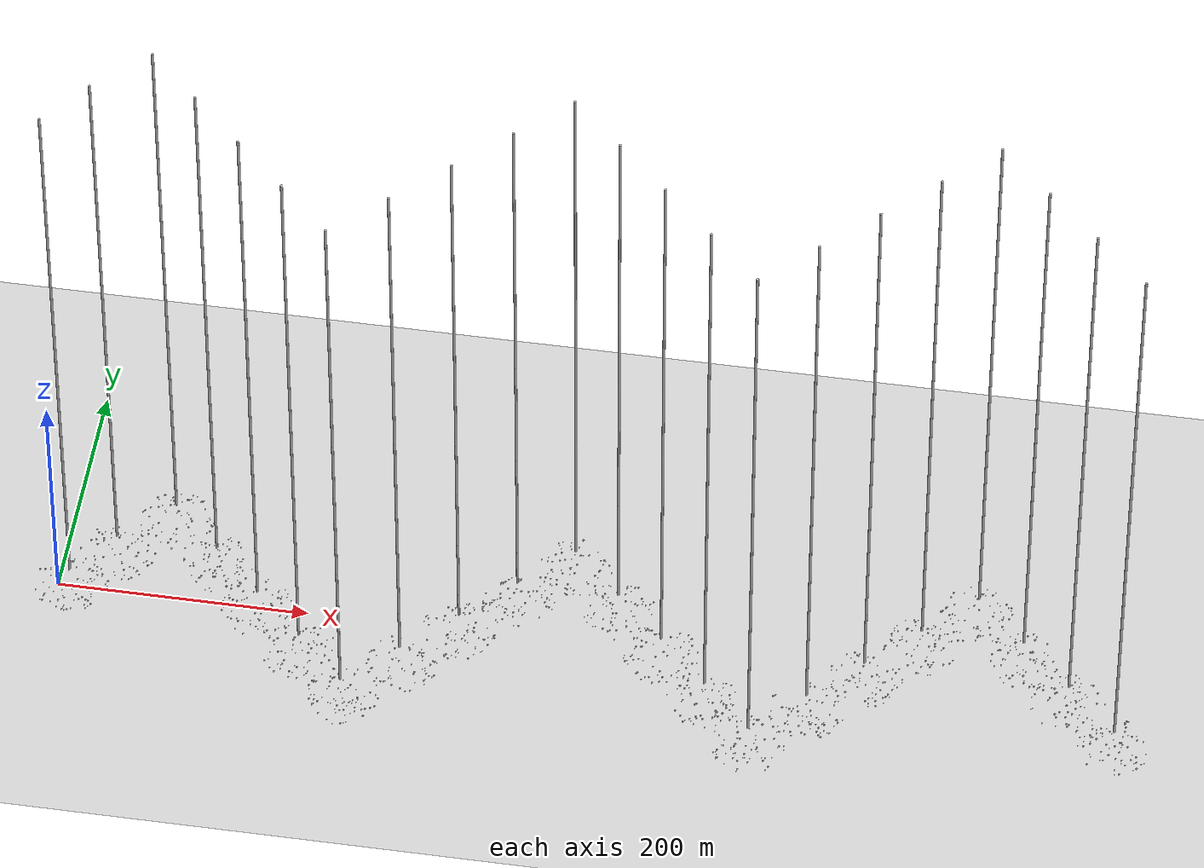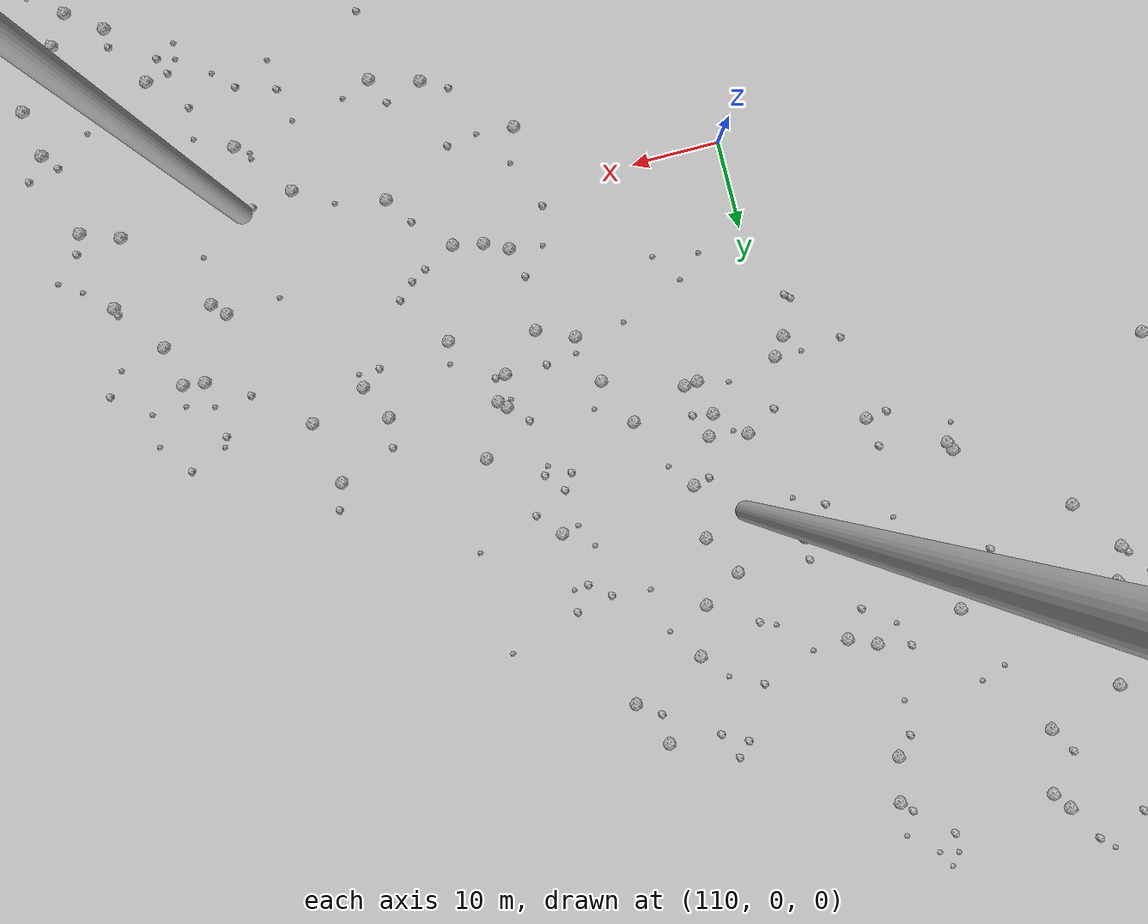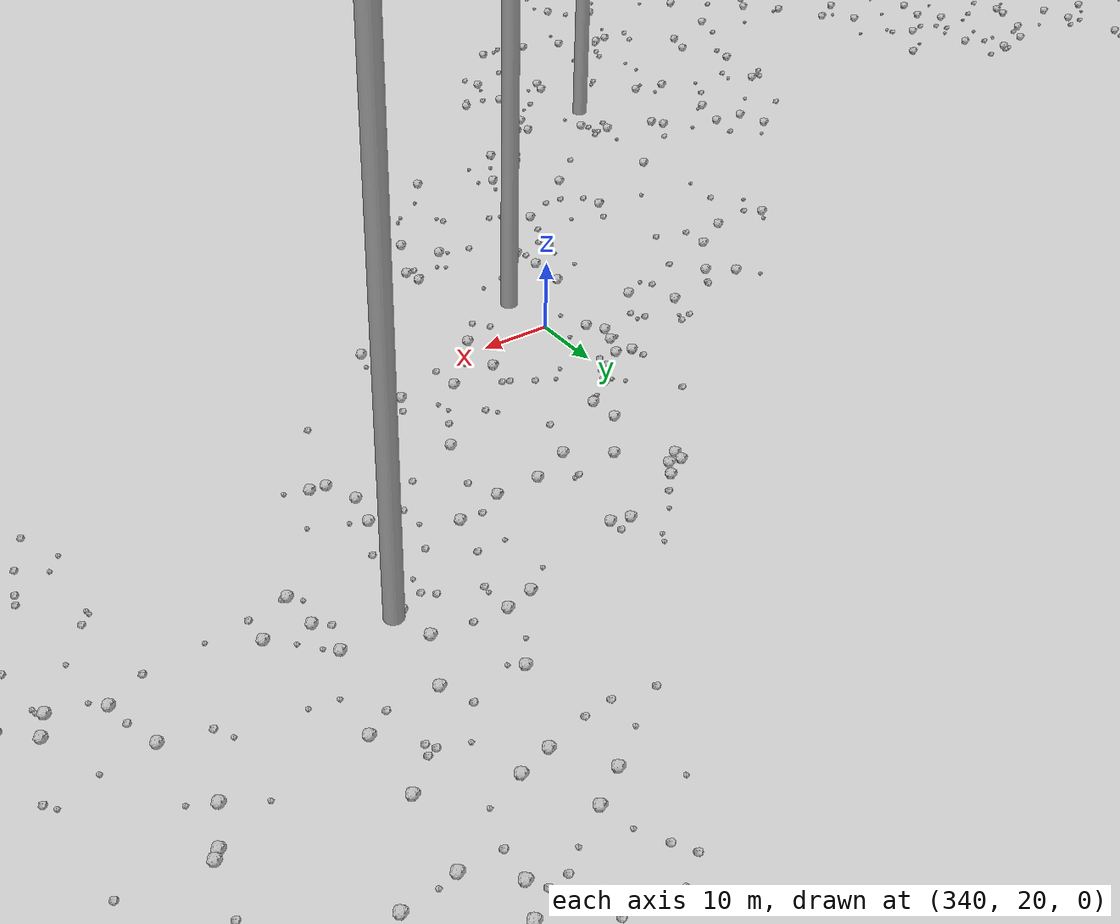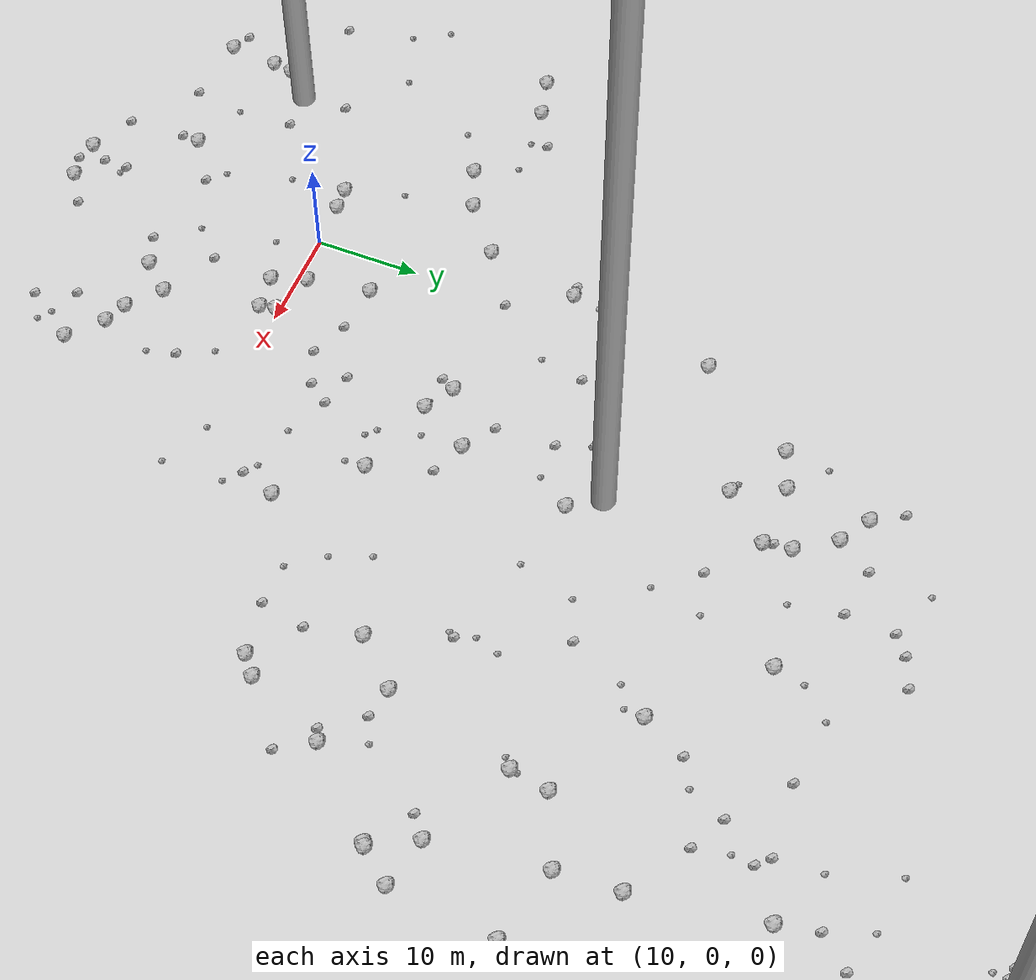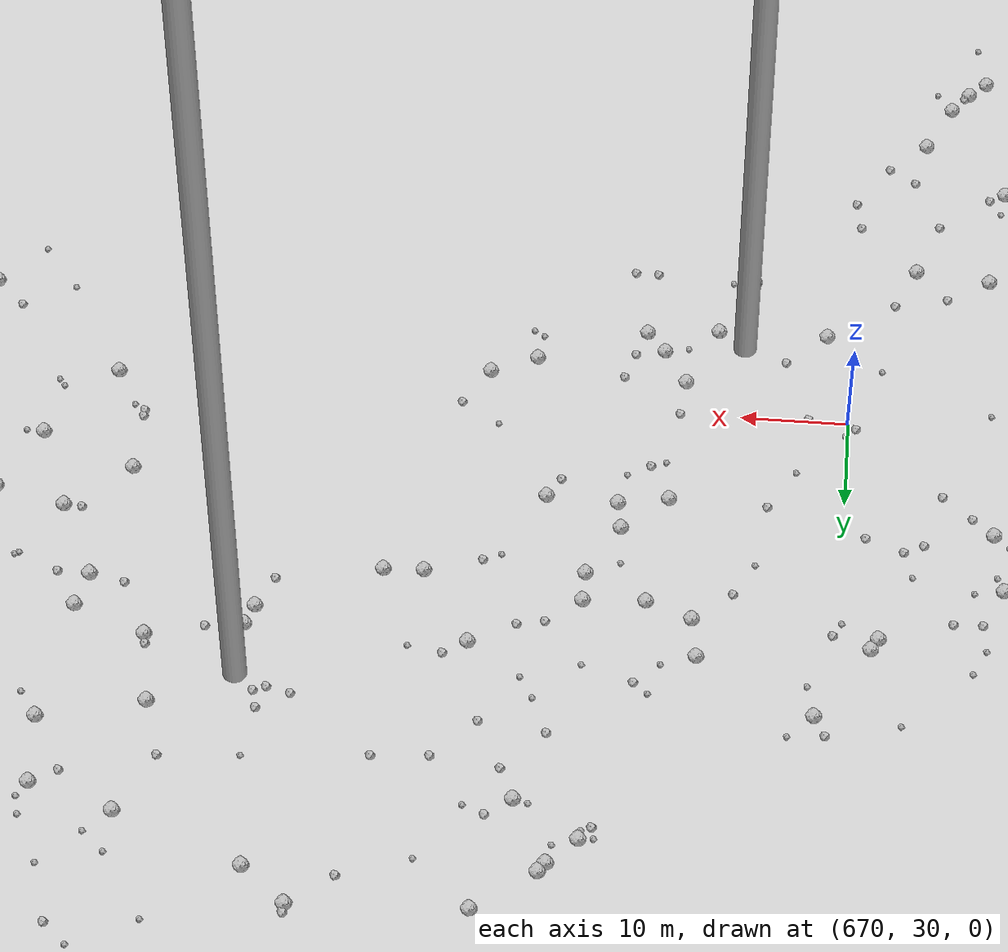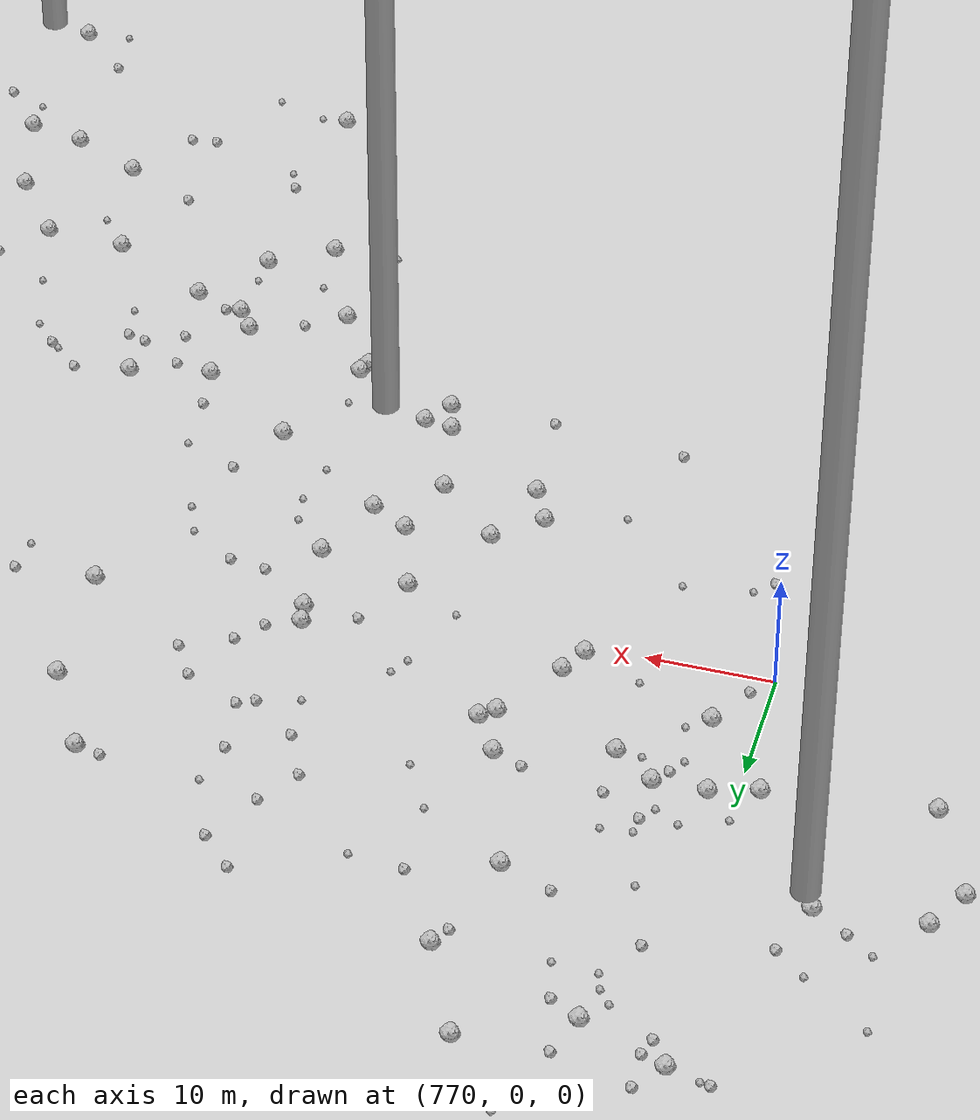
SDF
<sdf version="1.6">
 <world name="default">
  <include><uri>model://custom_ground</uri></include>
  <include><uri>model://sun</uri></include>
  <spherical_coordinates>
   <surface_model>EARTH_WGS84</surface_model>
   <latitude_deg>38.161479</latitude_deg>
   <longitude_deg>-122.454630</longitude_deg>
   <elevation>488.0</elevation>
   <heading_deg>90</heading_deg>
  </spherical_coordinates>
  <model name="rock1_0_0">
   <include><uri>model://rock1</uri><pose>0.5709609267824725 11.924836167784733 0.5 0 0 0</pose></include>
  </model>
  <model name="rock1_0_1">
   <include><uri>model://rock1</uri><pose>29.39491307878967 -17.087904305735957 0.5 0 0 0</pose></include>
  </model>
  <model name="rock1_0_2">
   <include><uri>model://rock1</uri><pose>14.933837265712569 0.9949295447033677 0.5 0 0 0</pose></include>
  </model>
  <model name="rock1_0_3">
   <include><uri>model://rock1</uri><pose>24.30930496548693 17.12489182076935 0.5 0 0 0</pose></include>
  </model>
  <model name="rock1_0_4">
   <include><uri>model://rock1</uri><pose>5.690506537570698 -0.17455987235686976 0.5 0 0 0</pose></include>
  </model>
  <model name="rock1_0_5">
   <include><uri>model://rock1</uri><pose>-9.130850718001023 -13.921788676913597 0.5 0 0 0</pose></include>
  </model>
  <model name="rock1_0_6">
   <include><uri>model://rock1</uri><pose>5.305035312677088 15.800962750302112 0.5 0 0 0</pose></include>
  </model>
  <model name="rock1_0_7">
   <include><uri>model://rock1</uri><pose>3.4669213313305356 -0.36841100369484536 0.5 0 0 0</pose></include>
  </model>
  <model name="rock1_0_8">
   <include><uri>model://rock1</uri><pose>-17.014447587070222 12.532294975776047 0.5 0 0 0</pose></include>
  </model>
  <model name="rock1_0_9">
   <include><uri>model://rock1</uri><pose>-8.849555464740998 -11.955227766880725 0.5 0 0 0</pose></include>
  </model>
  <model name="rock1_0_10">
   <include><uri>model://rock1</uri><pose>16.061428679080898 -2.2822578574318406 0.5 0 0 0</pose></include>
  </model>
  <model name="rock1_0_11">
   <include><uri>model://rock1</uri><pose>21.153007496939296 -11.021854077770577 0.5 0 0 0</pose></include>
  </model>
  <model name="rock1_0_12">
   <include><uri>model://rock1</uri><pose>7.4793040844678025 -25.692660465919744 0.5 0 0 0</pose></include>
  </model>
  <model name="rock1_0_13">
   <include><uri>model://rock1</uri><pose>24.137377785898167 -13.530726777062302 0.5 0 0 0</pose></include>
  </model>
  <model name="rock1_0_14">
   <include><uri>model://rock1</uri><pose>7.2460394517262685 24.987853640662706 0.5 0 0 0</pose></include>
  </model>
  <model name="rock1_0_15">
   <include><uri>model://rock1</uri><pose>11.475056743162991 -25.651605418547526 0.5 0 0 0</pose></include>
  </model>
  <model name="rock1_0_16">
   <include><uri>model://rock1</uri><pose>19.46746038672682 -1.828235305087965 0.5 0 0 0</pose></include>
  </model>
  <model name="rock1_0_17">
   <include><uri>model://rock1</uri><pose>3.079094262810248 -16.410808211682344 0.5 0 0 0</pose></include>
  </model>
  <model name="rock1_0_18">
   <include><uri>model://rock1</uri><pose>-3.4714569849187953 10.309843690889316 0.5 0 0 0</pose></include>
  </model>
  <model name="rock1_0_19">
   <include><uri>model://rock1</uri><pose>26.375126599245036 -14.390342148528322 0.5 0 0 0</pose></include>
  </model>
  <model name="rock1_0_20">
   <include><uri>model://rock1</uri><pose>18.705844454760296 -13.76979937157764 0.5 0 0 0</pose></include>
  </model>
  <model name="rock1_0_21">
   <include><uri>model://rock1</uri><pose>19.10455708358726 -0.3819151877034841 0.5 0 0 0</pose></include>
  </model>
  <model name="rock1_0_22">
   <include><uri>model://rock1</uri><pose>-13.062558602418166 13.546242114762784 0.5 0 0 0</pose></include>
  </model>
  <model name="rock1_0_23">
   <include><uri>model://rock1</uri><pose>38.12931599843895 8.354175264215861 0.5 0 0 0</pose></include>
  </model>
  <model name="rock1_0_24">
   <include><uri>model://rock1</uri><pose>-9.63604765552752 -18.716124753431764 0.5 0 0 0</pose></include>
  </model>
  <model name="rock1_0_25">
   <include><uri>model://rock1</uri><pose>32.30392688301454 14.7874263075623 0.5 0 0 0</pose></include>
  </model>
  <model name="rock1_0_26">
   <include><uri>model://rock1</uri><pose>13.915197304523986 6.9992979716585495 0.5 0 0 0</pose></include>
  </model>
  <model name="rock2_0_0">
   <include><uri>model://rock2</uri><pose>25.841019970501705 -22.10304186466138 0.3 0 0 0</pose></include>
  </model>
  <model name="rock2_0_1">
   <include><uri>model://rock2</uri><pose>8.638472492994222 -23.770864845822583 0.3 0 0 0</pose></include>
  </model>
  <model name="rock2_0_2">
   <include><uri>model://rock2</uri><pose>-2.9211205448222124 -19.25450530029349 0.3 0 0 0</pose></include>
  </model>
  <model name="rock2_0_3">
   <include><uri>model://rock2</uri><pose>22.23248173480453 5.075046047722488 0.3 0 0 0</pose></include>
  </model>
  <model name="rock2_0_4">
   <include><uri>model://rock2</uri><pose>18.589331766470515 6.509073909165949 0.3 0 0 0</pose></include>
  </model>
  <model name="rock2_0_5">
   <include><uri>model://rock2</uri><pose>36.85502291245253 4.955002674389753 0.3 0 0 0</pose></include>
  </model>
  <model name="rock2_0_6">
   <include><uri>model://rock2</uri><pose>-6.466458988255582 -4.77362626653326 0.3 0 0 0</pose></include>
  </model>
  <model name="rock2_0_7">
   <include><uri>model://rock2</uri><pose>27.14583984797072 8.50401554256301 0.3 0 0 0</pose></include>
  </model>
  <model name="rock2_0_8">
   <include><uri>model://rock2</uri><pose>24.352087364102438 -18.425971568425194 0.3 0 0 0</pose></include>
  </model>
  <model name="rock2_0_9">
   <include><uri>model://rock2</uri><pose>15.617348500426083 -14.882801950318425 0.3 0 0 0</pose></include>
  </model>
  <model name="rock2_0_10">
   <include><uri>model://rock2</uri><pose>-2.449412819848 -9.007034915720354 0.3 0 0 0</pose></include>
  </model>
  <model name="rock2_0_11">
   <include><uri>model://rock2</uri><pose>-9.315354573040546 15.747434206515095 0.3 0 0 0</pose></include>
  </model>
  <model name="rock2_0_12">
   <include><uri>model://rock2</uri><pose>3.1193927499961163 -23.729530830193546 0.3 0 0 0</pose></include>
  </model>
  <model name="rock2_0_13">
   <include><uri>model://rock2</uri><pose>14.382343701023622 -23.670240278554918 0.3 0 0 0</pose></include>
  </model>
  <model name="rock2_0_14">
   <include><uri>model://rock2</uri><pose>25.632867735354736 6.458670355337389 0.3 0 0 0</pose></include>
  </model>
  <model name="rock2_0_15">
   <include><uri>model://rock2</uri><pose>20.691694865873934 17.382331641589516 0.3 0 0 0</pose></include>
  </model>
  <model name="rock2_0_16">
   <include><uri>model://rock2</uri><pose>10.579671168137516 19.418638952899073 0.3 0 0 0</pose></include>
  </model>
  <model name="rock2_0_17">
   <include><uri>model://rock2</uri><pose>27.256655375496237 -6.597911526646364 0.3 0 0 0</pose></include>
  </model>
  <model name="rock2_0_18">
   <include><uri>model://rock2</uri><pose>2.8751638617344604 -18.142649905727954 0.3 0 0 0</pose></include>
  </model>
  <model name="rock2_0_19">
   <include><uri>model://rock2</uri><pose>7.227771927873494 -13.464098278016476 0.3 0 0 0</pose></include>
  </model>
  <model name="rock2_0_20">
   <include><uri>model://rock2</uri><pose>9.294422837239388 -26.254476745262313 0.3 0 0 0</pose></include>
  </model>
  <model name="rock2_0_21">
   <include><uri>model://rock2</uri><pose>23.82424203241247 9.206574021631866 0.3 0 0 0</pose></include>
  </model>
  <model name="rock2_0_22">
   <include><uri>model://rock2</uri><pose>6.054696293799694 24.89122554175016 0.3 0 0 0</pose></include>
  </model>
  <model name="rock2_0_23">
   <include><uri>model://rock2</uri><pose>15.717220958583958 -8.35302585784132 0.3 0 0 0</pose></include>
  </model>
  <model name="rock2_0_24">
   <include><uri>model://rock2</uri><pose>8.680582557287963 -21.394152263109476 0.3 0 0 0</pose></include>
  </model>
  <model name="rock2_0_25">
   <include><uri>model://rock2</uri><pose>-11.635042928615817 -17.922117068110136 0.3 0 0 0</pose></include>
  </model>
  <model name="rock2_0_26">
   <include><uri>model://rock2</uri><pose>-16.378122605718037 -8.89737674887964 0.3 0 0 0</pose></include>
  </model>
  <model name="rock3_0_0">
   <include><uri>model://rock3</uri><pose>11.622226677149339 -3.8457371758402736 0.2 0 0 0</pose></include>
  </model>
  <model name="rock3_0_1">
   <include><uri>model://rock3</uri><pose>28.09554273809036 14.09028258733241 0.2 0 0 0</pose></include>
  </model>
  <model name="rock3_0_2">
   <include><uri>model://rock3</uri><pose>-17.905547700766917 -2.4889046764390272 0.2 0 0 0</pose></include>
  </model>
  <model name="rock3_0_3">
   <include><uri>model://rock3</uri><pose>-2.1811312042561966 -14.383594957133035 0.2 0 0 0</pose></include>
  </model>
  <model name="rock3_0_4">
   <include><uri>model://rock3</uri><pose>12.795597405230616 -11.193241498166191 0.2 0 0 0</pose></include>
  </model>
  <model name="rock3_0_5">
   <include><uri>model://rock3</uri><pose>7.615377417498831 27.678130217965005 0.2 0 0 0</pose></include>
  </model>
  <model name="rock3_0_6">
   <include><uri>model://rock3</uri><pose>-9.122462548260506 14.049659557542228 0.2 0 0 0</pose></include>
  </model>
  <model name="rock3_0_7">
   <include><uri>model://rock3</uri><pose>-5.588522811025726 14.174954919040417 0.2 0 0 0</pose></include>
  </model>
  <model name="rock3_0_8">
   <include><uri>model://rock3</uri><pose>31.206595891827376 6.666687059003081 0.2 0 0 0</pose></include>
  </model>
  <model name="rock3_0_9">
   <include><uri>model://rock3</uri><pose>33.62727356889978 -0.3120218157683574 0.2 0 0 0</pose></include>
  </model>
  <model name="rock3_0_10">
   <include><uri>model://rock3</uri><pose>38.454338613675546 -2.388951410110451 0.2 0 0 0</pose></include>
  </model>
  <model name="rock3_0_11">
   <include><uri>model://rock3</uri><pose>27.150180289669308 17.996629222855006 0.2 0 0 0</pose></include>
  </model>
  <model name="rock3_0_12">
   <include><uri>model://rock3</uri><pose>38.34492771419183 3.5605734431065557 0.2 0 0 0</pose></include>
  </model>
  <model name="rock3_0_13">
   <include><uri>model://rock3</uri><pose>-19.94494991585817 0.8452656645784096 0.2 0 0 0</pose></include>
  </model>
  <model name="rock3_0_14">
   <include><uri>model://rock3</uri><pose>5.665409323790254 -12.003820005366187 0.2 0 0 0</pose></include>
  </model>
  <model name="rock3_0_15">
   <include><uri>model://rock3</uri><pose>27.95062601479139 -9.382971411357058 0.2 0 0 0</pose></include>
  </model>
  <model name="rock3_0_16">
   <include><uri>model://rock3</uri><pose>35.65651902275084 5.777594537905557 0.2 0 0 0</pose></include>
  </model>
  <model name="rock3_0_17">
   <include><uri>model://rock3</uri><pose>-7.909212521520368 7.786209066995774 0.2 0 0 0</pose></include>
  </model>
  <model name="rock3_0_18">
   <include><uri>model://rock3</uri><pose>-12.162519660179365 -0.42413160310499265 0.2 0 0 0</pose></include>
  </model>
  <model name="rock3_0_19">
   <include><uri>model://rock3</uri><pose>28.328979350312537 -20.567121363483796 0.2 0 0 0</pose></include>
  </model>
  <model name="rock3_0_20">
   <include><uri>model://rock3</uri><pose>3.912736370563522 -5.78254816244382 0.2 0 0 0</pose></include>
  </model>
  <model name="rock3_0_21">
   <include><uri>model://rock3</uri><pose>32.25920960198287 12.78961450838787 0.2 0 0 0</pose></include>
  </model>
  <model name="rock3_0_22">
   <include><uri>model://rock3</uri><pose>9.42725687633466 -21.741799439863584 0.2 0 0 0</pose></include>
  </model>
  <model name="rock3_0_23">
   <include><uri>model://rock3</uri><pose>27.148967883373444 -19.701669519939824 0.2 0 0 0</pose></include>
  </model>
  <model name="rock3_0_24">
   <include><uri>model://rock3</uri><pose>15.107056136671304 24.903821401573886 0.2 0 0 0</pose></include>
  </model>
  <model name="rock3_0_25">
   <include><uri>model://rock3</uri><pose>25.586356532597385 -3.454172864935231 0.2 0 0 0</pose></include>
  </model>
  <model name="rock3_0_26">
   <include><uri>model://rock3</uri><pose>1.6796996667943453 5.210174338389827 0.2 0 0 0</pose></include>
  </model>
  <model name="rock1_1_0">
   <include><uri>model://rock1</uri><pose>62.06753027571384 50.715071868015514 0.5 0 0 0</pose></include>
  </model>
  <model name="rock1_1_1">
   <include><uri>model://rock1</uri><pose>22.558699603950775 45.85713172822968 0.5 0 0 0</pose></include>
  </model>
  <model name="rock1_1_2">
   <include><uri>model://rock1</uri><pose>27.064942420161714 21.98040908801179 0.5 0 0 0</pose></include>
  </model>
  <model name="rock1_1_3">
   <include><uri>model://rock1</uri><pose>20.410012540865672 50.45890889481863 0.5 0 0 0</pose></include>
  </model>
  <model name="rock1_1_4">
   <include><uri>model://rock1</uri><pose>63.91144579553246 34.09039208057851 0.5 0 0 0</pose></include>
  </model>
  <model name="rock1_1_5">
   <include><uri>model://rock1</uri><pose>65.94071164258027 29.76444362433133 0.5 0 0 0</pose></include>
  </model>
  <model name="rock1_1_6">
   <include><uri>model://rock1</uri><pose>53.678744154148944 13.323191435109784 0.5 0 0 0</pose></include>
  </model>
  <model name="rock1_1_7">
   <include><uri>model://rock1</uri><pose>21.485159893693886 18.760157521480135 0.5 0 0 0</pose></include>
  </model>
  <model name="rock1_1_8">
   <include><uri>model://rock1</uri><pose>66.20009827109138 29.979567290731953 0.5 0 0 0</pose></include>
  </model>
  <model name="rock1_1_9">
   <include><uri>model://rock1</uri><pose>23.82269602723932 56.490302133279634 0.5 0 0 0</pose></include>
  </model>
  <model name="rock1_1_10">
   <include><uri>model://rock1</uri><pose>26.284898509071258 52.93200241870225 0.5 0 0 0</pose></include>
  </model>
  <model name="rock1_1_11">
   <include><uri>model://rock1</uri><pose>46.668454080079705 46.78821691932327 0.5 0 0 0</pose></include>
  </model>
  <model name="rock1_1_12">
   <include><uri>model://rock1</uri><pose>52.28529455589566 25.97200300260341 0.5 0 0 0</pose></include>
  </model>
  <model name="rock1_1_13">
   <include><uri>model://rock1</uri><pose>55.35421704172631 38.22077220009888 0.5 0 0 0</pose></include>
  </model>
  <model name="rock1_1_14">
   <include><uri>model://rock1</uri><pose>55.46661566961592 14.802996463637875 0.5 0 0 0</pose></include>
  </model>
  <model name="rock1_1_15">
   <include><uri>model://rock1</uri><pose>62.42942242642676 44.77937304957186 0.5 0 0 0</pose></include>
  </model>
  <model name="rock1_1_16">
   <include><uri>model://rock1</uri><pose>38.06937716689363 55.238932163077166 0.5 0 0 0</pose></include>
  </model>
  <model name="rock1_1_17">
   <include><uri>model://rock1</uri><pose>26.64366963932889 50.307729256985255 0.5 0 0 0</pose></include>
  </model>
  <model name="rock1_1_18">
   <include><uri>model://rock1</uri><pose>56.00810631959888 41.912210556710406 0.5 0 0 0</pose></include>
  </model>
  <model name="rock1_1_19">
   <include><uri>model://rock1</uri><pose>20.8842404799067 58.28065853652529 0.5 0 0 0</pose></include>
  </model>
  <model name="rock1_1_20">
   <include><uri>model://rock1</uri><pose>59.03681111586593 22.50486806013323 0.5 0 0 0</pose></include>
  </model>
  <model name="rock1_1_21">
   <include><uri>model://rock1</uri><pose>69.60377850454759 42.99512997852693 0.5 0 0 0</pose></include>
  </model>
  <model name="rock1_1_22">
   <include><uri>model://rock1</uri><pose>16.63123446495825 49.105750007474406 0.5 0 0 0</pose></include>
  </model>
  <model name="rock1_1_23">
   <include><uri>model://rock1</uri><pose>48.29084095056386 21.834778016575754 0.5 0 0 0</pose></include>
  </model>
  <model name="rock1_1_24">
   <include><uri>model://rock1</uri><pose>68.64950759279934 32.99701363858982 0.5 0 0 0</pose></include>
  </model>
  <model name="rock1_1_25">
   <include><uri>model://rock1</uri><pose>10.287735630481231 39.47123325659037 0.5 0 0 0</pose></include>
  </model>
  <model name="rock1_1_26">
   <include><uri>model://rock1</uri><pose>29.553609814197376 32.943284376810624 0.5 0 0 0</pose></include>
  </model>
  <model name="rock2_1_0">
   <include><uri>model://rock2</uri><pose>48.4994867714575 12.422562452067641 0.3 0 0 0</pose></include>
  </model>
  <model name="rock2_1_1">
   <include><uri>model://rock2</uri><pose>61.92664228016215 32.57682762088218 0.3 0 0 0</pose></include>
  </model>
  <model name="rock2_1_2">
   <include><uri>model://rock2</uri><pose>55.8321471842172 59.677841722404665 0.3 0 0 0</pose></include>
  </model>
  <model name="rock2_1_3">
   <include><uri>model://rock2</uri><pose>31.339445007920688 46.62356818995172 0.3 0 0 0</pose></include>
  </model>
  <model name="rock2_1_4">
   <include><uri>model://rock2</uri><pose>19.06303558238514 61.15093160189331 0.3 0 0 0</pose></include>
  </model>
  <model name="rock2_1_5">
   <include><uri>model://rock2</uri><pose>54.71715599574786 60.78513876511168 0.3 0 0 0</pose></include>
  </model>
  <model name="rock2_1_6">
   <include><uri>model://rock2</uri><pose>22.47798614647749 32.995734800564065 0.3 0 0 0</pose></include>
  </model>
  <model name="rock2_1_7">
   <include><uri>model://rock2</uri><pose>55.14382550681575 25.449519374837273 0.3 0 0 0</pose></include>
  </model>
  <model name="rock2_1_8">
   <include><uri>model://rock2</uri><pose>35.694871103989286 66.44080160754348 0.3 0 0 0</pose></include>
  </model>
  <model name="rock2_1_9">
   <include><uri>model://rock2</uri><pose>15.995028396334476 29.248511015071063 0.3 0 0 0</pose></include>
  </model>
  <model name="rock2_1_10">
   <include><uri>model://rock2</uri><pose>23.708469697498717 29.67873664925803 0.3 0 0 0</pose></include>
  </model>
  <model name="rock2_1_11">
   <include><uri>model://rock2</uri><pose>52.91097819199993 56.10023559996498 0.3 0 0 0</pose></include>
  </model>
  <model name="rock2_1_12">
   <include><uri>model://rock2</uri><pose>56.31333015950028 54.436123653627924 0.3 0 0 0</pose></include>
  </model>
  <model name="rock2_1_13">
   <include><uri>model://rock2</uri><pose>47.72707882115802 60.2729096861498 0.3 0 0 0</pose></include>
  </model>
  <model name="rock2_1_14">
   <include><uri>model://rock2</uri><pose>45.47151733783997 29.05846224219426 0.3 0 0 0</pose></include>
  </model>
  <model name="rock2_1_15">
   <include><uri>model://rock2</uri><pose>25.907436242561754 59.85700755654352 0.3 0 0 0</pose></include>
  </model>
  <model name="rock2_1_16">
   <include><uri>model://rock2</uri><pose>48.81073592685263 51.07629195709913 0.3 0 0 0</pose></include>
  </model>
  <model name="rock2_1_17">
   <include><uri>model://rock2</uri><pose>57.78339227485807 21.946477003488045 0.3 0 0 0</pose></include>
  </model>
  <model name="rock2_1_18">
   <include><uri>model://rock2</uri><pose>49.382707544500356 16.72892694928371 0.3 0 0 0</pose></include>
  </model>
  <model name="rock2_1_19">
   <include><uri>model://rock2</uri><pose>30.970261247380325 63.88216000718334 0.3 0 0 0</pose></include>
  </model>
  <model name="rock2_1_20">
   <include><uri>model://rock2</uri><pose>30.33897012921729 20.653088192027198 0.3 0 0 0</pose></include>
  </model>
  <model name="rock2_1_21">
   <include><uri>model://rock2</uri><pose>32.79256925050286 65.29142508327222 0.3 0 0 0</pose></include>
  </model>
  <model name="rock2_1_22">
   <include><uri>model://rock2</uri><pose>60.974921943100014 19.34002557910005 0.3 0 0 0</pose></include>
  </model>
  <model name="rock2_1_23">
   <include><uri>model://rock2</uri><pose>23.992350073683973 23.99132445221023 0.3 0 0 0</pose></include>
  </model>
  <model name="rock2_1_24">
   <include><uri>model://rock2</uri><pose>30.74433475118409 59.182798012136026 0.3 0 0 0</pose></include>
  </model>
  <model name="rock2_1_25">
   <include><uri>model://rock2</uri><pose>26.277161716210667 51.252068868207964 0.3 0 0 0</pose></include>
  </model>
  <model name="rock2_1_26">
   <include><uri>model://rock2</uri><pose>42.020684958140144 38.643098921401844 0.3 0 0 0</pose></include>
  </model>
  <model name="rock3_1_0">
   <include><uri>model://rock3</uri><pose>55.62699144659304 57.61403247201954 0.2 0 0 0</pose></include>
  </model>
  <model name="rock3_1_1">
   <include><uri>model://rock3</uri><pose>54.32286398847397 37.425567461461824 0.2 0 0 0</pose></include>
  </model>
  <model name="rock3_1_2">
   <include><uri>model://rock3</uri><pose>38.070105391843484 36.96889327902299 0.2 0 0 0</pose></include>
  </model>
  <model name="rock3_1_3">
   <include><uri>model://rock3</uri><pose>28.965323016109277 13.26772142821087 0.2 0 0 0</pose></include>
  </model>
  <model name="rock3_1_4">
   <include><uri>model://rock3</uri><pose>44.34025450230826 43.83256203655839 0.2 0 0 0</pose></include>
  </model>
  <model name="rock3_1_5">
   <include><uri>model://rock3</uri><pose>44.41667454976618 12.48379292791925 0.2 0 0 0</pose></include>
  </model>
  <model name="rock3_1_6">
   <include><uri>model://rock3</uri><pose>35.45543928044188 47.735876181424416 0.2 0 0 0</pose></include>
  </model>
  <model name="rock3_1_7">
   <include><uri>model://rock3</uri><pose>54.38151521710607 65.11517222396319 0.2 0 0 0</pose></include>
  </model>
  <model name="rock3_1_8">
   <include><uri>model://rock3</uri><pose>26.258687037864 65.64124388533973 0.2 0 0 0</pose></include>
  </model>
  <model name="rock3_1_9">
   <include><uri>model://rock3</uri><pose>57.48182757500463 26.506372711545353 0.2 0 0 0</pose></include>
  </model>
  <model name="rock3_1_10">
   <include><uri>model://rock3</uri><pose>16.984848229635496 53.33769099806426 0.2 0 0 0</pose></include>
  </model>
  <model name="rock3_1_11">
   <include><uri>model://rock3</uri><pose>55.34342064026202 38.877811800816595 0.2 0 0 0</pose></include>
  </model>
  <model name="rock3_1_12">
   <include><uri>model://rock3</uri><pose>46.44880224811974 44.89066273893841 0.2 0 0 0</pose></include>
  </model>
  <model name="rock3_1_13">
   <include><uri>model://rock3</uri><pose>45.48482413534193 33.070571729014546 0.2 0 0 0</pose></include>
  </model>
  <model name="rock3_1_14">
   <include><uri>model://rock3</uri><pose>21.41799128643859 46.300839494807065 0.2 0 0 0</pose></include>
  </model>
  <model name="rock3_1_15">
   <include><uri>model://rock3</uri><pose>51.38469847753436 52.51893502891439 0.2 0 0 0</pose></include>
  </model>
  <model name="rock3_1_16">
   <include><uri>model://rock3</uri><pose>45.05424853761048 28.454992404747937 0.2 0 0 0</pose></include>
  </model>
  <model name="rock3_1_17">
   <include><uri>model://rock3</uri><pose>38.58043213908634 58.172563402002844 0.2 0 0 0</pose></include>
  </model>
  <model name="rock3_1_18">
   <include><uri>model://rock3</uri><pose>42.056063545156086 15.64642550231023 0.2 0 0 0</pose></include>
  </model>
  <model name="rock3_1_19">
   <include><uri>model://rock3</uri><pose>31.611060683540384 54.28542341478864 0.2 0 0 0</pose></include>
  </model>
  <model name="rock3_1_20">
   <include><uri>model://rock3</uri><pose>34.4037241281101 42.80419193403267 0.2 0 0 0</pose></include>
  </model>
  <model name="rock3_1_21">
   <include><uri>model://rock3</uri><pose>40.58382568130382 19.292123135107406 0.2 0 0 0</pose></include>
  </model>
  <model name="rock3_1_22">
   <include><uri>model://rock3</uri><pose>23.415342737556518 17.204490973168625 0.2 0 0 0</pose></include>
  </model>
  <model name="rock3_1_23">
   <include><uri>model://rock3</uri><pose>44.7261344749582 30.789292656745072 0.2 0 0 0</pose></include>
  </model>
  <model name="rock3_1_24">
   <include><uri>model://rock3</uri><pose>41.262491246820524 60.951418207071875 0.2 0 0 0</pose></include>
  </model>
  <model name="rock3_1_25">
   <include><uri>model://rock3</uri><pose>36.46847279119834 31.502914429233723 0.2 0 0 0</pose></include>
  </model>
  <model name="rock3_1_26">
   <include><uri>model://rock3</uri><pose>27.314175693650952 29.693034763174527 0.2 0 0 0</pose></include>
  </model>
  <model name="rock1_2_0">
   <include><uri>model://rock1</uri><pose>78.43675079510594 59.854207470134675 0.5 0 0 0</pose></include>
  </model>
  <model name="rock1_2_1">
   <include><uri>model://rock1</uri><pose>66.02511352513146 75.10257009294037 0.5 0 0 0</pose></include>
  </model>
  <model name="rock1_2_2">
   <include><uri>model://rock1</uri><pose>79.07249539585261 90.09674664831707 0.5 0 0 0</pose></include>
  </model>
  <model name="rock1_2_3">
   <include><uri>model://rock1</uri><pose>83.45475515390385 58.22449299536701 0.5 0 0 0</pose></include>
  </model>
  <model name="rock1_2_4">
   <include><uri>model://rock1</uri><pose>84.84829235114353 102.89745710126932 0.5 0 0 0</pose></include>
  </model>
  <model name="rock1_2_5">
   <include><uri>model://rock1</uri><pose>91.56903032757654 81.49421378999645 0.5 0 0 0</pose></include>
  </model>
  <model name="rock1_2_6">
   <include><uri>model://rock1</uri><pose>96.52413282094074 58.44033991818705 0.5 0 0 0</pose></include>
  </model>
  <model name="rock1_2_7">
   <include><uri>model://rock1</uri><pose>60.155909508429296 62.6973186556492 0.5 0 0 0</pose></include>
  </model>
  <model name="rock1_2_8">
   <include><uri>model://rock1</uri><pose>56.568613840027254 90.89915881895494 0.5 0 0 0</pose></include>
  </model>
  <model name="rock1_2_9">
   <include><uri>model://rock1</uri><pose>62.33226760246087 91.91329861988709 0.5 0 0 0</pose></include>
  </model>
  <model name="rock1_2_10">
   <include><uri>model://rock1</uri><pose>95.32250893040245 102.70121181416823 0.5 0 0 0</pose></include>
  </model>
  <model name="rock1_2_11">
   <include><uri>model://rock1</uri><pose>73.46668606909192 100.37841477967834 0.5 0 0 0</pose></include>
  </model>
  <model name="rock1_2_12">
   <include><uri>model://rock1</uri><pose>83.73684064898345 103.22876419113234 0.5 0 0 0</pose></include>
  </model>
  <model name="rock1_2_13">
   <include><uri>model://rock1</uri><pose>89.94018848097542 74.28076333590882 0.5 0 0 0</pose></include>
  </model>
  <model name="rock1_2_14">
   <include><uri>model://rock1</uri><pose>51.300065612867016 85.27456268843312 0.5 0 0 0</pose></include>
  </model>
  <model name="rock1_2_15">
   <include><uri>model://rock1</uri><pose>65.10561270809242 105.4495280046383 0.5 0 0 0</pose></include>
  </model>
  <model name="rock1_2_16">
   <include><uri>model://rock1</uri><pose>81.26767638388603 50.07678847608892 0.5 0 0 0</pose></include>
  </model>
  <model name="rock1_2_17">
   <include><uri>model://rock1</uri><pose>66.43902011172355 61.91701136982117 0.5 0 0 0</pose></include>
  </model>
  <model name="rock1_2_18">
   <include><uri>model://rock1</uri><pose>52.77555689658791 86.79352127500371 0.5 0 0 0</pose></include>
  </model>
  <model name="rock1_2_19">
   <include><uri>model://rock1</uri><pose>90.07261144606215 83.5164400651818 0.5 0 0 0</pose></include>
  </model>
  <model name="rock1_2_20">
   <include><uri>model://rock1</uri><pose>81.14568657208225 71.33977004628541 0.5 0 0 0</pose></include>
  </model>
  <model name="rock1_2_21">
   <include><uri>model://rock1</uri><pose>96.57328665154613 103.475514201337 0.5 0 0 0</pose></include>
  </model>
  <model name="rock1_2_22">
   <include><uri>model://rock1</uri><pose>60.157812096761866 102.00086030944746 0.5 0 0 0</pose></include>
  </model>
  <model name="rock1_2_23">
   <include><uri>model://rock1</uri><pose>107.60230387909985 72.96526498771026 0.5 0 0 0</pose></include>
  </model>
  <model name="rock1_2_24">
   <include><uri>model://rock1</uri><pose>71.48924202516227 95.65574658936185 0.5 0 0 0</pose></include>
  </model>
  <model name="rock1_2_25">
   <include><uri>model://rock1</uri><pose>77.03208341832524 56.048053382641 0.5 0 0 0</pose></include>
  </model>
  <model name="rock1_2_26">
   <include><uri>model://rock1</uri><pose>108.72322108978594 78.07719435570738 0.5 0 0 0</pose></include>
  </model>
  <model name="rock2_2_0">
   <include><uri>model://rock2</uri><pose>91.44780937281278 52.70974443639819 0.3 0 0 0</pose></include>
  </model>
  <model name="rock2_2_1">
   <include><uri>model://rock2</uri><pose>61.75193672639747 69.33162598637459 0.3 0 0 0</pose></include>
  </model>
  <model name="rock2_2_2">
   <include><uri>model://rock2</uri><pose>90.70167179968172 107.8099702587865 0.3 0 0 0</pose></include>
  </model>
  <model name="rock2_2_3">
   <include><uri>model://rock2</uri><pose>87.10602737731685 108.60181138695688 0.3 0 0 0</pose></include>
  </model>
  <model name="rock2_2_4">
   <include><uri>model://rock2</uri><pose>61.74571367568691 72.8935886565688 0.3 0 0 0</pose></include>
  </model>
  <model name="rock2_2_5">
   <include><uri>model://rock2</uri><pose>81.96769599598616 65.68512774535517 0.3 0 0 0</pose></include>
  </model>
  <model name="rock2_2_6">
   <include><uri>model://rock2</uri><pose>71.11570083715024 55.59793421953678 0.3 0 0 0</pose></include>
  </model>
  <model name="rock2_2_7">
   <include><uri>model://rock2</uri><pose>59.258751133559215 66.47505672632893 0.3 0 0 0</pose></include>
  </model>
  <model name="rock2_2_8">
   <include><uri>model://rock2</uri><pose>88.73608517882617 101.02149397684144 0.3 0 0 0</pose></include>
  </model>
  <model name="rock2_2_9">
   <include><uri>model://rock2</uri><pose>74.39096161243114 97.03062255590086 0.3 0 0 0</pose></include>
  </model>
  <model name="rock2_2_10">
   <include><uri>model://rock2</uri><pose>87.59296256968278 87.81940978700356 0.3 0 0 0</pose></include>
  </model>
  <model name="rock2_2_11">
   <include><uri>model://rock2</uri><pose>71.89388902168564 104.17909803461981 0.3 0 0 0</pose></include>
  </model>
  <model name="rock2_2_12">
   <include><uri>model://rock2</uri><pose>76.30777610854642 96.21467035402077 0.3 0 0 0</pose></include>
  </model>
  <model name="rock2_2_13">
   <include><uri>model://rock2</uri><pose>69.00517930219213 87.71204058298812 0.3 0 0 0</pose></include>
  </model>
  <model name="rock2_2_14">
   <include><uri>model://rock2</uri><pose>102.89133278155391 61.10834462498623 0.3 0 0 0</pose></include>
  </model>
  <model name="rock2_2_15">
   <include><uri>model://rock2</uri><pose>96.13286438659594 104.11273742109573 0.3 0 0 0</pose></include>
  </model>
  <model name="rock2_2_16">
   <include><uri>model://rock2</uri><pose>57.4970151615244 81.21584769942528 0.3 0 0 0</pose></include>
  </model>
  <model name="rock2_2_17">
   <include><uri>model://rock2</uri><pose>77.51173204950757 108.3387840129062 0.3 0 0 0</pose></include>
  </model>
  <model name="rock2_2_18">
   <include><uri>model://rock2</uri><pose>105.63027742551654 71.00691252597274 0.3 0 0 0</pose></include>
  </model>
  <model name="rock2_2_19">
   <include><uri>model://rock2</uri><pose>76.29660749844652 56.94947747615847 0.3 0 0 0</pose></include>
  </model>
  <model name="rock2_2_20">
   <include><uri>model://rock2</uri><pose>99.21426611511163 95.6550472177438 0.3 0 0 0</pose></include>
  </model>
  <model name="rock2_2_21">
   <include><uri>model://rock2</uri><pose>107.48970804482767 79.483486913071 0.3 0 0 0</pose></include>
  </model>
  <model name="rock2_2_22">
   <include><uri>model://rock2</uri><pose>86.49851644333785 104.62686047466929 0.3 0 0 0</pose></include>
  </model>
  <model name="rock2_2_23">
   <include><uri>model://rock2</uri><pose>103.43961362049106 83.16249318153854 0.3 0 0 0</pose></include>
  </model>
  <model name="rock2_2_24">
   <include><uri>model://rock2</uri><pose>88.01343676300382 77.44910150928537 0.3 0 0 0</pose></include>
  </model>
  <model name="rock2_2_25">
   <include><uri>model://rock2</uri><pose>81.92714756754619 86.03220718493162 0.3 0 0 0</pose></include>
  </model>
  <model name="rock2_2_26">
   <include><uri>model://rock2</uri><pose>56.40844485054202 81.45029611039163 0.3 0 0 0</pose></include>
  </model>
  <model name="rock3_2_0">
   <include><uri>model://rock3</uri><pose>78.1943682808687 88.53894567768765 0.2 0 0 0</pose></include>
  </model>
  <model name="rock3_2_1">
   <include><uri>model://rock3</uri><pose>108.81785991157807 82.09130049181569 0.2 0 0 0</pose></include>
  </model>
  <model name="rock3_2_2">
   <include><uri>model://rock3</uri><pose>69.79904843464634 66.5129922988157 0.2 0 0 0</pose></include>
  </model>
  <model name="rock3_2_3">
   <include><uri>model://rock3</uri><pose>65.22132188372451 94.5430568122006 0.2 0 0 0</pose></include>
  </model>
  <model name="rock3_2_4">
   <include><uri>model://rock3</uri><pose>104.61999789740344 86.72690600446288 0.2 0 0 0</pose></include>
  </model>
  <model name="rock3_2_5">
   <include><uri>model://rock3</uri><pose>96.02565817475016 67.04152960314397 0.2 0 0 0</pose></include>
  </model>
  <model name="rock3_2_6">
   <include><uri>model://rock3</uri><pose>103.53729607547338 85.33838688113488 0.2 0 0 0</pose></include>
  </model>
  <model name="rock3_2_7">
   <include><uri>model://rock3</uri><pose>79.70606348090321 100.19125161264708 0.2 0 0 0</pose></include>
  </model>
  <model name="rock3_2_8">
   <include><uri>model://rock3</uri><pose>57.392799021507216 79.85961937042848 0.2 0 0 0</pose></include>
  </model>
  <model name="rock3_2_9">
   <include><uri>model://rock3</uri><pose>82.98707828444333 63.71762631850503 0.2 0 0 0</pose></include>
  </model>
  <model name="rock3_2_10">
   <include><uri>model://rock3</uri><pose>72.16080998049125 105.1081316513546 0.2 0 0 0</pose></include>
  </model>
  <model name="rock3_2_11">
   <include><uri>model://rock3</uri><pose>67.23243094988254 74.02795414399635 0.2 0 0 0</pose></include>
  </model>
  <model name="rock3_2_12">
   <include><uri>model://rock3</uri><pose>63.234272170197876 77.94316225941617 0.2 0 0 0</pose></include>
  </model>
  <model name="rock3_2_13">
   <include><uri>model://rock3</uri><pose>79.70236752887891 66.20606570783025 0.2 0 0 0</pose></include>
  </model>
  <model name="rock3_2_14">
   <include><uri>model://rock3</uri><pose>83.50871361320233 58.922627748751765 0.2 0 0 0</pose></include>
  </model>
  <model name="rock3_2_15">
   <include><uri>model://rock3</uri><pose>74.31392921200757 59.58868248807253 0.2 0 0 0</pose></include>
  </model>
  <model name="rock3_2_16">
   <include><uri>model://rock3</uri><pose>61.30635171442982 100.5898269841357 0.2 0 0 0</pose></include>
  </model>
  <model name="rock3_2_17">
   <include><uri>model://rock3</uri><pose>93.12776319943171 65.96852977316254 0.2 0 0 0</pose></include>
  </model>
  <model name="rock3_2_18">
   <include><uri>model://rock3</uri><pose>68.1253488811974 89.17147171486243 0.2 0 0 0</pose></include>
  </model>
  <model name="rock3_2_19">
   <include><uri>model://rock3</uri><pose>105.65542534281226 84.8277332212063 0.2 0 0 0</pose></include>
  </model>
  <model name="rock3_2_20">
   <include><uri>model://rock3</uri><pose>57.70416616851044 70.51582454718721 0.2 0 0 0</pose></include>
  </model>
  <model name="rock3_2_21">
   <include><uri>model://rock3</uri><pose>73.95253042658427 107.66024485572365 0.2 0 0 0</pose></include>
  </model>
  <model name="rock3_2_22">
   <include><uri>model://rock3</uri><pose>86.06661092091747 89.26691243998052 0.2 0 0 0</pose></include>
  </model>
  <model name="rock3_2_23">
   <include><uri>model://rock3</uri><pose>70.64484911896744 100.81266825163144 0.2 0 0 0</pose></include>
  </model>
  <model name="rock3_2_24">
   <include><uri>model://rock3</uri><pose>52.25637876358771 71.21015259957444 0.2 0 0 0</pose></include>
  </model>
  <model name="rock3_2_25">
   <include><uri>model://rock3</uri><pose>85.2837181758311 103.28183269632294 0.2 0 0 0</pose></include>
  </model>
  <model name="rock3_2_26">
   <include><uri>model://rock3</uri><pose>105.22864753243145 67.00664045994077 0.2 0 0 0</pose></include>
  </model>
  <model name="rock1_3_0">
   <include><uri>model://rock1</uri><pose>129.69409235367274 23.070062845843868 0.5 0 0 0</pose></include>
  </model>
  <model name="rock1_3_1">
   <include><uri>model://rock1</uri><pose>93.28228677794 39.64186178535991 0.5 0 0 0</pose></include>
  </model>
  <model name="rock1_3_2">
   <include><uri>model://rock1</uri><pose>126.56566018448542 56.296628131947216 0.5 0 0 0</pose></include>
  </model>
  <model name="rock1_3_3">
   <include><uri>model://rock1</uri><pose>138.32258513888272 38.810899968947666 0.5 0 0 0</pose></include>
  </model>
  <model name="rock1_3_4">
   <include><uri>model://rock1</uri><pose>119.12219578253234 25.81384747386592 0.5 0 0 0</pose></include>
  </model>
  <model name="rock1_3_5">
   <include><uri>model://rock1</uri><pose>131.29370062299114 17.437236673936134 0.5 0 0 0</pose></include>
  </model>
  <model name="rock1_3_6">
   <include><uri>model://rock1</uri><pose>106.71030662151755 59.93755645353948 0.5 0 0 0</pose></include>
  </model>
  <model name="rock1_3_7">
   <include><uri>model://rock1</uri><pose>124.49969254779194 50.78829907717976 0.5 0 0 0</pose></include>
  </model>
  <model name="rock1_3_8">
   <include><uri>model://rock1</uri><pose>92.8598522432411 40.608067722303616 0.5 0 0 0</pose></include>
  </model>
  <model name="rock1_3_9">
   <include><uri>model://rock1</uri><pose>140.8377821458967 23.272878066508518 0.5 0 0 0</pose></include>
  </model>
  <model name="rock1_3_10">
   <include><uri>model://rock1</uri><pose>101.55922921860561 34.703493793194404 0.5 0 0 0</pose></include>
  </model>
  <model name="rock1_3_11">
   <include><uri>model://rock1</uri><pose>120.66896948135962 25.947026041767405 0.5 0 0 0</pose></include>
  </model>
  <model name="rock1_3_12">
   <include><uri>model://rock1</uri><pose>141.68494943034284 22.38377984672717 0.5 0 0 0</pose></include>
  </model>
  <model name="rock1_3_13">
   <include><uri>model://rock1</uri><pose>108.35356789794739 23.237933000802066 0.5 0 0 0</pose></include>
  </model>
  <model name="rock1_3_14">
   <include><uri>model://rock1</uri><pose>120.06007897314447 48.08525429059736 0.5 0 0 0</pose></include>
  </model>
  <model name="rock1_3_15">
   <include><uri>model://rock1</uri><pose>122.61988079512741 43.38357004577059 0.5 0 0 0</pose></include>
  </model>
  <model name="rock1_3_16">
   <include><uri>model://rock1</uri><pose>122.45144590549023 37.234039289961395 0.5 0 0 0</pose></include>
  </model>
  <model name="rock1_3_17">
   <include><uri>model://rock1</uri><pose>118.32118352699456 29.851154933388692 0.5 0 0 0</pose></include>
  </model>
  <model name="rock1_3_18">
   <include><uri>model://rock1</uri><pose>144.57324628635808 28.371033659902487 0.5 0 0 0</pose></include>
  </model>
  <model name="rock1_3_19">
   <include><uri>model://rock1</uri><pose>127.26189735086109 28.511135058061882 0.5 0 0 0</pose></include>
  </model>
  <model name="rock1_3_20">
   <include><uri>model://rock1</uri><pose>114.98994297344655 32.99508740707769 0.5 0 0 0</pose></include>
  </model>
  <model name="rock1_3_21">
   <include><uri>model://rock1</uri><pose>109.86095169435501 58.55194444714008 0.5 0 0 0</pose></include>
  </model>
  <model name="rock1_3_22">
   <include><uri>model://rock1</uri><pose>111.64302216570414 46.1506046710865 0.5 0 0 0</pose></include>
  </model>
  <model name="rock1_3_23">
   <include><uri>model://rock1</uri><pose>109.84658834714104 25.31006890877747 0.5 0 0 0</pose></include>
  </model>
  <model name="rock1_3_24">
   <include><uri>model://rock1</uri><pose>119.40828392838726 32.23659117411313 0.5 0 0 0</pose></include>
  </model>
  <model name="rock1_3_25">
   <include><uri>model://rock1</uri><pose>132.51250362922556 65.01559482285032 0.5 0 0 0</pose></include>
  </model>
  <model name="rock1_3_26">
   <include><uri>model://rock1</uri><pose>135.08860942660624 59.70046555544946 0.5 0 0 0</pose></include>
  </model>
  <model name="rock2_3_0">
   <include><uri>model://rock2</uri><pose>108.41326301743668 43.08886652490023 0.3 0 0 0</pose></include>
  </model>
  <model name="rock2_3_1">
   <include><uri>model://rock2</uri><pose>107.41831680338578 55.677299452652804 0.3 0 0 0</pose></include>
  </model>
  <model name="rock2_3_2">
   <include><uri>model://rock2</uri><pose>140.71150015083333 36.12872158191385 0.3 0 0 0</pose></include>
  </model>
  <model name="rock2_3_3">
   <include><uri>model://rock2</uri><pose>136.94882803860565 45.23165157247396 0.3 0 0 0</pose></include>
  </model>
  <model name="rock2_3_4">
   <include><uri>model://rock2</uri><pose>99.00604119809309 34.503902723853216 0.3 0 0 0</pose></include>
  </model>
  <model name="rock2_3_5">
   <include><uri>model://rock2</uri><pose>106.98020520342196 18.725817610338297 0.3 0 0 0</pose></include>
  </model>
  <model name="rock2_3_6">
   <include><uri>model://rock2</uri><pose>120.5048188551248 36.84458928751118 0.3 0 0 0</pose></include>
  </model>
  <model name="rock2_3_7">
   <include><uri>model://rock2</uri><pose>102.0022128444239 25.020107444001386 0.3 0 0 0</pose></include>
  </model>
  <model name="rock2_3_8">
   <include><uri>model://rock2</uri><pose>136.80433718038321 34.1155441311687 0.3 0 0 0</pose></include>
  </model>
  <model name="rock2_3_9">
   <include><uri>model://rock2</uri><pose>120.58877988718804 29.494456389450743 0.3 0 0 0</pose></include>
  </model>
  <model name="rock2_3_10">
   <include><uri>model://rock2</uri><pose>135.25302134335575 19.7104449908863 0.3 0 0 0</pose></include>
  </model>
  <model name="rock2_3_11">
   <include><uri>model://rock2</uri><pose>132.4693238226467 61.65229397160365 0.3 0 0 0</pose></include>
  </model>
  <model name="rock2_3_12">
   <include><uri>model://rock2</uri><pose>107.72392675247761 48.41788580050236 0.3 0 0 0</pose></include>
  </model>
  <model name="rock2_3_13">
   <include><uri>model://rock2</uri><pose>134.6359110641695 47.076328751374795 0.3 0 0 0</pose></include>
  </model>
  <model name="rock2_3_14">
   <include><uri>model://rock2</uri><pose>106.43654497554337 19.24948758393075 0.3 0 0 0</pose></include>
  </model>
  <model name="rock2_3_15">
   <include><uri>model://rock2</uri><pose>119.03485871210589 54.23018537596716 0.3 0 0 0</pose></include>
  </model>
  <model name="rock2_3_16">
   <include><uri>model://rock2</uri><pose>126.47511279189914 65.55881856863462 0.3 0 0 0</pose></include>
  </model>
  <model name="rock2_3_17">
   <include><uri>model://rock2</uri><pose>125.10432497882405 68.666557737933 0.3 0 0 0</pose></include>
  </model>
  <model name="rock2_3_18">
   <include><uri>model://rock2</uri><pose>100.83062333319272 38.151820060652035 0.3 0 0 0</pose></include>
  </model>
  <model name="rock2_3_19">
   <include><uri>model://rock2</uri><pose>135.59511333794762 32.35037396883858 0.3 0 0 0</pose></include>
  </model>
  <model name="rock2_3_20">
   <include><uri>model://rock2</uri><pose>111.72780711378131 48.74665438980316 0.3 0 0 0</pose></include>
  </model>
  <model name="rock2_3_21">
   <include><uri>model://rock2</uri><pose>138.5926759675408 31.912194213191473 0.3 0 0 0</pose></include>
  </model>
  <model name="rock2_3_22">
   <include><uri>model://rock2</uri><pose>138.72988128231643 25.408853150793767 0.3 0 0 0</pose></include>
  </model>
  <model name="rock2_3_23">
   <include><uri>model://rock2</uri><pose>138.89979900699893 47.96413626212549 0.3 0 0 0</pose></include>
  </model>
  <model name="rock2_3_24">
   <include><uri>model://rock2</uri><pose>123.62007622504447 67.06467303895357 0.3 0 0 0</pose></include>
  </model>
  <model name="rock2_3_25">
   <include><uri>model://rock2</uri><pose>111.38682309984176 31.04734195528023 0.3 0 0 0</pose></include>
  </model>
  <model name="rock2_3_26">
   <include><uri>model://rock2</uri><pose>120.26545048691995 61.23057873905502 0.3 0 0 0</pose></include>
  </model>
  <model name="rock3_3_0">
   <include><uri>model://rock3</uri><pose>135.02621823856188 41.05799256990733 0.2 0 0 0</pose></include>
  </model>
  <model name="rock3_3_1">
   <include><uri>model://rock3</uri><pose>147.95992312328394 38.58231468112557 0.2 0 0 0</pose></include>
  </model>
  <model name="rock3_3_2">
   <include><uri>model://rock3</uri><pose>129.19622728590645 52.71946235429601 0.2 0 0 0</pose></include>
  </model>
  <model name="rock3_3_3">
   <include><uri>model://rock3</uri><pose>123.95758811759896 59.36346845904483 0.2 0 0 0</pose></include>
  </model>
  <model name="rock3_3_4">
   <include><uri>model://rock3</uri><pose>117.24186508123148 54.985401754201185 0.2 0 0 0</pose></include>
  </model>
  <model name="rock3_3_5">
   <include><uri>model://rock3</uri><pose>118.09995640680411 41.80457694088655 0.2 0 0 0</pose></include>
  </model>
  <model name="rock3_3_6">
   <include><uri>model://rock3</uri><pose>116.47726400252628 32.283437639173954 0.2 0 0 0</pose></include>
  </model>
  <model name="rock3_3_7">
   <include><uri>model://rock3</uri><pose>124.65242383450021 34.40844416829036 0.2 0 0 0</pose></include>
  </model>
  <model name="rock3_3_8">
   <include><uri>model://rock3</uri><pose>138.00628289938533 30.902320523378076 0.2 0 0 0</pose></include>
  </model>
  <model name="rock3_3_9">
   <include><uri>model://rock3</uri><pose>136.3167436009489 38.34278667475435 0.2 0 0 0</pose></include>
  </model>
  <model name="rock3_3_10">
   <include><uri>model://rock3</uri><pose>106.39735798571522 60.339707839095645 0.2 0 0 0</pose></include>
  </model>
  <model name="rock3_3_11">
   <include><uri>model://rock3</uri><pose>147.19407177991908 50.661066598467826 0.2 0 0 0</pose></include>
  </model>
  <model name="rock3_3_12">
   <include><uri>model://rock3</uri><pose>125.54246370485725 17.136989342538847 0.2 0 0 0</pose></include>
  </model>
  <model name="rock3_3_13">
   <include><uri>model://rock3</uri><pose>106.68113781773114 25.383759583922192 0.2 0 0 0</pose></include>
  </model>
  <model name="rock3_3_14">
   <include><uri>model://rock3</uri><pose>131.24141763740207 25.925449467199236 0.2 0 0 0</pose></include>
  </model>
  <model name="rock3_3_15">
   <include><uri>model://rock3</uri><pose>101.2412813116729 46.39162592012195 0.2 0 0 0</pose></include>
  </model>
  <model name="rock3_3_16">
   <include><uri>model://rock3</uri><pose>92.16857969157168 37.54051133518164 0.2 0 0 0</pose></include>
  </model>
  <model name="rock3_3_17">
   <include><uri>model://rock3</uri><pose>131.6594518413214 19.241471390264586 0.2 0 0 0</pose></include>
  </model>
  <model name="rock3_3_18">
   <include><uri>model://rock3</uri><pose>130.1510066293787 47.47908933303908 0.2 0 0 0</pose></include>
  </model>
  <model name="rock3_3_19">
   <include><uri>model://rock3</uri><pose>113.87944775777275 58.88868808380435 0.2 0 0 0</pose></include>
  </model>
  <model name="rock3_3_20">
   <include><uri>model://rock3</uri><pose>111.83607077787588 41.414854122314246 0.2 0 0 0</pose></include>
  </model>
  <model name="rock3_3_21">
   <include><uri>model://rock3</uri><pose>115.57998338044553 26.745424061396747 0.2 0 0 0</pose></include>
  </model>
  <model name="rock3_3_22">
   <include><uri>model://rock3</uri><pose>138.60648517292992 45.375850522739725 0.2 0 0 0</pose></include>
  </model>
  <model name="rock3_3_23">
   <include><uri>model://rock3</uri><pose>120.45928668399075 10.716056949644642 0.2 0 0 0</pose></include>
  </model>
  <model name="rock3_3_24">
   <include><uri>model://rock3</uri><pose>118.06699497942438 14.047060250041977 0.2 0 0 0</pose></include>
  </model>
  <model name="rock3_3_25">
   <include><uri>model://rock3</uri><pose>115.29139110372788 11.607142048859277 0.2 0 0 0</pose></include>
  </model>
  <model name="rock3_3_26">
   <include><uri>model://rock3</uri><pose>103.8939804145342 58.228573962655695 0.2 0 0 0</pose></include>
  </model>
  <model name="rock1_4_0">
   <include><uri>model://rock1</uri><pose>170.6171551807117 3.5093877207838418 0.5 0 0 0</pose></include>
  </model>
  <model name="rock1_4_1">
   <include><uri>model://rock1</uri><pose>175.99883382354903 11.616327702489471 0.5 0 0 0</pose></include>
  </model>
  <model name="rock1_4_2">
   <include><uri>model://rock1</uri><pose>148.29056738523747 -3.0680571827648464 0.5 0 0 0</pose></include>
  </model>
  <model name="rock1_4_3">
   <include><uri>model://rock1</uri><pose>135.52349934503926 15.601520121589324 0.5 0 0 0</pose></include>
  </model>
  <model name="rock1_4_4">
   <include><uri>model://rock1</uri><pose>183.1055008691063 -8.042738037385394 0.5 0 0 0</pose></include>
  </model>
  <model name="rock1_4_5">
   <include><uri>model://rock1</uri><pose>156.13632738674573 16.987916293677934 0.5 0 0 0</pose></include>
  </model>
  <model name="rock1_4_6">
   <include><uri>model://rock1</uri><pose>173.5048358670092 11.936680200842943 0.5 0 0 0</pose></include>
  </model>
  <model name="rock1_4_7">
   <include><uri>model://rock1</uri><pose>142.23700329497524 3.836520770714287 0.5 0 0 0</pose></include>
  </model>
  <model name="rock1_4_8">
   <include><uri>model://rock1</uri><pose>177.5758155856767 -21.345427251400114 0.5 0 0 0</pose></include>
  </model>
  <model name="rock1_4_9">
   <include><uri>model://rock1</uri><pose>140.11145184544222 19.58046987720094 0.5 0 0 0</pose></include>
  </model>
  <model name="rock1_4_10">
   <include><uri>model://rock1</uri><pose>171.4321260636187 -22.900396485930308 0.5 0 0 0</pose></include>
  </model>
  <model name="rock1_4_11">
   <include><uri>model://rock1</uri><pose>169.14353985905905 5.006368841294865 0.5 0 0 0</pose></include>
  </model>
  <model name="rock1_4_12">
   <include><uri>model://rock1</uri><pose>158.4537416777427 -6.776245296856132 0.5 0 0 0</pose></include>
  </model>
  <model name="rock1_4_13">
   <include><uri>model://rock1</uri><pose>146.80077821122856 -16.843640012827734 0.5 0 0 0</pose></include>
  </model>
  <model name="rock1_4_14">
   <include><uri>model://rock1</uri><pose>178.67828829087864 -6.4346066149864 0.5 0 0 0</pose></include>
  </model>
  <model name="rock1_4_15">
   <include><uri>model://rock1</uri><pose>141.16909057716694 -15.21758489407369 0.5 0 0 0</pose></include>
  </model>
  <model name="rock1_4_16">
   <include><uri>model://rock1</uri><pose>162.77384700202276 19.540115309197347 0.5 0 0 0</pose></include>
  </model>
  <model name="rock1_4_17">
   <include><uri>model://rock1</uri><pose>177.0232147230695 6.924405496318933 0.5 0 0 0</pose></include>
  </model>
  <model name="rock1_4_18">
   <include><uri>model://rock1</uri><pose>161.23282069190532 26.87960823251501 0.5 0 0 0</pose></include>
  </model>
  <model name="rock1_4_19">
   <include><uri>model://rock1</uri><pose>136.08476454178052 5.810491016458386 0.5 0 0 0</pose></include>
  </model>
  <model name="rock1_4_20">
   <include><uri>model://rock1</uri><pose>154.20485266920736 21.043984423765572 0.5 0 0 0</pose></include>
  </model>
  <model name="rock1_4_21">
   <include><uri>model://rock1</uri><pose>181.41906347708914 1.1824211378334226 0.5 0 0 0</pose></include>
  </model>
  <model name="rock1_4_22">
   <include><uri>model://rock1</uri><pose>138.778022835136 4.503027285759117 0.5 0 0 0</pose></include>
  </model>
  <model name="rock1_4_23">
   <include><uri>model://rock1</uri><pose>132.11573242625366 -7.506524271778204 0.5 0 0 0</pose></include>
  </model>
  <model name="rock1_4_24">
   <include><uri>model://rock1</uri><pose>153.15768410564218 -28.97635803578025 0.5 0 0 0</pose></include>
  </model>
  <model name="rock1_4_25">
   <include><uri>model://rock1</uri><pose>163.5742270747266 -13.263349055782317 0.5 0 0 0</pose></include>
  </model>
  <model name="rock1_4_26">
   <include><uri>model://rock1</uri><pose>145.4496450674888 14.318310844393366 0.5 0 0 0</pose></include>
  </model>
  <model name="rock2_4_0">
   <include><uri>model://rock2</uri><pose>141.26702280078658 19.747052976304445 0.3 0 0 0</pose></include>
  </model>
  <model name="rock2_4_1">
   <include><uri>model://rock2</uri><pose>183.6746476345488 -15.928122491510806 0.3 0 0 0</pose></include>
  </model>
  <model name="rock2_4_2">
   <include><uri>model://rock2</uri><pose>138.2244042187267 -13.717551081622585 0.3 0 0 0</pose></include>
  </model>
  <model name="rock2_4_3">
   <include><uri>model://rock2</uri><pose>181.19171478214886 2.045025475767723 0.3 0 0 0</pose></include>
  </model>
  <model name="rock2_4_4">
   <include><uri>model://rock2</uri><pose>169.63589338558725 -25.25921638749132 0.3 0 0 0</pose></include>
  </model>
  <model name="rock2_4_5">
   <include><uri>model://rock2</uri><pose>167.4655318572618 -18.931880173728644 0.3 0 0 0</pose></include>
  </model>
  <model name="rock2_4_6">
   <include><uri>model://rock2</uri><pose>184.0564769731671 -5.863319855479002 0.3 0 0 0</pose></include>
  </model>
  <model name="rock2_4_7">
   <include><uri>model://rock2</uri><pose>145.44623922300502 -13.86608752491269 0.3 0 0 0</pose></include>
  </model>
  <model name="rock2_4_8">
   <include><uri>model://rock2</uri><pose>146.2458275621265 -24.840032094988562 0.3 0 0 0</pose></include>
  </model>
  <model name="rock2_4_9">
   <include><uri>model://rock2</uri><pose>163.26349433881933 -6.07037351821339 0.3 0 0 0</pose></include>
  </model>
  <model name="rock2_4_10">
   <include><uri>model://rock2</uri><pose>153.84489480548805 15.368433492686044 0.3 0 0 0</pose></include>
  </model>
  <model name="rock2_4_11">
   <include><uri>model://rock2</uri><pose>172.67002305415022 18.538258282859196 0.3 0 0 0</pose></include>
  </model>
  <model name="rock2_4_12">
   <include><uri>model://rock2</uri><pose>168.85118290981757 -23.327947010269007 0.3 0 0 0</pose></include>
  </model>
  <model name="rock2_4_13">
   <include><uri>model://rock2</uri><pose>168.79430449967262 14.68878666020396 0.3 0 0 0</pose></include>
  </model>
  <model name="rock2_4_14">
   <include><uri>model://rock2</uri><pose>177.5088299210727 21.387956362005347 0.3 0 0 0</pose></include>
  </model>
  <model name="rock2_4_15">
   <include><uri>model://rock2</uri><pose>162.2976432728535 29.881148432277726 0.3 0 0 0</pose></include>
  </model>
  <model name="rock2_4_16">
   <include><uri>model://rock2</uri><pose>139.9936361604869 -7.317096194058937 0.3 0 0 0</pose></include>
  </model>
  <model name="rock2_4_17">
   <include><uri>model://rock2</uri><pose>135.09695903210644 9.347187519742981 0.3 0 0 0</pose></include>
  </model>
  <model name="rock2_4_18">
   <include><uri>model://rock2</uri><pose>157.23600076273576 -18.463138410188176 0.3 0 0 0</pose></include>
  </model>
  <model name="rock2_4_19">
   <include><uri>model://rock2</uri><pose>145.95651917806578 5.697116083962591 0.3 0 0 0</pose></include>
  </model>
  <model name="rock2_4_20">
   <include><uri>model://rock2</uri><pose>154.6247154809431 24.49842368903559 0.3 0 0 0</pose></include>
  </model>
  <model name="rock2_4_21">
   <include><uri>model://rock2</uri><pose>161.78359059735476 -19.902937387718108 0.3 0 0 0</pose></include>
  </model>
  <model name="rock2_4_22">
   <include><uri>model://rock2</uri><pose>147.76253749545523 6.68826474825363 0.3 0 0 0</pose></include>
  </model>
  <model name="rock2_4_23">
   <include><uri>model://rock2</uri><pose>184.43021601407787 10.849211369787817 0.3 0 0 0</pose></include>
  </model>
  <model name="rock2_4_24">
   <include><uri>model://rock2</uri><pose>131.19417097390345 1.9904212739696625 0.3 0 0 0</pose></include>
  </model>
  <model name="rock2_4_25">
   <include><uri>model://rock2</uri><pose>146.13600648516362 0.061311695519343345 0.3 0 0 0</pose></include>
  </model>
  <model name="rock2_4_26">
   <include><uri>model://rock2</uri><pose>149.61659152507642 8.428775077538802 0.3 0 0 0</pose></include>
  </model>
  <model name="rock3_4_0">
   <include><uri>model://rock3</uri><pose>184.50800492918978 -1.520500125428125 0.2 0 0 0</pose></include>
  </model>
  <model name="rock3_4_1">
   <include><uri>model://rock3</uri><pose>186.9676973333047 -3.16998866929044 0.2 0 0 0</pose></include>
  </model>
  <model name="rock3_4_2">
   <include><uri>model://rock3</uri><pose>180.3790542227193 17.735465360712887 0.2 0 0 0</pose></include>
  </model>
  <model name="rock3_4_3">
   <include><uri>model://rock3</uri><pose>157.47058394957872 -22.03037214624085 0.2 0 0 0</pose></include>
  </model>
  <model name="rock3_4_4">
   <include><uri>model://rock3</uri><pose>132.26191396512635 6.337107726401065 0.2 0 0 0</pose></include>
  </model>
  <model name="rock3_4_5">
   <include><uri>model://rock3</uri><pose>145.9218697586622 16.831867629977303 0.2 0 0 0</pose></include>
  </model>
  <model name="rock3_4_6">
   <include><uri>model://rock3</uri><pose>170.12312373100727 -1.9788679365596522 0.2 0 0 0</pose></include>
  </model>
  <model name="rock3_4_7">
   <include><uri>model://rock3</uri><pose>140.1802412901165 22.451668057757402 0.2 0 0 0</pose></include>
  </model>
  <model name="rock3_4_8">
   <include><uri>model://rock3</uri><pose>163.97532613455985 -22.157443840916905 0.2 0 0 0</pose></include>
  </model>
  <model name="rock3_4_9">
   <include><uri>model://rock3</uri><pose>162.03249150115178 -11.53669529763198 0.2 0 0 0</pose></include>
  </model>
  <model name="rock3_4_10">
   <include><uri>model://rock3</uri><pose>162.84656598372254 4.647734961041174 0.2 0 0 0</pose></include>
  </model>
  <model name="rock3_4_11">
   <include><uri>model://rock3</uri><pose>156.4312158761232 -14.63584877123694 0.2 0 0 0</pose></include>
  </model>
  <model name="rock3_4_12">
   <include><uri>model://rock3</uri><pose>182.42979166834812 8.235535135786087 0.2 0 0 0</pose></include>
  </model>
  <model name="rock3_4_13">
   <include><uri>model://rock3</uri><pose>142.00912709073557 3.2979178278273835 0.2 0 0 0</pose></include>
  </model>
  <model name="rock3_4_14">
   <include><uri>model://rock3</uri><pose>173.18207816629842 19.612545301589655 0.2 0 0 0</pose></include>
  </model>
  <model name="rock3_4_15">
   <include><uri>model://rock3</uri><pose>167.87251929015497 -15.353811752824353 0.2 0 0 0</pose></include>
  </model>
  <model name="rock3_4_16">
   <include><uri>model://rock3</uri><pose>154.05931115029802 -4.228347188621161 0.2 0 0 0</pose></include>
  </model>
  <model name="rock3_4_17">
   <include><uri>model://rock3</uri><pose>167.59142880128553 -24.768947313358545 0.2 0 0 0</pose></include>
  </model>
  <model name="rock3_4_18">
   <include><uri>model://rock3</uri><pose>136.43814570642164 -7.861796069117119 0.2 0 0 0</pose></include>
  </model>
  <model name="rock3_4_19">
   <include><uri>model://rock3</uri><pose>167.38521417982605 -26.594564174439263 0.2 0 0 0</pose></include>
  </model>
  <model name="rock3_4_20">
   <include><uri>model://rock3</uri><pose>180.27938610143877 13.962394802440826 0.2 0 0 0</pose></include>
  </model>
  <model name="rock3_4_21">
   <include><uri>model://rock3</uri><pose>176.29492595175049 14.013749226891193 0.2 0 0 0</pose></include>
  </model>
  <model name="rock3_4_22">
   <include><uri>model://rock3</uri><pose>173.13316823416048 14.846461806864433 0.2 0 0 0</pose></include>
  </model>
  <model name="rock3_4_23">
   <include><uri>model://rock3</uri><pose>150.20742676643357 -15.610966922192773 0.2 0 0 0</pose></include>
  </model>
  <model name="rock3_4_24">
   <include><uri>model://rock3</uri><pose>133.5099968495236 -3.6931590125593345 0.2 0 0 0</pose></include>
  </model>
  <model name="rock3_4_25">
   <include><uri>model://rock3</uri><pose>162.02486822573894 -12.245518217948682 0.2 0 0 0</pose></include>
  </model>
  <model name="rock3_4_26">
   <include><uri>model://rock3</uri><pose>156.27101318322428 15.395852144353881 0.2 0 0 0</pose></include>
  </model>
  <model name="rock1_5_0">
   <include><uri>model://rock1</uri><pose>193.94552039368597 -26.73768065556184 0.5 0 0 0</pose></include>
  </model>
  <model name="rock1_5_1">
   <include><uri>model://rock1</uri><pose>190.16982149288796 -51.45102980748902 0.5 0 0 0</pose></include>
  </model>
  <model name="rock1_5_2">
   <include><uri>model://rock1</uri><pose>195.85439481576714 -62.020242348409774 0.5 0 0 0</pose></include>
  </model>
  <model name="rock1_5_3">
   <include><uri>model://rock1</uri><pose>223.70268537241222 -22.53925550163237 0.5 0 0 0</pose></include>
  </model>
  <model name="rock1_5_4">
   <include><uri>model://rock1</uri><pose>174.61039315626684 -53.99209008220372 0.5 0 0 0</pose></include>
  </model>
  <model name="rock1_5_5">
   <include><uri>model://rock1</uri><pose>205.92642337396563 -32.10242864090485 0.5 0 0 0</pose></include>
  </model>
  <model name="rock1_5_6">
   <include><uri>model://rock1</uri><pose>185.9373983618999 -23.111241372800265 0.5 0 0 0</pose></include>
  </model>
  <model name="rock1_5_7">
   <include><uri>model://rock1</uri><pose>174.5802380305475 -29.995135832746122 0.5 0 0 0</pose></include>
  </model>
  <model name="rock1_5_8">
   <include><uri>model://rock1</uri><pose>220.64255551564776 -41.424837165387935 0.5 0 0 0</pose></include>
  </model>
  <model name="rock1_5_9">
   <include><uri>model://rock1</uri><pose>207.3083224519144 -40.821888397452696 0.5 0 0 0</pose></include>
  </model>
  <model name="rock1_5_10">
   <include><uri>model://rock1</uri><pose>211.54735187725493 -20.630494904003264 0.5 0 0 0</pose></include>
  </model>
  <model name="rock1_5_11">
   <include><uri>model://rock1</uri><pose>216.07182930350535 -29.990836294458084 0.5 0 0 0</pose></include>
  </model>
  <model name="rock1_5_12">
   <include><uri>model://rock1</uri><pose>219.53597979534482 -49.17629816633401 0.5 0 0 0</pose></include>
  </model>
  <model name="rock1_5_13">
   <include><uri>model://rock1</uri><pose>193.19538772391428 -29.02973278074981 0.5 0 0 0</pose></include>
  </model>
  <model name="rock1_5_14">
   <include><uri>model://rock1</uri><pose>183.91753946990644 -43.00853502705558 0.5 0 0 0</pose></include>
  </model>
  <model name="rock1_5_15">
   <include><uri>model://rock1</uri><pose>201.29449323327268 -56.8527882681437 0.5 0 0 0</pose></include>
  </model>
  <model name="rock1_5_16">
   <include><uri>model://rock1</uri><pose>197.11679794741832 -20.17548408459939 0.5 0 0 0</pose></include>
  </model>
  <model name="rock1_5_17">
   <include><uri>model://rock1</uri><pose>203.01703251127697 -67.56620705145464 0.5 0 0 0</pose></include>
  </model>
  <model name="rock1_5_18">
   <include><uri>model://rock1</uri><pose>178.52192594718895 -32.84085680529891 0.5 0 0 0</pose></include>
  </model>
  <model name="rock1_5_19">
   <include><uri>model://rock1</uri><pose>225.09564856501163 -45.86973716956818 0.5 0 0 0</pose></include>
  </model>
  <model name="rock1_5_20">
   <include><uri>model://rock1</uri><pose>208.80868709704083 -35.71712134649455 0.5 0 0 0</pose></include>
  </model>
  <model name="rock1_5_21">
   <include><uri>model://rock1</uri><pose>180.8956567920991 -29.534961385165893 0.5 0 0 0</pose></include>
  </model>
  <model name="rock1_5_22">
   <include><uri>model://rock1</uri><pose>201.09756841231282 -16.092276024460475 0.5 0 0 0</pose></include>
  </model>
  <model name="rock1_5_23">
   <include><uri>model://rock1</uri><pose>207.33389999096352 -14.7307019685964 0.5 0 0 0</pose></include>
  </model>
  <model name="rock1_5_24">
   <include><uri>model://rock1</uri><pose>185.08294026394634 -17.716472228898773 0.5 0 0 0</pose></include>
  </model>
  <model name="rock1_5_25">
   <include><uri>model://rock1</uri><pose>186.47598789080578 -42.420668844282815 0.5 0 0 0</pose></include>
  </model>
  <model name="rock1_5_26">
   <include><uri>model://rock1</uri><pose>184.37316933726495 -63.752551251031406 0.5 0 0 0</pose></include>
  </model>
  <model name="rock2_5_0">
   <include><uri>model://rock2</uri><pose>196.2706681371348 -67.44260837375658 0.3 0 0 0</pose></include>
  </model>
  <model name="rock2_5_1">
   <include><uri>model://rock2</uri><pose>193.95885047911167 -34.23811926765704 0.3 0 0 0</pose></include>
  </model>
  <model name="rock2_5_2">
   <include><uri>model://rock2</uri><pose>174.68060586347877 -27.919252146843128 0.3 0 0 0</pose></include>
  </model>
  <model name="rock2_5_3">
   <include><uri>model://rock2</uri><pose>209.7598245777045 -47.96840609897967 0.3 0 0 0</pose></include>
  </model>
  <model name="rock2_5_4">
   <include><uri>model://rock2</uri><pose>216.14246233637317 -63.247242368939354 0.3 0 0 0</pose></include>
  </model>
  <model name="rock2_5_5">
   <include><uri>model://rock2</uri><pose>219.29130168658318 -32.15801461728616 0.3 0 0 0</pose></include>
  </model>
  <model name="rock2_5_6">
   <include><uri>model://rock2</uri><pose>206.94748080511934 -13.778466363281176 0.3 0 0 0</pose></include>
  </model>
  <model name="rock2_5_7">
   <include><uri>model://rock2</uri><pose>199.6129377212401 -18.959347368096402 0.3 0 0 0</pose></include>
  </model>
  <model name="rock2_5_8">
   <include><uri>model://rock2</uri><pose>208.02625716090307 -13.592439640474531 0.3 0 0 0</pose></include>
  </model>
  <model name="rock2_5_9">
   <include><uri>model://rock2</uri><pose>209.82502872379104 -29.62761759246331 0.3 0 0 0</pose></include>
  </model>
  <model name="rock2_5_10">
   <include><uri>model://rock2</uri><pose>194.12767687298137 -39.19060010650538 0.3 0 0 0</pose></include>
  </model>
  <model name="rock2_5_11">
   <include><uri>model://rock2</uri><pose>208.8774074419362 -27.70381335220585 0.3 0 0 0</pose></include>
  </model>
  <model name="rock2_5_12">
   <include><uri>model://rock2</uri><pose>185.67968139683998 -55.55802327307063 0.3 0 0 0</pose></include>
  </model>
  <model name="rock2_5_13">
   <include><uri>model://rock2</uri><pose>189.5904697484056 -55.09837691201295 0.3 0 0 0</pose></include>
  </model>
  <model name="rock2_5_14">
   <include><uri>model://rock2</uri><pose>187.2646027092711 -15.208893378482053 0.3 0 0 0</pose></include>
  </model>
  <model name="rock2_5_15">
   <include><uri>model://rock2</uri><pose>189.85385838255877 -43.744769963100396 0.3 0 0 0</pose></include>
  </model>
  <model name="rock2_5_16">
   <include><uri>model://rock2</uri><pose>212.54418199856826 -31.173813078221336 0.3 0 0 0</pose></include>
  </model>
  <model name="rock2_5_17">
   <include><uri>model://rock2</uri><pose>209.55581488588766 -48.52664657611518 0.3 0 0 0</pose></include>
  </model>
  <model name="rock2_5_18">
   <include><uri>model://rock2</uri><pose>199.50728408096006 -30.70267028038272 0.3 0 0 0</pose></include>
  </model>
  <model name="rock2_5_19">
   <include><uri>model://rock2</uri><pose>208.05100164972032 -18.824934174956248 0.3 0 0 0</pose></include>
  </model>
  <model name="rock2_5_20">
   <include><uri>model://rock2</uri><pose>198.92130455848522 -55.09030710821118 0.3 0 0 0</pose></include>
  </model>
  <model name="rock2_5_21">
   <include><uri>model://rock2</uri><pose>197.4322192135262 -42.26838542439475 0.3 0 0 0</pose></include>
  </model>
  <model name="rock2_5_22">
   <include><uri>model://rock2</uri><pose>209.3574925802733 -61.45441399853834 0.3 0 0 0</pose></include>
  </model>
  <model name="rock2_5_23">
   <include><uri>model://rock2</uri><pose>177.12145624016986 -44.067466700314746 0.3 0 0 0</pose></include>
  </model>
  <model name="rock2_5_24">
   <include><uri>model://rock2</uri><pose>188.73829069281385 -60.173366115097664 0.3 0 0 0</pose></include>
  </model>
  <model name="rock2_5_25">
   <include><uri>model://rock2</uri><pose>212.21915885668594 -13.424549884227233 0.3 0 0 0</pose></include>
  </model>
  <model name="rock2_5_26">
   <include><uri>model://rock2</uri><pose>180.15241740252387 -60.09744411329376 0.3 0 0 0</pose></include>
  </model>
  <model name="rock3_5_0">
   <include><uri>model://rock3</uri><pose>179.14408534737228 -36.05399146950788 0.2 0 0 0</pose></include>
  </model>
  <model name="rock3_5_1">
   <include><uri>model://rock3</uri><pose>206.77403712536557 -66.13203975272485 0.2 0 0 0</pose></include>
  </model>
  <model name="rock3_5_2">
   <include><uri>model://rock3</uri><pose>219.33842847446573 -24.954152797293652 0.2 0 0 0</pose></include>
  </model>
  <model name="rock3_5_3">
   <include><uri>model://rock3</uri><pose>202.26491132804364 -38.676533658473 0.2 0 0 0</pose></include>
  </model>
  <model name="rock3_5_4">
   <include><uri>model://rock3</uri><pose>213.85966525330133 -40.42985369104751 0.2 0 0 0</pose></include>
  </model>
  <model name="rock3_5_5">
   <include><uri>model://rock3</uri><pose>208.4211186956231 -50.40038447226417 0.2 0 0 0</pose></include>
  </model>
  <model name="rock3_5_6">
   <include><uri>model://rock3</uri><pose>194.75124329091634 -41.350026115552794 0.2 0 0 0</pose></include>
  </model>
  <model name="rock3_5_7">
   <include><uri>model://rock3</uri><pose>211.06348959449423 -26.16466993008609 0.2 0 0 0</pose></include>
  </model>
  <model name="rock3_5_8">
   <include><uri>model://rock3</uri><pose>214.29457066216588 -64.98307586666694 0.2 0 0 0</pose></include>
  </model>
  <model name="rock3_5_9">
   <include><uri>model://rock3</uri><pose>189.5439006497481 -31.03830505732627 0.2 0 0 0</pose></include>
  </model>
  <model name="rock3_5_10">
   <include><uri>model://rock3</uri><pose>206.5167951197175 -55.760056614476945 0.2 0 0 0</pose></include>
  </model>
  <model name="rock3_5_11">
   <include><uri>model://rock3</uri><pose>205.79419284169805 -23.534419970715966 0.2 0 0 0</pose></include>
  </model>
  <model name="rock3_5_12">
   <include><uri>model://rock3</uri><pose>210.24543940935555 -59.690452475614514 0.2 0 0 0</pose></include>
  </model>
  <model name="rock3_5_13">
   <include><uri>model://rock3</uri><pose>182.33388526334164 -35.737639243841144 0.2 0 0 0</pose></include>
  </model>
  <model name="rock3_5_14">
   <include><uri>model://rock3</uri><pose>177.368667810106 -51.83800001796908 0.2 0 0 0</pose></include>
  </model>
  <model name="rock3_5_15">
   <include><uri>model://rock3</uri><pose>188.69525555328485 -56.10086762154398 0.2 0 0 0</pose></include>
  </model>
  <model name="rock3_5_16">
   <include><uri>model://rock3</uri><pose>205.1611946263544 -19.331577557898186 0.2 0 0 0</pose></include>
  </model>
  <model name="rock3_5_17">
   <include><uri>model://rock3</uri><pose>222.16479946290227 -45.837377255311736 0.2 0 0 0</pose></include>
  </model>
  <model name="rock3_5_18">
   <include><uri>model://rock3</uri><pose>224.93787242343984 -35.140174448503195 0.2 0 0 0</pose></include>
  </model>
  <model name="rock3_5_19">
   <include><uri>model://rock3</uri><pose>208.05231569936743 -63.30635874966586 0.2 0 0 0</pose></include>
  </model>
  <model name="rock3_5_20">
   <include><uri>model://rock3</uri><pose>219.14009728994543 -33.768949433072486 0.2 0 0 0</pose></include>
  </model>
  <model name="rock3_5_21">
   <include><uri>model://rock3</uri><pose>192.16499886249125 -18.88440441291965 0.2 0 0 0</pose></include>
  </model>
  <model name="rock3_5_22">
   <include><uri>model://rock3</uri><pose>202.84670876809247 -29.050976676389247 0.2 0 0 0</pose></include>
  </model>
  <model name="rock3_5_23">
   <include><uri>model://rock3</uri><pose>209.76851716505737 -59.055827131488385 0.2 0 0 0</pose></include>
  </model>
  <model name="rock3_5_24">
   <include><uri>model://rock3</uri><pose>188.9610665193686 -54.21334538985227 0.2 0 0 0</pose></include>
  </model>
  <model name="rock3_5_25">
   <include><uri>model://rock3</uri><pose>198.394415473095 -62.62245527067061 0.2 0 0 0</pose></include>
  </model>
  <model name="rock3_5_26">
   <include><uri>model://rock3</uri><pose>179.42944971145707 -18.999164905683088 0.2 0 0 0</pose></include>
  </model>
  <model name="rock1_6_0">
   <include><uri>model://rock1</uri><pose>218.54601028503677 -68.81734012249134 0.5 0 0 0</pose></include>
  </model>
  <model name="rock1_6_1">
   <include><uri>model://rock1</uri><pose>219.7138449942644 -92.3544834251849 0.5 0 0 0</pose></include>
  </model>
  <model name="rock1_6_2">
   <include><uri>model://rock1</uri><pose>215.5054568262039 -68.29752492820279 0.5 0 0 0</pose></include>
  </model>
  <model name="rock1_6_3">
   <include><uri>model://rock1</uri><pose>216.728262039896 -69.45040946518154 0.5 0 0 0</pose></include>
  </model>
  <model name="rock1_6_4">
   <include><uri>model://rock1</uri><pose>260.7485614175445 -97.95408974257494 0.5 0 0 0</pose></include>
  </model>
  <model name="rock1_6_5">
   <include><uri>model://rock1</uri><pose>229.72644965067906 -53.622269187755165 0.5 0 0 0</pose></include>
  </model>
  <model name="rock1_6_6">
   <include><uri>model://rock1</uri><pose>261.29570587292244 -90.96652144266046 0.5 0 0 0</pose></include>
  </model>
  <model name="rock1_6_7">
   <include><uri>model://rock1</uri><pose>232.00965338784215 -62.44981606401551 0.5 0 0 0</pose></include>
  </model>
  <model name="rock1_6_8">
   <include><uri>model://rock1</uri><pose>244.68541331482058 -108.3980339328612 0.5 0 0 0</pose></include>
  </model>
  <model name="rock1_6_9">
   <include><uri>model://rock1</uri><pose>213.64999645332162 -73.3993634279268 0.5 0 0 0</pose></include>
  </model>
  <model name="rock1_6_10">
   <include><uri>model://rock1</uri><pose>230.71302446965183 -63.64745749446695 0.5 0 0 0</pose></include>
  </model>
  <model name="rock1_6_11">
   <include><uri>model://rock1</uri><pose>253.16164052136838 -80.57723161668291 0.5 0 0 0</pose></include>
  </model>
  <model name="rock1_6_12">
   <include><uri>model://rock1</uri><pose>215.93246936155955 -87.1034677741747 0.5 0 0 0</pose></include>
  </model>
  <model name="rock1_6_13">
   <include><uri>model://rock1</uri><pose>239.03721031709907 -90.71920847176851 0.5 0 0 0</pose></include>
  </model>
  <model name="rock1_6_14">
   <include><uri>model://rock1</uri><pose>229.62526350346394 -67.52777305476582 0.5 0 0 0</pose></include>
  </model>
  <model name="rock1_6_15">
   <include><uri>model://rock1</uri><pose>222.87122454295832 -88.86189971486485 0.5 0 0 0</pose></include>
  </model>
  <model name="rock1_6_16">
   <include><uri>model://rock1</uri><pose>269.2031832827137 -78.42342696044159 0.5 0 0 0</pose></include>
  </model>
  <model name="rock1_6_17">
   <include><uri>model://rock1</uri><pose>219.89355705068766 -87.11165610464553 0.5 0 0 0</pose></include>
  </model>
  <model name="rock1_6_18">
   <include><uri>model://rock1</uri><pose>225.55064958170647 -100.54181393418784 0.5 0 0 0</pose></include>
  </model>
  <model name="rock1_6_19">
   <include><uri>model://rock1</uri><pose>262.4238935179189 -73.4728201191372 0.5 0 0 0</pose></include>
  </model>
  <model name="rock1_6_20">
   <include><uri>model://rock1</uri><pose>245.70303729092197 -68.39245850920034 0.5 0 0 0</pose></include>
  </model>
  <model name="rock1_6_21">
   <include><uri>model://rock1</uri><pose>265.14682327692935 -89.08506148177288 0.5 0 0 0</pose></include>
  </model>
  <model name="rock1_6_22">
   <include><uri>model://rock1</uri><pose>234.51845780288423 -58.8166133875708 0.5 0 0 0</pose></include>
  </model>
  <model name="rock1_6_23">
   <include><uri>model://rock1</uri><pose>216.80364932945315 -68.17873896655156 0.5 0 0 0</pose></include>
  </model>
  <model name="rock1_6_24">
   <include><uri>model://rock1</uri><pose>247.016982227987 -56.93678025038985 0.5 0 0 0</pose></include>
  </model>
  <model name="rock1_6_25">
   <include><uri>model://rock1</uri><pose>268.056783641908 -87.36953486292782 0.5 0 0 0</pose></include>
  </model>
  <model name="rock1_6_26">
   <include><uri>model://rock1</uri><pose>258.5108856934933 -91.79177563115559 0.5 0 0 0</pose></include>
  </model>
  <model name="rock2_6_0">
   <include><uri>model://rock2</uri><pose>239.2851876237707 -97.86614469616958 0.3 0 0 0</pose></include>
  </model>
  <model name="rock2_6_1">
   <include><uri>model://rock2</uri><pose>228.4790261856109 -61.88971594532746 0.3 0 0 0</pose></include>
  </model>
  <model name="rock2_6_2">
   <include><uri>model://rock2</uri><pose>242.8647379637642 -87.38335305238614 0.3 0 0 0</pose></include>
  </model>
  <model name="rock2_6_3">
   <include><uri>model://rock2</uri><pose>248.6453336101491 -51.694742212051636 0.3 0 0 0</pose></include>
  </model>
  <model name="rock2_6_4">
   <include><uri>model://rock2</uri><pose>243.77700279441973 -86.13459546155288 0.3 0 0 0</pose></include>
  </model>
  <model name="rock2_6_5">
   <include><uri>model://rock2</uri><pose>233.58368080350323 -105.5774156333678 0.3 0 0 0</pose></include>
  </model>
  <model name="rock2_6_6">
   <include><uri>model://rock2</uri><pose>247.4750043451829 -85.7707927671656 0.3 0 0 0</pose></include>
  </model>
  <model name="rock2_6_7">
   <include><uri>model://rock2</uri><pose>229.47056639261862 -71.77370376512016 0.3 0 0 0</pose></include>
  </model>
  <model name="rock2_6_8">
   <include><uri>model://rock2</uri><pose>246.78382771246314 -99.59131684991536 0.3 0 0 0</pose></include>
  </model>
  <model name="rock2_6_9">
   <include><uri>model://rock2</uri><pose>252.9265596754156 -90.05423207087732 0.3 0 0 0</pose></include>
  </model>
  <model name="rock2_6_10">
   <include><uri>model://rock2</uri><pose>249.6930257304919 -86.3574125673463 0.3 0 0 0</pose></include>
  </model>
  <model name="rock2_6_11">
   <include><uri>model://rock2</uri><pose>244.8255906361973 -94.10326300041487 0.3 0 0 0</pose></include>
  </model>
  <model name="rock2_6_12">
   <include><uri>model://rock2</uri><pose>233.67201705895013 -89.22293841956146 0.3 0 0 0</pose></include>
  </model>
  <model name="rock2_6_13">
   <include><uri>model://rock2</uri><pose>248.46953455345172 -84.81933812749739 0.3 0 0 0</pose></include>
  </model>
  <model name="rock2_6_14">
   <include><uri>model://rock2</uri><pose>253.57554678636353 -81.7724751349083 0.3 0 0 0</pose></include>
  </model>
  <model name="rock2_6_15">
   <include><uri>model://rock2</uri><pose>249.98522237748168 -83.47087688493247 0.3 0 0 0</pose></include>
  </model>
  <model name="rock2_6_16">
   <include><uri>model://rock2</uri><pose>231.19166413491132 -88.23465775188531 0.3 0 0 0</pose></include>
  </model>
  <model name="rock2_6_17">
   <include><uri>model://rock2</uri><pose>239.37771269780785 -64.117059368828 0.3 0 0 0</pose></include>
  </model>
  <model name="rock2_6_18">
   <include><uri>model://rock2</uri><pose>236.61463443975893 -72.90872092465571 0.3 0 0 0</pose></include>
  </model>
  <model name="rock2_6_19">
   <include><uri>model://rock2</uri><pose>235.14163590511637 -84.1507862334966 0.3 0 0 0</pose></include>
  </model>
  <model name="rock2_6_20">
   <include><uri>model://rock2</uri><pose>214.58889206537287 -76.91793252341878 0.3 0 0 0</pose></include>
  </model>
  <model name="rock2_6_21">
   <include><uri>model://rock2</uri><pose>238.51935310513207 -109.58367985729058 0.3 0 0 0</pose></include>
  </model>
  <model name="rock2_6_22">
   <include><uri>model://rock2</uri><pose>239.15824913636624 -76.41031611892927 0.3 0 0 0</pose></include>
  </model>
  <model name="rock2_6_23">
   <include><uri>model://rock2</uri><pose>266.80888889772393 -75.5448713715418 0.3 0 0 0</pose></include>
  </model>
  <model name="rock2_6_24">
   <include><uri>model://rock2</uri><pose>244.14919143117737 -71.31499691559102 0.3 0 0 0</pose></include>
  </model>
  <model name="rock2_6_25">
   <include><uri>model://rock2</uri><pose>241.73406571909794 -94.79225079541533 0.3 0 0 0</pose></include>
  </model>
  <model name="rock2_6_26">
   <include><uri>model://rock2</uri><pose>253.36409344515965 -94.39250928559935 0.3 0 0 0</pose></include>
  </model>
  <model name="rock3_6_0">
   <include><uri>model://rock3</uri><pose>250.55887444972018 -97.11629697476982 0.2 0 0 0</pose></include>
  </model>
  <model name="rock3_6_1">
   <include><uri>model://rock3</uri><pose>250.56897250384213 -72.26880308920929 0.2 0 0 0</pose></include>
  </model>
  <model name="rock3_6_2">
   <include><uri>model://rock3</uri><pose>241.58085201636337 -82.48058235618616 0.2 0 0 0</pose></include>
  </model>
  <model name="rock3_6_3">
   <include><uri>model://rock3</uri><pose>219.76577947559727 -82.42789179130315 0.2 0 0 0</pose></include>
  </model>
  <model name="rock3_6_4">
   <include><uri>model://rock3</uri><pose>247.04631902862437 -107.20423178219534 0.2 0 0 0</pose></include>
  </model>
  <model name="rock3_6_5">
   <include><uri>model://rock3</uri><pose>252.7436803034558 -84.99045093801087 0.2 0 0 0</pose></include>
  </model>
  <model name="rock3_6_6">
   <include><uri>model://rock3</uri><pose>230.71652686243021 -53.88331730704432 0.2 0 0 0</pose></include>
  </model>
  <model name="rock3_6_7">
   <include><uri>model://rock3</uri><pose>257.3898806766818 -85.94637446628504 0.2 0 0 0</pose></include>
  </model>
  <model name="rock3_6_8">
   <include><uri>model://rock3</uri><pose>239.6418208283624 -52.433163841946026 0.2 0 0 0</pose></include>
  </model>
  <model name="rock3_6_9">
   <include><uri>model://rock3</uri><pose>248.66131188033648 -105.8535772521378 0.2 0 0 0</pose></include>
  </model>
  <model name="rock3_6_10">
   <include><uri>model://rock3</uri><pose>220.56489125577102 -90.91692175739524 0.2 0 0 0</pose></include>
  </model>
  <model name="rock3_6_11">
   <include><uri>model://rock3</uri><pose>269.9165776543057 -81.96583591819648 0.2 0 0 0</pose></include>
  </model>
  <model name="rock3_6_12">
   <include><uri>model://rock3</uri><pose>225.9584307029306 -84.23901614044442 0.2 0 0 0</pose></include>
  </model>
  <model name="rock3_6_13">
   <include><uri>model://rock3</uri><pose>214.35122069042643 -83.63634202612968 0.2 0 0 0</pose></include>
  </model>
  <model name="rock3_6_14">
   <include><uri>model://rock3</uri><pose>267.95665777408374 -80.39782173202875 0.2 0 0 0</pose></include>
  </model>
  <model name="rock3_6_15">
   <include><uri>model://rock3</uri><pose>237.03451217496985 -86.0489974130305 0.2 0 0 0</pose></include>
  </model>
  <model name="rock3_6_16">
   <include><uri>model://rock3</uri><pose>237.9617537831703 -94.78036422231324 0.2 0 0 0</pose></include>
  </model>
  <model name="rock3_6_17">
   <include><uri>model://rock3</uri><pose>230.09210990360447 -73.08229773535186 0.2 0 0 0</pose></include>
  </model>
  <model name="rock3_6_18">
   <include><uri>model://rock3</uri><pose>252.65276361861154 -81.06221941516529 0.2 0 0 0</pose></include>
  </model>
  <model name="rock3_6_19">
   <include><uri>model://rock3</uri><pose>228.12236387952254 -74.61578790023944 0.2 0 0 0</pose></include>
  </model>
  <model name="rock3_6_20">
   <include><uri>model://rock3</uri><pose>242.48718575321644 -73.36861239627646 0.2 0 0 0</pose></include>
  </model>
  <model name="rock3_6_21">
   <include><uri>model://rock3</uri><pose>251.87040442419524 -107.09613863117121 0.2 0 0 0</pose></include>
  </model>
  <model name="rock3_6_22">
   <include><uri>model://rock3</uri><pose>246.22707926563828 -89.75338701651273 0.2 0 0 0</pose></include>
  </model>
  <model name="rock3_6_23">
   <include><uri>model://rock3</uri><pose>217.1726282333759 -82.6818027008564 0.2 0 0 0</pose></include>
  </model>
  <model name="rock3_6_24">
   <include><uri>model://rock3</uri><pose>237.94176144368666 -107.33241961721596 0.2 0 0 0</pose></include>
  </model>
  <model name="rock3_6_25">
   <include><uri>model://rock3</uri><pose>221.51344300718043 -60.409850557337144 0.2 0 0 0</pose></include>
  </model>
  <model name="rock3_6_26">
   <include><uri>model://rock3</uri><pose>258.4890194234998 -78.01594024447074 0.2 0 0 0</pose></include>
  </model>
  <model name="rock1_7_0">
   <include><uri>model://rock1</uri><pose>270.57271549013285 -60.51819676486565 0.5 0 0 0</pose></include>
  </model>
  <model name="rock1_7_1">
   <include><uri>model://rock1</uri><pose>270.49272325722814 -18.74652074801549 0.5 0 0 0</pose></include>
  </model>
  <model name="rock1_7_2">
   <include><uri>model://rock1</uri><pose>257.455606236424 -52.83354671812965 0.5 0 0 0</pose></include>
  </model>
  <model name="rock1_7_3">
   <include><uri>model://rock1</uri><pose>285.35625574945016 -24.969425774746824 0.5 0 0 0</pose></include>
  </model>
  <model name="rock1_7_4">
   <include><uri>model://rock1</uri><pose>275.5524486978039 -19.162776385211437 0.5 0 0 0</pose></include>
  </model>
  <model name="rock1_7_5">
   <include><uri>model://rock1</uri><pose>284.1366693678448 -65.70562787044452 0.5 0 0 0</pose></include>
  </model>
  <model name="rock1_7_6">
   <include><uri>model://rock1</uri><pose>284.1352737256023 -23.183384199957217 0.5 0 0 0</pose></include>
  </model>
  <model name="rock1_7_7">
   <include><uri>model://rock1</uri><pose>255.04820840885512 -40.16346813425749 0.5 0 0 0</pose></include>
  </model>
  <model name="rock1_7_8">
   <include><uri>model://rock1</uri><pose>293.3031158177293 -27.160217487409717 0.5 0 0 0</pose></include>
  </model>
  <model name="rock1_7_9">
   <include><uri>model://rock1</uri><pose>303.81606621719163 -38.20156148554288 0.5 0 0 0</pose></include>
  </model>
  <model name="rock1_7_10">
   <include><uri>model://rock1</uri><pose>292.8867488092092 -47.42059028149424 0.5 0 0 0</pose></include>
  </model>
  <model name="rock1_7_11">
   <include><uri>model://rock1</uri><pose>292.5170898884533 -66.80079689562987 0.5 0 0 0</pose></include>
  </model>
  <model name="rock1_7_12">
   <include><uri>model://rock1</uri><pose>273.5046601159375 -36.82154875095419 0.5 0 0 0</pose></include>
  </model>
  <model name="rock1_7_13">
   <include><uri>model://rock1</uri><pose>296.4626671761452 -30.51200859500743 0.5 0 0 0</pose></include>
  </model>
  <model name="rock1_7_14">
   <include><uri>model://rock1</uri><pose>259.0297792772333 -48.40981081191093 0.5 0 0 0</pose></include>
  </model>
  <model name="rock1_7_15">
   <include><uri>model://rock1</uri><pose>308.32891444813356 -48.54525680139912 0.5 0 0 0</pose></include>
  </model>
  <model name="rock1_7_16">
   <include><uri>model://rock1</uri><pose>257.5788559581189 -30.21255345418649 0.5 0 0 0</pose></include>
  </model>
  <model name="rock1_7_17">
   <include><uri>model://rock1</uri><pose>268.2293600359235 -60.87958373065243 0.5 0 0 0</pose></include>
  </model>
  <model name="rock1_7_18">
   <include><uri>model://rock1</uri><pose>301.3528719193805 -55.40053595780515 0.5 0 0 0</pose></include>
  </model>
  <model name="rock1_7_19">
   <include><uri>model://rock1</uri><pose>301.8287872765357 -47.64629087239225 0.5 0 0 0</pose></include>
  </model>
  <model name="rock1_7_20">
   <include><uri>model://rock1</uri><pose>277.4419266389771 -63.39176367052229 0.5 0 0 0</pose></include>
  </model>
  <model name="rock1_7_21">
   <include><uri>model://rock1</uri><pose>292.17018396783254 -49.743572953081554 0.5 0 0 0</pose></include>
  </model>
  <model name="rock1_7_22">
   <include><uri>model://rock1</uri><pose>305.00509120805407 -34.270331581726616 0.5 0 0 0</pose></include>
  </model>
  <model name="rock1_7_23">
   <include><uri>model://rock1</uri><pose>278.70206099839976 -37.78926566922992 0.5 0 0 0</pose></include>
  </model>
  <model name="rock1_7_24">
   <include><uri>model://rock1</uri><pose>269.2059421952882 -13.966310055213263 0.5 0 0 0</pose></include>
  </model>
  <model name="rock1_7_25">
   <include><uri>model://rock1</uri><pose>273.4432636146734 -25.464141775363245 0.5 0 0 0</pose></include>
  </model>
  <model name="rock1_7_26">
   <include><uri>model://rock1</uri><pose>306.797673710106 -34.97424384339142 0.5 0 0 0</pose></include>
  </model>
  <model name="rock2_7_0">
   <include><uri>model://rock2</uri><pose>254.1666467340094 -43.927909393150145 0.3 0 0 0</pose></include>
  </model>
  <model name="rock2_7_1">
   <include><uri>model://rock2</uri><pose>274.50652415006283 -54.19845770423139 0.3 0 0 0</pose></include>
  </model>
  <model name="rock2_7_2">
   <include><uri>model://rock2</uri><pose>302.0710005477057 -58.529377893416104 0.3 0 0 0</pose></include>
  </model>
  <model name="rock2_7_3">
   <include><uri>model://rock2</uri><pose>286.982196271635 -19.331034689426573 0.3 0 0 0</pose></include>
  </model>
  <model name="rock2_7_4">
   <include><uri>model://rock2</uri><pose>295.1535708976859 -27.252394166045114 0.3 0 0 0</pose></include>
  </model>
  <model name="rock2_7_5">
   <include><uri>model://rock2</uri><pose>276.2832931753196 -14.57485401477691 0.3 0 0 0</pose></include>
  </model>
  <model name="rock2_7_6">
   <include><uri>model://rock2</uri><pose>288.6278519787329 -67.72516872929563 0.3 0 0 0</pose></include>
  </model>
  <model name="rock2_7_7">
   <include><uri>model://rock2</uri><pose>271.4310776164414 -59.794742820530374 0.3 0 0 0</pose></include>
  </model>
  <model name="rock2_7_8">
   <include><uri>model://rock2</uri><pose>298.16276604001143 -43.2309986232508 0.3 0 0 0</pose></include>
  </model>
  <model name="rock2_7_9">
   <include><uri>model://rock2</uri><pose>254.26842731580578 -32.130585323264015 0.3 0 0 0</pose></include>
  </model>
  <model name="rock2_7_10">
   <include><uri>model://rock2</uri><pose>294.79004534717274 -58.18833589772565 0.3 0 0 0</pose></include>
  </model>
  <model name="rock2_7_11">
   <include><uri>model://rock2</uri><pose>295.54496700530063 -29.4900747363127 0.3 0 0 0</pose></include>
  </model>
  <model name="rock2_7_12">
   <include><uri>model://rock2</uri><pose>288.886032569057 -39.71867276891953 0.3 0 0 0</pose></include>
  </model>
  <model name="rock2_7_13">
   <include><uri>model://rock2</uri><pose>285.1030942777138 -47.3246487973698 0.3 0 0 0</pose></include>
  </model>
  <model name="rock2_7_14">
   <include><uri>model://rock2</uri><pose>282.6844868517692 -45.232346222828575 0.3 0 0 0</pose></include>
  </model>
  <model name="rock2_7_15">
   <include><uri>model://rock2</uri><pose>269.63314155315294 -30.13055968857232 0.3 0 0 0</pose></include>
  </model>
  <model name="rock2_7_16">
   <include><uri>model://rock2</uri><pose>296.3603989739776 -26.48603374172484 0.3 0 0 0</pose></include>
  </model>
  <model name="rock2_7_17">
   <include><uri>model://rock2</uri><pose>261.1407815024806 -19.695143464478456 0.3 0 0 0</pose></include>
  </model>
  <model name="rock2_7_18">
   <include><uri>model://rock2</uri><pose>273.6154573692675 -56.373870203595665 0.3 0 0 0</pose></include>
  </model>
  <model name="rock2_7_19">
   <include><uri>model://rock2</uri><pose>255.68982622414333 -30.177099860857233 0.3 0 0 0</pose></include>
  </model>
  <model name="rock2_7_20">
   <include><uri>model://rock2</uri><pose>260.6056876787783 -34.88553474942556 0.3 0 0 0</pose></include>
  </model>
  <model name="rock2_7_21">
   <include><uri>model://rock2</uri><pose>258.281154700721 -48.88406376213591 0.3 0 0 0</pose></include>
  </model>
  <model name="rock2_7_22">
   <include><uri>model://rock2</uri><pose>304.3331523654058 -49.21909014023363 0.3 0 0 0</pose></include>
  </model>
  <model name="rock2_7_23">
   <include><uri>model://rock2</uri><pose>307.05960064873227 -50.35362887881274 0.3 0 0 0</pose></include>
  </model>
  <model name="rock2_7_24">
   <include><uri>model://rock2</uri><pose>263.2209462836058 -61.10154265783454 0.3 0 0 0</pose></include>
  </model>
  <model name="rock2_7_25">
   <include><uri>model://rock2</uri><pose>292.3278252345628 -29.631295991176266 0.3 0 0 0</pose></include>
  </model>
  <model name="rock2_7_26">
   <include><uri>model://rock2</uri><pose>264.4401953964355 -57.87505321068217 0.3 0 0 0</pose></include>
  </model>
  <model name="rock3_7_0">
   <include><uri>model://rock3</uri><pose>308.46661224354705 -35.23436631642289 0.2 0 0 0</pose></include>
  </model>
  <model name="rock3_7_1">
   <include><uri>model://rock3</uri><pose>267.44884425646967 -34.38416468688731 0.2 0 0 0</pose></include>
  </model>
  <model name="rock3_7_2">
   <include><uri>model://rock3</uri><pose>295.3944454107197 -28.143311488155263 0.2 0 0 0</pose></include>
  </model>
  <model name="rock3_7_3">
   <include><uri>model://rock3</uri><pose>269.60003833077485 -30.623785375766666 0.2 0 0 0</pose></include>
  </model>
  <model name="rock3_7_4">
   <include><uri>model://rock3</uri><pose>294.7748919243751 -48.591029847756225 0.2 0 0 0</pose></include>
  </model>
  <model name="rock3_7_5">
   <include><uri>model://rock3</uri><pose>279.67118947633224 -55.52294736167639 0.2 0 0 0</pose></include>
  </model>
  <model name="rock3_7_6">
   <include><uri>model://rock3</uri><pose>300.37653132936276 -42.02362573044874 0.2 0 0 0</pose></include>
  </model>
  <model name="rock3_7_7">
   <include><uri>model://rock3</uri><pose>296.90067686437123 -34.44305347505443 0.2 0 0 0</pose></include>
  </model>
  <model name="rock3_7_8">
   <include><uri>model://rock3</uri><pose>275.7897846334319 -56.71019863759468 0.2 0 0 0</pose></include>
  </model>
  <model name="rock3_7_9">
   <include><uri>model://rock3</uri><pose>272.6133087331772 -45.347479706865336 0.2 0 0 0</pose></include>
  </model>
  <model name="rock3_7_10">
   <include><uri>model://rock3</uri><pose>289.8497450152922 -67.184510523195 0.2 0 0 0</pose></include>
  </model>
  <model name="rock3_7_11">
   <include><uri>model://rock3</uri><pose>294.30241911713193 -23.04026404114476 0.2 0 0 0</pose></include>
  </model>
  <model name="rock3_7_12">
   <include><uri>model://rock3</uri><pose>255.52536998485374 -31.001675218331705 0.2 0 0 0</pose></include>
  </model>
  <model name="rock3_7_13">
   <include><uri>model://rock3</uri><pose>275.91212679777635 -67.96564676909229 0.2 0 0 0</pose></include>
  </model>
  <model name="rock3_7_14">
   <include><uri>model://rock3</uri><pose>265.4137172169981 -65.32052106577619 0.2 0 0 0</pose></include>
  </model>
  <model name="rock3_7_15">
   <include><uri>model://rock3</uri><pose>283.8562612895703 -44.32425312842859 0.2 0 0 0</pose></include>
  </model>
  <model name="rock3_7_16">
   <include><uri>model://rock3</uri><pose>276.0747785144779 -35.39954218016524 0.2 0 0 0</pose></include>
  </model>
  <model name="rock3_7_17">
   <include><uri>model://rock3</uri><pose>276.4788217459926 -39.21827626541523 0.2 0 0 0</pose></include>
  </model>
  <model name="rock3_7_18">
   <include><uri>model://rock3</uri><pose>274.5088225947439 -25.21628795249906 0.2 0 0 0</pose></include>
  </model>
  <model name="rock3_7_19">
   <include><uri>model://rock3</uri><pose>293.1340450762155 -47.65599376489674 0.2 0 0 0</pose></include>
  </model>
  <model name="rock3_7_20">
   <include><uri>model://rock3</uri><pose>261.0492061059851 -32.68707164461991 0.2 0 0 0</pose></include>
  </model>
  <model name="rock3_7_21">
   <include><uri>model://rock3</uri><pose>300.4164275085534 -44.74311792021486 0.2 0 0 0</pose></include>
  </model>
  <model name="rock3_7_22">
   <include><uri>model://rock3</uri><pose>272.3641322066652 -48.90623918725568 0.2 0 0 0</pose></include>
  </model>
  <model name="rock3_7_23">
   <include><uri>model://rock3</uri><pose>272.1417388154961 -11.129422180330316 0.2 0 0 0</pose></include>
  </model>
  <model name="rock3_7_24">
   <include><uri>model://rock3</uri><pose>280.4840028709112 -19.578017094183018 0.2 0 0 0</pose></include>
  </model>
  <model name="rock3_7_25">
   <include><uri>model://rock3</uri><pose>301.9394095864669 -53.4748263433054 0.2 0 0 0</pose></include>
  </model>
  <model name="rock3_7_26">
   <include><uri>model://rock3</uri><pose>264.6821296424309 -23.887388129961025 0.2 0 0 0</pose></include>
  </model>
  <model name="rock1_8_0">
   <include><uri>model://rock1</uri><pose>348.5392801640203 -3.137694847199519 0.5 0 0 0</pose></include>
  </model>
  <model name="rock1_8_1">
   <include><uri>model://rock1</uri><pose>311.53740483006965 20.514062639610522 0.5 0 0 0</pose></include>
  </model>
  <model name="rock1_8_2">
   <include><uri>model://rock1</uri><pose>323.33679620474203 -7.51346255304745 0.5 0 0 0</pose></include>
  </model>
  <model name="rock1_8_3">
   <include><uri>model://rock1</uri><pose>312.68415560036976 -26.947948575536856 0.5 0 0 0</pose></include>
  </model>
  <model name="rock1_8_4">
   <include><uri>model://rock1</uri><pose>348.1030292278081 -0.4468466849667294 0.5 0 0 0</pose></include>
  </model>
  <model name="rock1_8_5">
   <include><uri>model://rock1</uri><pose>326.4726603340825 1.762520788364366 0.5 0 0 0</pose></include>
  </model>
  <model name="rock1_8_6">
   <include><uri>model://rock1</uri><pose>300.5648674382313 10.5266059348628 0.5 0 0 0</pose></include>
  </model>
  <model name="rock1_8_7">
   <include><uri>model://rock1</uri><pose>311.68105600414964 -5.27876061974689 0.5 0 0 0</pose></include>
  </model>
  <model name="rock1_8_8">
   <include><uri>model://rock1</uri><pose>334.05454349999343 25.685110030057174 0.5 0 0 0</pose></include>
  </model>
  <model name="rock1_8_9">
   <include><uri>model://rock1</uri><pose>313.0523109516355 -27.339910967802332 0.5 0 0 0</pose></include>
  </model>
  <model name="rock1_8_10">
   <include><uri>model://rock1</uri><pose>344.76542586847927 -10.824796059226937 0.5 0 0 0</pose></include>
  </model>
  <model name="rock1_8_11">
   <include><uri>model://rock1</uri><pose>331.6887364314367 0.8576998396895057 0.5 0 0 0</pose></include>
  </model>
  <model name="rock1_8_12">
   <include><uri>model://rock1</uri><pose>331.3921278197065 10.777687000325422 0.5 0 0 0</pose></include>
  </model>
  <model name="rock1_8_13">
   <include><uri>model://rock1</uri><pose>320.9716400386042 -21.36864309746488 0.5 0 0 0</pose></include>
  </model>
  <model name="rock1_8_14">
   <include><uri>model://rock1</uri><pose>320.6847937018871 24.540068998214878 0.5 0 0 0</pose></include>
  </model>
  <model name="rock1_8_15">
   <include><uri>model://rock1</uri><pose>292.138182599816 11.08206096626192 0.5 0 0 0</pose></include>
  </model>
  <model name="rock1_8_16">
   <include><uri>model://rock1</uri><pose>335.5612914989358 23.428526168749357 0.5 0 0 0</pose></include>
  </model>
  <model name="rock1_8_17">
   <include><uri>model://rock1</uri><pose>331.83191944397953 -26.995102065704526 0.5 0 0 0</pose></include>
  </model>
  <model name="rock1_8_18">
   <include><uri>model://rock1</uri><pose>341.2020084158971 -5.7741371102642525 0.5 0 0 0</pose></include>
  </model>
  <model name="rock1_8_19">
   <include><uri>model://rock1</uri><pose>296.5966223732026 -12.957748590994143 0.5 0 0 0</pose></include>
  </model>
  <model name="rock1_8_20">
   <include><uri>model://rock1</uri><pose>312.1713727765261 -15.216162189135618 0.5 0 0 0</pose></include>
  </model>
  <model name="rock1_8_21">
   <include><uri>model://rock1</uri><pose>316.07668444421444 -29.293621596896358 0.5 0 0 0</pose></include>
  </model>
  <model name="rock1_8_22">
   <include><uri>model://rock1</uri><pose>306.46609791008143 13.937577034601702 0.5 0 0 0</pose></include>
  </model>
  <model name="rock1_8_23">
   <include><uri>model://rock1</uri><pose>325.1361386132085 19.594636922495567 0.5 0 0 0</pose></include>
  </model>
  <model name="rock1_8_24">
   <include><uri>model://rock1</uri><pose>307.88927950543285 23.08952527467335 0.5 0 0 0</pose></include>
  </model>
  <model name="rock1_8_25">
   <include><uri>model://rock1</uri><pose>313.8462727533835 -25.188493622866474 0.5 0 0 0</pose></include>
  </model>
  <model name="rock1_8_26">
   <include><uri>model://rock1</uri><pose>331.226667260944 5.1314259976944925 0.5 0 0 0</pose></include>
  </model>
  <model name="rock2_8_0">
   <include><uri>model://rock2</uri><pose>318.34993794737034 -10.173183764403799 0.3 0 0 0</pose></include>
  </model>
  <model name="rock2_8_1">
   <include><uri>model://rock2</uri><pose>310.9508482666066 8.316299142789639 0.3 0 0 0</pose></include>
  </model>
  <model name="rock2_8_2">
   <include><uri>model://rock2</uri><pose>315.6193522749607 -10.048521876598826 0.3 0 0 0</pose></include>
  </model>
  <model name="rock2_8_3">
   <include><uri>model://rock2</uri><pose>306.26302848014853 9.756148879886432 0.3 0 0 0</pose></include>
  </model>
  <model name="rock2_8_4">
   <include><uri>model://rock2</uri><pose>305.85852537933073 -20.712692405162628 0.3 0 0 0</pose></include>
  </model>
  <model name="rock2_8_5">
   <include><uri>model://rock2</uri><pose>294.1210995781531 9.233257662764707 0.3 0 0 0</pose></include>
  </model>
  <model name="rock2_8_6">
   <include><uri>model://rock2</uri><pose>313.40759686850777 23.182533563749494 0.3 0 0 0</pose></include>
  </model>
  <model name="rock2_8_7">
   <include><uri>model://rock2</uri><pose>336.60785281704057 -4.5431590530632135 0.3 0 0 0</pose></include>
  </model>
  <model name="rock2_8_8">
   <include><uri>model://rock2</uri><pose>324.4733004400099 -3.7668910877537023 0.3 0 0 0</pose></include>
  </model>
  <model name="rock2_8_9">
   <include><uri>model://rock2</uri><pose>313.6336140473244 23.730459014497647 0.3 0 0 0</pose></include>
  </model>
  <model name="rock2_8_10">
   <include><uri>model://rock2</uri><pose>328.608217136117 -10.97922636700092 0.3 0 0 0</pose></include>
  </model>
  <model name="rock2_8_11">
   <include><uri>model://rock2</uri><pose>314.6928186065372 16.065411336203297 0.3 0 0 0</pose></include>
  </model>
  <model name="rock2_8_12">
   <include><uri>model://rock2</uri><pose>330.7565794191482 2.034231548521035 0.3 0 0 0</pose></include>
  </model>
  <model name="rock2_8_13">
   <include><uri>model://rock2</uri><pose>347.27270396119735 -1.1555841141186995 0.3 0 0 0</pose></include>
  </model>
  <model name="rock2_8_14">
   <include><uri>model://rock2</uri><pose>335.1131087608006 -14.13246317508722 0.3 0 0 0</pose></include>
  </model>
  <model name="rock2_8_15">
   <include><uri>model://rock2</uri><pose>320.5603834460495 19.348119483381794 0.3 0 0 0</pose></include>
  </model>
  <model name="rock2_8_16">
   <include><uri>model://rock2</uri><pose>323.44482593807066 29.526290023566325 0.3 0 0 0</pose></include>
  </model>
  <model name="rock2_8_17">
   <include><uri>model://rock2</uri><pose>326.7875902107368 -0.3013753726703854 0.3 0 0 0</pose></include>
  </model>
  <model name="rock2_8_18">
   <include><uri>model://rock2</uri><pose>328.2394838342575 24.104743187387385 0.3 0 0 0</pose></include>
  </model>
  <model name="rock2_8_19">
   <include><uri>model://rock2</uri><pose>321.5166680771575 28.884722916185083 0.3 0 0 0</pose></include>
  </model>
  <model name="rock2_8_20">
   <include><uri>model://rock2</uri><pose>312.447799414238 -8.27114915677528 0.3 0 0 0</pose></include>
  </model>
  <model name="rock2_8_21">
   <include><uri>model://rock2</uri><pose>310.8482479894969 -5.729434472856067 0.3 0 0 0</pose></include>
  </model>
  <model name="rock2_8_22">
   <include><uri>model://rock2</uri><pose>295.49669795979617 2.8675687714595597 0.3 0 0 0</pose></include>
  </model>
  <model name="rock2_8_23">
   <include><uri>model://rock2</uri><pose>347.0823744380613 -3.3614600167021536 0.3 0 0 0</pose></include>
  </model>
  <model name="rock2_8_24">
   <include><uri>model://rock2</uri><pose>313.59750231920304 -1.4696671508448809 0.3 0 0 0</pose></include>
  </model>
  <model name="rock2_8_25">
   <include><uri>model://rock2</uri><pose>326.3273745386598 -8.906477097688416 0.3 0 0 0</pose></include>
  </model>
  <model name="rock2_8_26">
   <include><uri>model://rock2</uri><pose>327.095844705747 25.899456882257923 0.3 0 0 0</pose></include>
  </model>
  <model name="rock3_8_0">
   <include><uri>model://rock3</uri><pose>303.8611341863625 -4.2539618147261535 0.2 0 0 0</pose></include>
  </model>
  <model name="rock3_8_1">
   <include><uri>model://rock3</uri><pose>322.0325735065384 -18.97571079463731 0.2 0 0 0</pose></include>
  </model>
  <model name="rock3_8_2">
   <include><uri>model://rock3</uri><pose>326.6408640416697 3.7217488941220225 0.2 0 0 0</pose></include>
  </model>
  <model name="rock3_8_3">
   <include><uri>model://rock3</uri><pose>337.6152479030481 6.008721027835932 0.2 0 0 0</pose></include>
  </model>
  <model name="rock3_8_4">
   <include><uri>model://rock3</uri><pose>321.71267312675684 -27.22800078438048 0.2 0 0 0</pose></include>
  </model>
  <model name="rock3_8_5">
   <include><uri>model://rock3</uri><pose>337.64763380484436 5.447805543031215 0.2 0 0 0</pose></include>
  </model>
  <model name="rock3_8_6">
   <include><uri>model://rock3</uri><pose>341.3403732231781 6.478251758249314 0.2 0 0 0</pose></include>
  </model>
  <model name="rock3_8_7">
   <include><uri>model://rock3</uri><pose>318.3576106997768 -25.89226652674064 0.2 0 0 0</pose></include>
  </model>
  <model name="rock3_8_8">
   <include><uri>model://rock3</uri><pose>321.5158419347831 17.76007508537174 0.2 0 0 0</pose></include>
  </model>
  <model name="rock3_8_9">
   <include><uri>model://rock3</uri><pose>342.4778232973713 -1.7870761709797947 0.2 0 0 0</pose></include>
  </model>
  <model name="rock3_8_10">
   <include><uri>model://rock3</uri><pose>322.71816410331235 28.1176857476855 0.2 0 0 0</pose></include>
  </model>
  <model name="rock3_8_11">
   <include><uri>model://rock3</uri><pose>341.0474108899529 -17.800414960750686 0.2 0 0 0</pose></include>
  </model>
  <model name="rock3_8_12">
   <include><uri>model://rock3</uri><pose>294.70370013738574 -3.0088305022956554 0.2 0 0 0</pose></include>
  </model>
  <model name="rock3_8_13">
   <include><uri>model://rock3</uri><pose>305.3172443759518 25.58044793013257 0.2 0 0 0</pose></include>
  </model>
  <model name="rock3_8_14">
   <include><uri>model://rock3</uri><pose>336.6382840605975 18.929531276657507 0.2 0 0 0</pose></include>
  </model>
  <model name="rock3_8_15">
   <include><uri>model://rock3</uri><pose>323.03498932809214 -22.395742405677787 0.2 0 0 0</pose></include>
  </model>
  <model name="rock3_8_16">
   <include><uri>model://rock3</uri><pose>318.06852015100645 -3.7344125945733637 0.2 0 0 0</pose></include>
  </model>
  <model name="rock3_8_17">
   <include><uri>model://rock3</uri><pose>293.03704188605474 12.609004541439681 0.2 0 0 0</pose></include>
  </model>
  <model name="rock3_8_18">
   <include><uri>model://rock3</uri><pose>328.2138621864343 25.64865900831726 0.2 0 0 0</pose></include>
  </model>
  <model name="rock3_8_19">
   <include><uri>model://rock3</uri><pose>343.53493362733894 -2.5830931550566767 0.2 0 0 0</pose></include>
  </model>
  <model name="rock3_8_20">
   <include><uri>model://rock3</uri><pose>339.8862353825544 -5.398599548872333 0.2 0 0 0</pose></include>
  </model>
  <model name="rock3_8_21">
   <include><uri>model://rock3</uri><pose>335.40459590854755 -15.544144893613407 0.2 0 0 0</pose></include>
  </model>
  <model name="rock3_8_22">
   <include><uri>model://rock3</uri><pose>291.4700923920691 6.094150983445822 0.2 0 0 0</pose></include>
  </model>
  <model name="rock3_8_23">
   <include><uri>model://rock3</uri><pose>326.82056655512815 -10.589836817395131 0.2 0 0 0</pose></include>
  </model>
  <model name="rock3_8_24">
   <include><uri>model://rock3</uri><pose>339.93609765869127 -18.881962780446347 0.2 0 0 0</pose></include>
  </model>
  <model name="rock3_8_25">
   <include><uri>model://rock3</uri><pose>326.1423721022056 8.028218186172872 0.2 0 0 0</pose></include>
  </model>
  <model name="rock3_8_26">
   <include><uri>model://rock3</uri><pose>335.3945385407003 -21.973515884971892 0.2 0 0 0</pose></include>
  </model>
  <model name="rock1_9_0">
   <include><uri>model://rock1</uri><pose>383.5968637847735 35.736341788377175 0.5 0 0 0</pose></include>
  </model>
  <model name="rock1_9_1">
   <include><uri>model://rock1</uri><pose>367.5205981213107 48.58392406738209 0.5 0 0 0</pose></include>
  </model>
  <model name="rock1_9_2">
   <include><uri>model://rock1</uri><pose>366.64712126548227 37.00245645912764 0.5 0 0 0</pose></include>
  </model>
  <model name="rock1_9_3">
   <include><uri>model://rock1</uri><pose>357.0783257456023 60.93346110310316 0.5 0 0 0</pose></include>
  </model>
  <model name="rock1_9_4">
   <include><uri>model://rock1</uri><pose>385.6261193421171 35.36759099019666 0.5 0 0 0</pose></include>
  </model>
  <model name="rock1_9_5">
   <include><uri>model://rock1</uri><pose>344.78779102406145 55.24990114496584 0.5 0 0 0</pose></include>
  </model>
  <model name="rock1_9_6">
   <include><uri>model://rock1</uri><pose>361.55560229342296 48.504109681433285 0.5 0 0 0</pose></include>
  </model>
  <model name="rock1_9_7">
   <include><uri>model://rock1</uri><pose>365.2631950999509 12.539851062225633 0.5 0 0 0</pose></include>
  </model>
  <model name="rock1_9_8">
   <include><uri>model://rock1</uri><pose>346.2409992118867 39.231468283142505 0.5 0 0 0</pose></include>
  </model>
  <model name="rock1_9_9">
   <include><uri>model://rock1</uri><pose>347.83128069747517 56.98048752843511 0.5 0 0 0</pose></include>
  </model>
  <model name="rock1_9_10">
   <include><uri>model://rock1</uri><pose>350.83799614746636 49.63796043669536 0.5 0 0 0</pose></include>
  </model>
  <model name="rock1_9_11">
   <include><uri>model://rock1</uri><pose>336.42871426114334 31.256252664309244 0.5 0 0 0</pose></include>
  </model>
  <model name="rock1_9_12">
   <include><uri>model://rock1</uri><pose>351.48140539159544 17.694984478631227 0.5 0 0 0</pose></include>
  </model>
  <model name="rock1_9_13">
   <include><uri>model://rock1</uri><pose>334.9761814641294 28.13837089491536 0.5 0 0 0</pose></include>
  </model>
  <model name="rock1_9_14">
   <include><uri>model://rock1</uri><pose>345.97065968228657 43.326979959257734 0.5 0 0 0</pose></include>
  </model>
  <model name="rock1_9_15">
   <include><uri>model://rock1</uri><pose>382.8257910152738 44.44747240935859 0.5 0 0 0</pose></include>
  </model>
  <model name="rock1_9_16">
   <include><uri>model://rock1</uri><pose>356.0409745913126 46.07583861811537 0.5 0 0 0</pose></include>
  </model>
  <model name="rock1_9_17">
   <include><uri>model://rock1</uri><pose>342.0032276675078 36.099002541329355 0.5 0 0 0</pose></include>
  </model>
  <model name="rock1_9_18">
   <include><uri>model://rock1</uri><pose>346.51235053323296 55.0109095899374 0.5 0 0 0</pose></include>
  </model>
  <model name="rock1_9_19">
   <include><uri>model://rock1</uri><pose>352.03072378233463 24.692957842560972 0.5 0 0 0</pose></include>
  </model>
  <model name="rock1_9_20">
   <include><uri>model://rock1</uri><pose>358.84543361512704 25.641601600240605 0.5 0 0 0</pose></include>
  </model>
  <model name="rock1_9_21">
   <include><uri>model://rock1</uri><pose>359.5165309347304 60.23708463984709 0.5 0 0 0</pose></include>
  </model>
  <model name="rock1_9_22">
   <include><uri>model://rock1</uri><pose>381.84790324569235 39.81360561011618 0.5 0 0 0</pose></include>
  </model>
  <model name="rock1_9_23">
   <include><uri>model://rock1</uri><pose>373.88889815401313 50.288586884164395 0.5 0 0 0</pose></include>
  </model>
  <model name="rock1_9_24">
   <include><uri>model://rock1</uri><pose>334.1611918988912 31.886290362193478 0.5 0 0 0</pose></include>
  </model>
  <model name="rock1_9_25">
   <include><uri>model://rock1</uri><pose>366.2923623089944 24.50559562156503 0.5 0 0 0</pose></include>
  </model>
  <model name="rock1_9_26">
   <include><uri>model://rock1</uri><pose>344.555011868475 53.70997745079123 0.5 0 0 0</pose></include>
  </model>
  <model name="rock2_9_0">
   <include><uri>model://rock2</uri><pose>349.94728282852594 59.305540190754726 0.3 0 0 0</pose></include>
  </model>
  <model name="rock2_9_1">
   <include><uri>model://rock2</uri><pose>367.5500560913655 27.14260325128253 0.3 0 0 0</pose></include>
  </model>
  <model name="rock2_9_2">
   <include><uri>model://rock2</uri><pose>349.31406798868886 30.699309050717122 0.3 0 0 0</pose></include>
  </model>
  <model name="rock2_9_3">
   <include><uri>model://rock2</uri><pose>375.23443439834625 56.07686899283922 0.3 0 0 0</pose></include>
  </model>
  <model name="rock2_9_4">
   <include><uri>model://rock2</uri><pose>379.6837420969005 24.05341651416187 0.3 0 0 0</pose></include>
  </model>
  <model name="rock2_9_5">
   <include><uri>model://rock2</uri><pose>348.25444681286143 13.989756433873254 0.3 0 0 0</pose></include>
  </model>
  <model name="rock2_9_6">
   <include><uri>model://rock2</uri><pose>334.14381199310094 32.11453536387859 0.3 0 0 0</pose></include>
  </model>
  <model name="rock2_9_7">
   <include><uri>model://rock2</uri><pose>364.1487887941188 32.776295267087434 0.3 0 0 0</pose></include>
  </model>
  <model name="rock2_9_8">
   <include><uri>model://rock2</uri><pose>358.9690599978795 21.582915371148736 0.3 0 0 0</pose></include>
  </model>
  <model name="rock2_9_9">
   <include><uri>model://rock2</uri><pose>339.1391199595461 32.724157614147 0.3 0 0 0</pose></include>
  </model>
  <model name="rock2_9_10">
   <include><uri>model://rock2</uri><pose>340.5446521718957 33.63780243026029 0.3 0 0 0</pose></include>
  </model>
  <model name="rock2_9_11">
   <include><uri>model://rock2</uri><pose>346.6061902998709 16.001298340589756 0.3 0 0 0</pose></include>
  </model>
  <model name="rock2_9_12">
   <include><uri>model://rock2</uri><pose>359.24703468394034 62.009096695342386 0.3 0 0 0</pose></include>
  </model>
  <model name="rock2_9_13">
   <include><uri>model://rock2</uri><pose>333.542280235785 33.677642922906 0.3 0 0 0</pose></include>
  </model>
  <model name="rock2_9_14">
   <include><uri>model://rock2</uri><pose>339.0190865245449 31.13008188570079 0.3 0 0 0</pose></include>
  </model>
  <model name="rock2_9_15">
   <include><uri>model://rock2</uri><pose>356.94841149760435 50.6685842329545 0.3 0 0 0</pose></include>
  </model>
  <model name="rock2_9_16">
   <include><uri>model://rock2</uri><pose>379.89795109331607 52.310427554862706 0.3 0 0 0</pose></include>
  </model>
  <model name="rock2_9_17">
   <include><uri>model://rock2</uri><pose>353.1129847038357 28.51375961572828 0.3 0 0 0</pose></include>
  </model>
  <model name="rock2_9_18">
   <include><uri>model://rock2</uri><pose>334.22607756312493 42.75117243571873 0.3 0 0 0</pose></include>
  </model>
  <model name="rock2_9_19">
   <include><uri>model://rock2</uri><pose>352.125204626078 28.91214535737466 0.3 0 0 0</pose></include>
  </model>
  <model name="rock2_9_20">
   <include><uri>model://rock2</uri><pose>370.81494951857957 50.42058696485711 0.3 0 0 0</pose></include>
  </model>
  <model name="rock2_9_21">
   <include><uri>model://rock2</uri><pose>374.36388928029226 40.55903329177604 0.3 0 0 0</pose></include>
  </model>
  <model name="rock2_9_22">
   <include><uri>model://rock2</uri><pose>353.65915060931076 40.119937391499946 0.3 0 0 0</pose></include>
  </model>
  <model name="rock2_9_23">
   <include><uri>model://rock2</uri><pose>378.26789662472663 44.856177595652525 0.3 0 0 0</pose></include>
  </model>
  <model name="rock2_9_24">
   <include><uri>model://rock2</uri><pose>369.06372972563355 44.65119896713904 0.3 0 0 0</pose></include>
  </model>
  <model name="rock2_9_25">
   <include><uri>model://rock2</uri><pose>385.45711149132455 49.946538080189555 0.3 0 0 0</pose></include>
  </model>
  <model name="rock2_9_26">
   <include><uri>model://rock2</uri><pose>358.585371315911 32.82524803693292 0.3 0 0 0</pose></include>
  </model>
  <model name="rock3_9_0">
   <include><uri>model://rock3</uri><pose>377.9809116333878 47.965283336577336 0.2 0 0 0</pose></include>
  </model>
  <model name="rock3_9_1">
   <include><uri>model://rock3</uri><pose>389.2092522420186 41.41879111400563 0.2 0 0 0</pose></include>
  </model>
  <model name="rock3_9_2">
   <include><uri>model://rock3</uri><pose>388.3835798186148 34.092062979437515 0.2 0 0 0</pose></include>
  </model>
  <model name="rock3_9_3">
   <include><uri>model://rock3</uri><pose>357.4794029200216 33.94180282407126 0.2 0 0 0</pose></include>
  </model>
  <model name="rock3_9_4">
   <include><uri>model://rock3</uri><pose>338.9384307921135 24.284151853868998 0.2 0 0 0</pose></include>
  </model>
  <model name="rock3_9_5">
   <include><uri>model://rock3</uri><pose>357.6583062183325 50.8247922127786 0.2 0 0 0</pose></include>
  </model>
  <model name="rock3_9_6">
   <include><uri>model://rock3</uri><pose>384.67428036078394 43.34904114940623 0.2 0 0 0</pose></include>
  </model>
  <model name="rock3_9_7">
   <include><uri>model://rock3</uri><pose>366.0461048691959 15.288171594002991 0.2 0 0 0</pose></include>
  </model>
  <model name="rock3_9_8">
   <include><uri>model://rock3</uri><pose>362.46020190889067 30.025889944541447 0.2 0 0 0</pose></include>
  </model>
  <model name="rock3_9_9">
   <include><uri>model://rock3</uri><pose>346.69402053157773 31.768951380691753 0.2 0 0 0</pose></include>
  </model>
  <model name="rock3_9_10">
   <include><uri>model://rock3</uri><pose>355.69606857436133 65.12736082887447 0.2 0 0 0</pose></include>
  </model>
  <model name="rock3_9_11">
   <include><uri>model://rock3</uri><pose>344.50418994996636 37.85909182134934 0.2 0 0 0</pose></include>
  </model>
  <model name="rock3_9_12">
   <include><uri>model://rock3</uri><pose>340.5555149194239 35.92149731981283 0.2 0 0 0</pose></include>
  </model>
  <model name="rock3_9_13">
   <include><uri>model://rock3</uri><pose>370.65037198156364 62.36105169968624 0.2 0 0 0</pose></include>
  </model>
  <model name="rock3_9_14">
   <include><uri>model://rock3</uri><pose>333.5615344818686 27.681254980155387 0.2 0 0 0</pose></include>
  </model>
  <model name="rock3_9_15">
   <include><uri>model://rock3</uri><pose>385.079267308294 54.58191421907168 0.2 0 0 0</pose></include>
  </model>
  <model name="rock3_9_16">
   <include><uri>model://rock3</uri><pose>345.2261387135691 37.989488482183205 0.2 0 0 0</pose></include>
  </model>
  <model name="rock3_9_17">
   <include><uri>model://rock3</uri><pose>361.53343511728986 12.51581454160223 0.2 0 0 0</pose></include>
  </model>
  <model name="rock3_9_18">
   <include><uri>model://rock3</uri><pose>371.3883655947448 55.9458396149859 0.2 0 0 0</pose></include>
  </model>
  <model name="rock3_9_19">
   <include><uri>model://rock3</uri><pose>383.78434863063126 55.96004528894012 0.2 0 0 0</pose></include>
  </model>
  <model name="rock3_9_20">
   <include><uri>model://rock3</uri><pose>344.8298444717833 30.08014528954877 0.2 0 0 0</pose></include>
  </model>
  <model name="rock3_9_21">
   <include><uri>model://rock3</uri><pose>356.3716505900263 66.35197818953785 0.2 0 0 0</pose></include>
  </model>
  <model name="rock3_9_22">
   <include><uri>model://rock3</uri><pose>339.3852132314056 37.28970226829283 0.2 0 0 0</pose></include>
  </model>
  <model name="rock3_9_23">
   <include><uri>model://rock3</uri><pose>354.7169122052639 22.07591861732653 0.2 0 0 0</pose></include>
  </model>
  <model name="rock3_9_24">
   <include><uri>model://rock3</uri><pose>351.97102182985526 61.80581312383589 0.2 0 0 0</pose></include>
  </model>
  <model name="rock3_9_25">
   <include><uri>model://rock3</uri><pose>375.2552082442236 56.075456603741316 0.2 0 0 0</pose></include>
  </model>
  <model name="rock3_9_26">
   <include><uri>model://rock3</uri><pose>362.88666285508157 28.256616027737124 0.2 0 0 0</pose></include>
  </model>
  <model name="rock1_10_0">
   <include><uri>model://rock1</uri><pose>402.04679600227036 93.16871351087819 0.5 0 0 0</pose></include>
  </model>
  <model name="rock1_10_1">
   <include><uri>model://rock1</uri><pose>402.38136322701246 55.8067193045749 0.5 0 0 0</pose></include>
  </model>
  <model name="rock1_10_2">
   <include><uri>model://rock1</uri><pose>397.0016649449639 51.05657556093169 0.5 0 0 0</pose></include>
  </model>
  <model name="rock1_10_3">
   <include><uri>model://rock1</uri><pose>416.2327895280513 73.64665614981259 0.5 0 0 0</pose></include>
  </model>
  <model name="rock1_10_4">
   <include><uri>model://rock1</uri><pose>390.58870320301423 72.1087617350122 0.5 0 0 0</pose></include>
  </model>
  <model name="rock1_10_5">
   <include><uri>model://rock1</uri><pose>387.23611313591556 65.02765474669734 0.5 0 0 0</pose></include>
  </model>
  <model name="rock1_10_6">
   <include><uri>model://rock1</uri><pose>418.6946810535519 78.6756956642163 0.5 0 0 0</pose></include>
  </model>
  <model name="rock1_10_7">
   <include><uri>model://rock1</uri><pose>396.8640467231781 56.4196588108074 0.5 0 0 0</pose></include>
  </model>
  <model name="rock1_10_8">
   <include><uri>model://rock1</uri><pose>401.4835659318145 109.29190078023623 0.5 0 0 0</pose></include>
  </model>
  <model name="rock1_10_9">
   <include><uri>model://rock1</uri><pose>425.8275246750562 85.81202886674758 0.5 0 0 0</pose></include>
  </model>
  <model name="rock1_10_10">
   <include><uri>model://rock1</uri><pose>377.9646348315026 66.07686549246921 0.5 0 0 0</pose></include>
  </model>
  <model name="rock1_10_11">
   <include><uri>model://rock1</uri><pose>399.3554102358944 101.36372345644244 0.5 0 0 0</pose></include>
  </model>
  <model name="rock1_10_12">
   <include><uri>model://rock1</uri><pose>381.48753648481636 74.47170093376035 0.5 0 0 0</pose></include>
  </model>
  <model name="rock1_10_13">
   <include><uri>model://rock1</uri><pose>386.65493686526264 94.06484542328312 0.5 0 0 0</pose></include>
  </model>
  <model name="rock1_10_14">
   <include><uri>model://rock1</uri><pose>387.8003864998611 59.9457159042665 0.5 0 0 0</pose></include>
  </model>
  <model name="rock1_10_15">
   <include><uri>model://rock1</uri><pose>400.06601208730336 74.08406873333618 0.5 0 0 0</pose></include>
  </model>
  <model name="rock1_10_16">
   <include><uri>model://rock1</uri><pose>386.3335296733053 85.38029600484393 0.5 0 0 0</pose></include>
  </model>
  <model name="rock1_10_17">
   <include><uri>model://rock1</uri><pose>390.51766282578546 86.6396633841546 0.5 0 0 0</pose></include>
  </model>
  <model name="rock1_10_18">
   <include><uri>model://rock1</uri><pose>397.4668148160729 97.31629638740664 0.5 0 0 0</pose></include>
  </model>
  <model name="rock1_10_19">
   <include><uri>model://rock1</uri><pose>374.23211933058366 65.05002665868908 0.5 0 0 0</pose></include>
  </model>
  <model name="rock1_10_20">
   <include><uri>model://rock1</uri><pose>417.8591437925645 63.26613513378994 0.5 0 0 0</pose></include>
  </model>
  <model name="rock1_10_21">
   <include><uri>model://rock1</uri><pose>408.6098181060704 94.10258853979697 0.5 0 0 0</pose></include>
  </model>
  <model name="rock1_10_22">
   <include><uri>model://rock1</uri><pose>419.5757912021525 79.69027169911296 0.5 0 0 0</pose></include>
  </model>
  <model name="rock1_10_23">
   <include><uri>model://rock1</uri><pose>382.2341173326421 91.14636414913471 0.5 0 0 0</pose></include>
  </model>
  <model name="rock1_10_24">
   <include><uri>model://rock1</uri><pose>420.9629234755832 90.86006868660635 0.5 0 0 0</pose></include>
  </model>
  <model name="rock1_10_25">
   <include><uri>model://rock1</uri><pose>396.3971900893588 61.81318076654307 0.5 0 0 0</pose></include>
  </model>
  <model name="rock1_10_26">
   <include><uri>model://rock1</uri><pose>400.55478795240487 83.05859494152597 0.5 0 0 0</pose></include>
  </model>
  <model name="rock2_10_0">
   <include><uri>model://rock2</uri><pose>396.5904659660503 79.54634628923934 0.3 0 0 0</pose></include>
  </model>
  <model name="rock2_10_1">
   <include><uri>model://rock2</uri><pose>414.6923971012069 98.91122432945714 0.3 0 0 0</pose></include>
  </model>
  <model name="rock2_10_2">
   <include><uri>model://rock2</uri><pose>377.06691905662746 83.35597072708347 0.3 0 0 0</pose></include>
  </model>
  <model name="rock2_10_3">
   <include><uri>model://rock2</uri><pose>392.73095081827995 105.33188159669498 0.3 0 0 0</pose></include>
  </model>
  <model name="rock2_10_4">
   <include><uri>model://rock2</uri><pose>395.0392313851602 57.65755412140936 0.3 0 0 0</pose></include>
  </model>
  <model name="rock2_10_5">
   <include><uri>model://rock2</uri><pose>396.79241625570893 71.9599923368031 0.3 0 0 0</pose></include>
  </model>
  <model name="rock2_10_6">
   <include><uri>model://rock2</uri><pose>372.03706691773186 84.40469405973278 0.3 0 0 0</pose></include>
  </model>
  <model name="rock2_10_7">
   <include><uri>model://rock2</uri><pose>388.8464221822641 75.90117450522087 0.3 0 0 0</pose></include>
  </model>
  <model name="rock2_10_8">
   <include><uri>model://rock2</uri><pose>380.6900723439029 83.79247459252045 0.3 0 0 0</pose></include>
  </model>
  <model name="rock2_10_9">
   <include><uri>model://rock2</uri><pose>418.4240596590279 90.7245719883505 0.3 0 0 0</pose></include>
  </model>
  <model name="rock2_10_10">
   <include><uri>model://rock2</uri><pose>377.9899372408282 61.58154915297487 0.3 0 0 0</pose></include>
  </model>
  <model name="rock2_10_11">
   <include><uri>model://rock2</uri><pose>396.15203483932146 99.08369436292983 0.3 0 0 0</pose></include>
  </model>
  <model name="rock2_10_12">
   <include><uri>model://rock2</uri><pose>393.73417302777324 98.80314152204812 0.3 0 0 0</pose></include>
  </model>
  <model name="rock2_10_13">
   <include><uri>model://rock2</uri><pose>383.02465630961603 59.64316521324556 0.3 0 0 0</pose></include>
  </model>
  <model name="rock2_10_14">
   <include><uri>model://rock2</uri><pose>383.81625821389605 101.17497119906488 0.3 0 0 0</pose></include>
  </model>
  <model name="rock2_10_15">
   <include><uri>model://rock2</uri><pose>420.89192449721367 86.6420234106601 0.3 0 0 0</pose></include>
  </model>
  <model name="rock2_10_16">
   <include><uri>model://rock2</uri><pose>396.0229189174356 78.06881286494814 0.3 0 0 0</pose></include>
  </model>
  <model name="rock2_10_17">
   <include><uri>model://rock2</uri><pose>396.9730485425598 93.21445992693302 0.3 0 0 0</pose></include>
  </model>
  <model name="rock2_10_18">
   <include><uri>model://rock2</uri><pose>412.3344938881853 64.54149706525311 0.3 0 0 0</pose></include>
  </model>
  <model name="rock2_10_19">
   <include><uri>model://rock2</uri><pose>384.3549676390428 58.52052771222965 0.3 0 0 0</pose></include>
  </model>
  <model name="rock2_10_20">
   <include><uri>model://rock2</uri><pose>402.1611196523592 52.0178756816373 0.3 0 0 0</pose></include>
  </model>
  <model name="rock2_10_21">
   <include><uri>model://rock2</uri><pose>392.5632869128981 101.93452944597686 0.3 0 0 0</pose></include>
  </model>
  <model name="rock2_10_22">
   <include><uri>model://rock2</uri><pose>382.4402485846156 103.44216922573995 0.3 0 0 0</pose></include>
  </model>
  <model name="rock2_10_23">
   <include><uri>model://rock2</uri><pose>397.4770166220723 51.0015669458176 0.3 0 0 0</pose></include>
  </model>
  <model name="rock2_10_24">
   <include><uri>model://rock2</uri><pose>428.8959809331683 78.65326246521842 0.3 0 0 0</pose></include>
  </model>
  <model name="rock2_10_25">
   <include><uri>model://rock2</uri><pose>395.36014524028997 79.09750526884295 0.3 0 0 0</pose></include>
  </model>
  <model name="rock2_10_26">
   <include><uri>model://rock2</uri><pose>382.19336978359627 65.76437042047101 0.3 0 0 0</pose></include>
  </model>
  <model name="rock3_10_0">
   <include><uri>model://rock3</uri><pose>392.00944747760343 80.25771404539692 0.2 0 0 0</pose></include>
  </model>
  <model name="rock3_10_1">
   <include><uri>model://rock3</uri><pose>395.25543597401577 88.32750787399974 0.2 0 0 0</pose></include>
  </model>
  <model name="rock3_10_2">
   <include><uri>model://rock3</uri><pose>424.0297216542306 63.787268349365405 0.2 0 0 0</pose></include>
  </model>
  <model name="rock3_10_3">
   <include><uri>model://rock3</uri><pose>413.8310362621384 94.54432960055891 0.2 0 0 0</pose></include>
  </model>
  <model name="rock3_10_4">
   <include><uri>model://rock3</uri><pose>397.6157914039854 60.31460643664719 0.2 0 0 0</pose></include>
  </model>
  <model name="rock3_10_5">
   <include><uri>model://rock3</uri><pose>407.5393097935133 52.516320461918404 0.2 0 0 0</pose></include>
  </model>
  <model name="rock3_10_6">
   <include><uri>model://rock3</uri><pose>422.2154045779859 89.96433040654397 0.2 0 0 0</pose></include>
  </model>
  <model name="rock3_10_7">
   <include><uri>model://rock3</uri><pose>418.8642569224787 72.03568063630343 0.2 0 0 0</pose></include>
  </model>
  <model name="rock3_10_8">
   <include><uri>model://rock3</uri><pose>397.6674007882958 104.8522741339044 0.2 0 0 0</pose></include>
  </model>
  <model name="rock3_10_9">
   <include><uri>model://rock3</uri><pose>411.0918823883151 66.58311179606301 0.2 0 0 0</pose></include>
  </model>
  <model name="rock3_10_10">
   <include><uri>model://rock3</uri><pose>404.2625537340174 93.56891906528838 0.2 0 0 0</pose></include>
  </model>
  <model name="rock3_10_11">
   <include><uri>model://rock3</uri><pose>401.27149597068194 104.54718552719807 0.2 0 0 0</pose></include>
  </model>
  <model name="rock3_10_12">
   <include><uri>model://rock3</uri><pose>378.9110170320469 70.8746997209108 0.2 0 0 0</pose></include>
  </model>
  <model name="rock3_10_13">
   <include><uri>model://rock3</uri><pose>399.78800803012496 67.82472057282388 0.2 0 0 0</pose></include>
  </model>
  <model name="rock3_10_14">
   <include><uri>model://rock3</uri><pose>378.04395251896796 62.50084749436449 0.2 0 0 0</pose></include>
  </model>
  <model name="rock3_10_15">
   <include><uri>model://rock3</uri><pose>399.8204941236424 106.16572550118788 0.2 0 0 0</pose></include>
  </model>
  <model name="rock3_10_16">
   <include><uri>model://rock3</uri><pose>391.0960407850876 96.74527599841076 0.2 0 0 0</pose></include>
  </model>
  <model name="rock3_10_17">
   <include><uri>model://rock3</uri><pose>399.54147362474856 58.15634285572546 0.2 0 0 0</pose></include>
  </model>
  <model name="rock3_10_18">
   <include><uri>model://rock3</uri><pose>382.87836892485245 73.21285343857373 0.2 0 0 0</pose></include>
  </model>
  <model name="rock3_10_19">
   <include><uri>model://rock3</uri><pose>395.6436059078081 52.30208890791669 0.2 0 0 0</pose></include>
  </model>
  <model name="rock3_10_20">
   <include><uri>model://rock3</uri><pose>377.2316429742993 87.56243212689279 0.2 0 0 0</pose></include>
  </model>
  <model name="rock3_10_21">
   <include><uri>model://rock3</uri><pose>385.5718127848069 97.82154530562778 0.2 0 0 0</pose></include>
  </model>
  <model name="rock3_10_22">
   <include><uri>model://rock3</uri><pose>385.7485205491007 105.67227666458551 0.2 0 0 0</pose></include>
  </model>
  <model name="rock3_10_23">
   <include><uri>model://rock3</uri><pose>377.232584468539 95.4269902453587 0.2 0 0 0</pose></include>
  </model>
  <model name="rock3_10_24">
   <include><uri>model://rock3</uri><pose>403.1257614752042 67.24590658288534 0.2 0 0 0</pose></include>
  </model>
  <model name="rock3_10_25">
   <include><uri>model://rock3</uri><pose>423.07282265227377 95.89007181929748 0.2 0 0 0</pose></include>
  </model>
  <model name="rock3_10_26">
   <include><uri>model://rock3</uri><pose>411.892831963729 75.96683629548829 0.2 0 0 0</pose></include>
  </model>
  <model name="rock1_11_0">
   <include><uri>model://rock1</uri><pose>442.9466398016742 58.1282677991494 0.5 0 0 0</pose></include>
  </model>
  <model name="rock1_11_1">
   <include><uri>model://rock1</uri><pose>434.5810751121668 45.9400263662074 0.5 0 0 0</pose></include>
  </model>
  <model name="rock1_11_2">
   <include><uri>model://rock1</uri><pose>451.856933998316 66.68283372760342 0.5 0 0 0</pose></include>
  </model>
  <model name="rock1_11_3">
   <include><uri>model://rock1</uri><pose>465.8527894705596 25.050474564401526 0.5 0 0 0</pose></include>
  </model>
  <model name="rock1_11_4">
   <include><uri>model://rock1</uri><pose>458.8315747196856 24.63144250246717 0.5 0 0 0</pose></include>
  </model>
  <model name="rock1_11_5">
   <include><uri>model://rock1</uri><pose>419.77135991235775 55.79199818485864 0.5 0 0 0</pose></include>
  </model>
  <model name="rock1_11_6">
   <include><uri>model://rock1</uri><pose>449.75657167450294 66.29264724641351 0.5 0 0 0</pose></include>
  </model>
  <model name="rock1_11_7">
   <include><uri>model://rock1</uri><pose>427.0528296398432 56.226236847444085 0.5 0 0 0</pose></include>
  </model>
  <model name="rock1_11_8">
   <include><uri>model://rock1</uri><pose>463.98522417733295 50.82375583784363 0.5 0 0 0</pose></include>
  </model>
  <model name="rock1_11_9">
   <include><uri>model://rock1</uri><pose>436.34107820391665 27.52251785761583 0.5 0 0 0</pose></include>
  </model>
  <model name="rock1_11_10">
   <include><uri>model://rock1</uri><pose>436.1538055052395 36.93036428633387 0.5 0 0 0</pose></include>
  </model>
  <model name="rock1_11_11">
   <include><uri>model://rock1</uri><pose>436.47786403728753 59.04084959812001 0.5 0 0 0</pose></include>
  </model>
  <model name="rock1_11_12">
   <include><uri>model://rock1</uri><pose>452.23892274279905 49.065598045618344 0.5 0 0 0</pose></include>
  </model>
  <model name="rock1_11_13">
   <include><uri>model://rock1</uri><pose>466.17300392629664 53.226679940659174 0.5 0 0 0</pose></include>
  </model>
  <model name="rock1_11_14">
   <include><uri>model://rock1</uri><pose>448.92103567220084 25.00010101512112 0.5 0 0 0</pose></include>
  </model>
  <model name="rock1_11_15">
   <include><uri>model://rock1</uri><pose>456.62777720857315 55.66311331488015 0.5 0 0 0</pose></include>
  </model>
  <model name="rock1_11_16">
   <include><uri>model://rock1</uri><pose>425.5632487420918 53.2561540422551 0.5 0 0 0</pose></include>
  </model>
  <model name="rock1_11_17">
   <include><uri>model://rock1</uri><pose>439.17577790843774 37.535214999394846 0.5 0 0 0</pose></include>
  </model>
  <model name="rock1_11_18">
   <include><uri>model://rock1</uri><pose>454.0060429732985 48.21694691897818 0.5 0 0 0</pose></include>
  </model>
  <model name="rock1_11_19">
   <include><uri>model://rock1</uri><pose>430.980263378836 20.18425410637981 0.5 0 0 0</pose></include>
  </model>
  <model name="rock1_11_20">
   <include><uri>model://rock1</uri><pose>435.3335347388692 17.633948193845264 0.5 0 0 0</pose></include>
  </model>
  <model name="rock1_11_21">
   <include><uri>model://rock1</uri><pose>444.4390131857999 51.13196456737077 0.5 0 0 0</pose></include>
  </model>
  <model name="rock1_11_22">
   <include><uri>model://rock1</uri><pose>464.95772652000187 23.555170920930486 0.5 0 0 0</pose></include>
  </model>
  <model name="rock1_11_23">
   <include><uri>model://rock1</uri><pose>437.1503603824523 60.34022439852103 0.5 0 0 0</pose></include>
  </model>
  <model name="rock1_11_24">
   <include><uri>model://rock1</uri><pose>441.6907183329433 20.10381801645829 0.5 0 0 0</pose></include>
  </model>
  <model name="rock1_11_25">
   <include><uri>model://rock1</uri><pose>432.72278788677886 47.51490385151334 0.5 0 0 0</pose></include>
  </model>
  <model name="rock1_11_26">
   <include><uri>model://rock1</uri><pose>443.25063423000563 64.84025133083867 0.5 0 0 0</pose></include>
  </model>
  <model name="rock2_11_0">
   <include><uri>model://rock2</uri><pose>452.4523669246708 36.781243681081264 0.3 0 0 0</pose></include>
  </model>
  <model name="rock2_11_1">
   <include><uri>model://rock2</uri><pose>420.0906181772863 29.8701363029699 0.3 0 0 0</pose></include>
  </model>
  <model name="rock2_11_2">
   <include><uri>model://rock2</uri><pose>457.88853729529166 53.1297902966568 0.3 0 0 0</pose></include>
  </model>
  <model name="rock2_11_3">
   <include><uri>model://rock2</uri><pose>452.95150587481464 20.90177835141733 0.3 0 0 0</pose></include>
  </model>
  <model name="rock2_11_4">
   <include><uri>model://rock2</uri><pose>460.76711470249785 49.273918020183686 0.3 0 0 0</pose></include>
  </model>
  <model name="rock2_11_5">
   <include><uri>model://rock2</uri><pose>414.99008798585015 53.333809178715505 0.3 0 0 0</pose></include>
  </model>
  <model name="rock2_11_6">
   <include><uri>model://rock2</uri><pose>449.8052435547167 42.103750159350504 0.3 0 0 0</pose></include>
  </model>
  <model name="rock2_11_7">
   <include><uri>model://rock2</uri><pose>429.47965508393116 29.94771246558505 0.3 0 0 0</pose></include>
  </model>
  <model name="rock2_11_8">
   <include><uri>model://rock2</uri><pose>430.2735417842175 52.94277333464522 0.3 0 0 0</pose></include>
  </model>
  <model name="rock2_11_9">
   <include><uri>model://rock2</uri><pose>430.03770732286523 64.55454798896629 0.3 0 0 0</pose></include>
  </model>
  <model name="rock2_11_10">
   <include><uri>model://rock2</uri><pose>419.15962961540646 59.00913576317833 0.3 0 0 0</pose></include>
  </model>
  <model name="rock2_11_11">
   <include><uri>model://rock2</uri><pose>441.31994225397165 10.075171774387979 0.3 0 0 0</pose></include>
  </model>
  <model name="rock2_11_12">
   <include><uri>model://rock2</uri><pose>437.9298006648956 24.857202406929893 0.3 0 0 0</pose></include>
  </model>
  <model name="rock2_11_13">
   <include><uri>model://rock2</uri><pose>427.11008402299325 45.251732542549036 0.3 0 0 0</pose></include>
  </model>
  <model name="rock2_11_14">
   <include><uri>model://rock2</uri><pose>430.92491165930244 19.67430385379354 0.3 0 0 0</pose></include>
  </model>
  <model name="rock2_11_15">
   <include><uri>model://rock2</uri><pose>423.0126321669176 21.012955017587192 0.3 0 0 0</pose></include>
  </model>
  <model name="rock2_11_16">
   <include><uri>model://rock2</uri><pose>417.2829466357816 42.6403898973653 0.3 0 0 0</pose></include>
  </model>
  <model name="rock2_11_17">
   <include><uri>model://rock2</uri><pose>447.62214681992856 31.01273143263346 0.3 0 0 0</pose></include>
  </model>
  <model name="rock2_11_18">
   <include><uri>model://rock2</uri><pose>417.3975179669726 24.699488691436443 0.3 0 0 0</pose></include>
  </model>
  <model name="rock2_11_19">
   <include><uri>model://rock2</uri><pose>436.709557434616 19.14628306918035 0.3 0 0 0</pose></include>
  </model>
  <model name="rock2_11_20">
   <include><uri>model://rock2</uri><pose>448.61172843433496 51.50675899824772 0.3 0 0 0</pose></include>
  </model>
  <model name="rock2_11_21">
   <include><uri>model://rock2</uri><pose>422.0457009869187 35.616539887795724 0.3 0 0 0</pose></include>
  </model>
  <model name="rock2_11_22">
   <include><uri>model://rock2</uri><pose>457.3455128863057 50.48742093858052 0.3 0 0 0</pose></include>
  </model>
  <model name="rock2_11_23">
   <include><uri>model://rock2</uri><pose>436.42771677762795 69.22974278540502 0.3 0 0 0</pose></include>
  </model>
  <model name="rock2_11_24">
   <include><uri>model://rock2</uri><pose>421.5577419737497 34.010977121050026 0.3 0 0 0</pose></include>
  </model>
  <model name="rock2_11_25">
   <include><uri>model://rock2</uri><pose>429.5196691237183 49.252708483342204 0.3 0 0 0</pose></include>
  </model>
  <model name="rock2_11_26">
   <include><uri>model://rock2</uri><pose>446.28008597617156 67.60678345114576 0.3 0 0 0</pose></include>
  </model>
  <model name="rock3_11_0">
   <include><uri>model://rock3</uri><pose>416.78558730049315 32.101924414004955 0.2 0 0 0</pose></include>
  </model>
  <model name="rock3_11_1">
   <include><uri>model://rock3</uri><pose>453.79675897555444 37.039970675385206 0.2 0 0 0</pose></include>
  </model>
  <model name="rock3_11_2">
   <include><uri>model://rock3</uri><pose>445.5277983009444 25.213633936765653 0.2 0 0 0</pose></include>
  </model>
  <model name="rock3_11_3">
   <include><uri>model://rock3</uri><pose>466.25777737507065 40.94059277323822 0.2 0 0 0</pose></include>
  </model>
  <model name="rock3_11_4">
   <include><uri>model://rock3</uri><pose>464.4456191732686 29.99445628685239 0.2 0 0 0</pose></include>
  </model>
  <model name="rock3_11_5">
   <include><uri>model://rock3</uri><pose>429.9513643993247 43.75524696176226 0.2 0 0 0</pose></include>
  </model>
  <model name="rock3_11_6">
   <include><uri>model://rock3</uri><pose>414.95708713049777 29.953618527310244 0.2 0 0 0</pose></include>
  </model>
  <model name="rock3_11_7">
   <include><uri>model://rock3</uri><pose>426.2769298891098 51.7780828132313 0.2 0 0 0</pose></include>
  </model>
  <model name="rock3_11_8">
   <include><uri>model://rock3</uri><pose>434.53115704890837 42.12997097787063 0.2 0 0 0</pose></include>
  </model>
  <model name="rock3_11_9">
   <include><uri>model://rock3</uri><pose>443.35523208284627 67.30228421045624 0.2 0 0 0</pose></include>
  </model>
  <model name="rock3_11_10">
   <include><uri>model://rock3</uri><pose>421.19358964504323 54.07950803200411 0.2 0 0 0</pose></include>
  </model>
  <model name="rock3_11_11">
   <include><uri>model://rock3</uri><pose>463.53103720167366 26.062769428300616 0.2 0 0 0</pose></include>
  </model>
  <model name="rock3_11_12">
   <include><uri>model://rock3</uri><pose>424.75501217946254 21.684342755142993 0.2 0 0 0</pose></include>
  </model>
  <model name="rock3_11_13">
   <include><uri>model://rock3</uri><pose>455.91645900528334 30.95464629136954 0.2 0 0 0</pose></include>
  </model>
  <model name="rock3_11_14">
   <include><uri>model://rock3</uri><pose>463.59399877966655 45.535862335879266 0.2 0 0 0</pose></include>
  </model>
  <model name="rock3_11_15">
   <include><uri>model://rock3</uri><pose>426.1495430373466 52.420206007096596 0.2 0 0 0</pose></include>
  </model>
  <model name="rock3_11_16">
   <include><uri>model://rock3</uri><pose>438.5671722741944 32.64810933714536 0.2 0 0 0</pose></include>
  </model>
  <model name="rock3_11_17">
   <include><uri>model://rock3</uri><pose>434.74648934547815 50.99987195014977 0.2 0 0 0</pose></include>
  </model>
  <model name="rock3_11_18">
   <include><uri>model://rock3</uri><pose>437.3201527723214 61.580976731245514 0.2 0 0 0</pose></include>
  </model>
  <model name="rock3_11_19">
   <include><uri>model://rock3</uri><pose>420.9778460404639 47.455272022707845 0.2 0 0 0</pose></include>
  </model>
  <model name="rock3_11_20">
   <include><uri>model://rock3</uri><pose>436.09224786176276 31.96591358171103 0.2 0 0 0</pose></include>
  </model>
  <model name="rock3_11_21">
   <include><uri>model://rock3</uri><pose>445.4228556962373 48.62063310739867 0.2 0 0 0</pose></include>
  </model>
  <model name="rock3_11_22">
   <include><uri>model://rock3</uri><pose>447.1748533417466 61.86359286434197 0.2 0 0 0</pose></include>
  </model>
  <model name="rock3_11_23">
   <include><uri>model://rock3</uri><pose>429.0385261217947 65.6666360795202 0.2 0 0 0</pose></include>
  </model>
  <model name="rock3_11_24">
   <include><uri>model://rock3</uri><pose>415.885121297193 41.27521032240183 0.2 0 0 0</pose></include>
  </model>
  <model name="rock3_11_25">
   <include><uri>model://rock3</uri><pose>433.1992976927431 11.682628455014036 0.2 0 0 0</pose></include>
  </model>
  <model name="rock3_11_26">
   <include><uri>model://rock3</uri><pose>415.95745440807497 40.64517549557725 0.2 0 0 0</pose></include>
  </model>
  <model name="rock1_12_0">
   <include><uri>model://rock1</uri><pose>484.4040230921545 -22.788969418616137 0.5 0 0 0</pose></include>
  </model>
  <model name="rock1_12_1">
   <include><uri>model://rock1</uri><pose>501.2463852125801 4.465483102742056 0.5 0 0 0</pose></include>
  </model>
  <model name="rock1_12_2">
   <include><uri>model://rock1</uri><pose>481.8076095503689 -16.719382441496727 0.5 0 0 0</pose></include>
  </model>
  <model name="rock1_12_3">
   <include><uri>model://rock1</uri><pose>485.2069659336083 19.57185512286693 0.5 0 0 0</pose></include>
  </model>
  <model name="rock1_12_4">
   <include><uri>model://rock1</uri><pose>501.34344011724096 20.05734737637347 0.5 0 0 0</pose></include>
  </model>
  <model name="rock1_12_5">
   <include><uri>model://rock1</uri><pose>459.5534150205807 5.179206919899677 0.5 0 0 0</pose></include>
  </model>
  <model name="rock1_12_6">
   <include><uri>model://rock1</uri><pose>476.22608234783297 -2.5371610724026823 0.5 0 0 0</pose></include>
  </model>
  <model name="rock1_12_7">
   <include><uri>model://rock1</uri><pose>482.92601067284284 -27.395131398381615 0.5 0 0 0</pose></include>
  </model>
  <model name="rock1_12_8">
   <include><uri>model://rock1</uri><pose>501.3113884709072 -10.434062116406263 0.5 0 0 0</pose></include>
  </model>
  <model name="rock1_12_9">
   <include><uri>model://rock1</uri><pose>491.49179141409803 24.537940568848924 0.5 0 0 0</pose></include>
  </model>
  <model name="rock1_12_10">
   <include><uri>model://rock1</uri><pose>485.1202185161395 0.11932971179353302 0.5 0 0 0</pose></include>
  </model>
  <model name="rock1_12_11">
   <include><uri>model://rock1</uri><pose>456.73413570599143 13.641970202129492 0.5 0 0 0</pose></include>
  </model>
  <model name="rock1_12_12">
   <include><uri>model://rock1</uri><pose>464.03943303933374 6.040274748586178 0.5 0 0 0</pose></include>
  </model>
  <model name="rock1_12_13">
   <include><uri>model://rock1</uri><pose>500.812807959209 -19.36099867903569 0.5 0 0 0</pose></include>
  </model>
  <model name="rock1_12_14">
   <include><uri>model://rock1</uri><pose>497.8530547286403 0.22538922452518406 0.5 0 0 0</pose></include>
  </model>
  <model name="rock1_12_15">
   <include><uri>model://rock1</uri><pose>481.6011362733019 3.4956103018372247 0.5 0 0 0</pose></include>
  </model>
  <model name="rock1_12_16">
   <include><uri>model://rock1</uri><pose>502.9379733494758 13.187520665224419 0.5 0 0 0</pose></include>
  </model>
  <model name="rock1_12_17">
   <include><uri>model://rock1</uri><pose>497.73331909318927 -5.769812604631394 0.5 0 0 0</pose></include>
  </model>
  <model name="rock1_12_18">
   <include><uri>model://rock1</uri><pose>464.5541590206699 -20.92468505519954 0.5 0 0 0</pose></include>
  </model>
  <model name="rock1_12_19">
   <include><uri>model://rock1</uri><pose>466.52986403345403 11.310077977897464 0.5 0 0 0</pose></include>
  </model>
  <model name="rock1_12_20">
   <include><uri>model://rock1</uri><pose>469.0462124367564 23.778476621227014 0.5 0 0 0</pose></include>
  </model>
  <model name="rock1_12_21">
   <include><uri>model://rock1</uri><pose>498.2320067035577 23.56714562038386 0.5 0 0 0</pose></include>
  </model>
  <model name="rock1_12_22">
   <include><uri>model://rock1</uri><pose>505.7636896505805 -5.150690594022247 0.5 0 0 0</pose></include>
  </model>
  <model name="rock1_12_23">
   <include><uri>model://rock1</uri><pose>453.11965113952016 -10.643934680947634 0.5 0 0 0</pose></include>
  </model>
  <model name="rock1_12_24">
   <include><uri>model://rock1</uri><pose>472.1098249895366 20.531794525990307 0.5 0 0 0</pose></include>
  </model>
  <model name="rock1_12_25">
   <include><uri>model://rock1</uri><pose>474.14370260583905 -23.935710832927402 0.5 0 0 0</pose></include>
  </model>
  <model name="rock1_12_26">
   <include><uri>model://rock1</uri><pose>477.24575759527283 -29.723905072715205 0.5 0 0 0</pose></include>
  </model>
  <model name="rock2_12_0">
   <include><uri>model://rock2</uri><pose>495.86342466743923 -20.8413047753587 0.3 0 0 0</pose></include>
  </model>
  <model name="rock2_12_1">
   <include><uri>model://rock2</uri><pose>483.64818064941375 10.809928127584726 0.3 0 0 0</pose></include>
  </model>
  <model name="rock2_12_2">
   <include><uri>model://rock2</uri><pose>491.36851782234027 -19.522908615222185 0.3 0 0 0</pose></include>
  </model>
  <model name="rock2_12_3">
   <include><uri>model://rock2</uri><pose>501.79350595794244 -5.653877857225442 0.3 0 0 0</pose></include>
  </model>
  <model name="rock2_12_4">
   <include><uri>model://rock2</uri><pose>499.85222679632557 16.961244252748273 0.3 0 0 0</pose></include>
  </model>
  <model name="rock2_12_5">
   <include><uri>model://rock2</uri><pose>463.2803899607681 -6.468387672022917 0.3 0 0 0</pose></include>
  </model>
  <model name="rock2_12_6">
   <include><uri>model://rock2</uri><pose>488.5658421734277 -26.508280237932752 0.3 0 0 0</pose></include>
  </model>
  <model name="rock2_12_7">
   <include><uri>model://rock2</uri><pose>463.70912688285 -21.28125002138407 0.3 0 0 0</pose></include>
  </model>
  <model name="rock2_12_8">
   <include><uri>model://rock2</uri><pose>462.96870620833266 12.56600838411736 0.3 0 0 0</pose></include>
  </model>
  <model name="rock2_12_9">
   <include><uri>model://rock2</uri><pose>456.8822257038905 -4.497041875724072 0.3 0 0 0</pose></include>
  </model>
  <model name="rock2_12_10">
   <include><uri>model://rock2</uri><pose>460.2681527759982 22.118013401699933 0.3 0 0 0</pose></include>
  </model>
  <model name="rock2_12_11">
   <include><uri>model://rock2</uri><pose>459.0902169568009 14.521110479789058 0.3 0 0 0</pose></include>
  </model>
  <model name="rock2_12_12">
   <include><uri>model://rock2</uri><pose>480.55461704662383 -20.668879884107483 0.3 0 0 0</pose></include>
  </model>
  <model name="rock2_12_13">
   <include><uri>model://rock2</uri><pose>494.322519391189 10.476004602646547 0.3 0 0 0</pose></include>
  </model>
  <model name="rock2_12_14">
   <include><uri>model://rock2</uri><pose>459.4356448255501 -8.104068766928776 0.3 0 0 0</pose></include>
  </model>
  <model name="rock2_12_15">
   <include><uri>model://rock2</uri><pose>470.87673176118875 -24.61847292195096 0.3 0 0 0</pose></include>
  </model>
  <model name="rock2_12_16">
   <include><uri>model://rock2</uri><pose>463.07638443347315 6.37318061208655 0.3 0 0 0</pose></include>
  </model>
  <model name="rock2_12_17">
   <include><uri>model://rock2</uri><pose>472.45231348728305 9.915884812815925 0.3 0 0 0</pose></include>
  </model>
  <model name="rock2_12_18">
   <include><uri>model://rock2</uri><pose>475.67021096473314 21.81684040679704 0.3 0 0 0</pose></include>
  </model>
  <model name="rock2_12_19">
   <include><uri>model://rock2</uri><pose>454.7985364914524 -9.806026402536357 0.3 0 0 0</pose></include>
  </model>
  <model name="rock2_12_20">
   <include><uri>model://rock2</uri><pose>473.14536420770094 21.309445343974772 0.3 0 0 0</pose></include>
  </model>
  <model name="rock2_12_21">
   <include><uri>model://rock2</uri><pose>495.9318209535356 -13.865416592515874 0.3 0 0 0</pose></include>
  </model>
  <model name="rock2_12_22">
   <include><uri>model://rock2</uri><pose>507.84492288775965 7.388077932023506 0.3 0 0 0</pose></include>
  </model>
  <model name="rock2_12_23">
   <include><uri>model://rock2</uri><pose>457.7535526804748 -3.2745983257558144 0.3 0 0 0</pose></include>
  </model>
  <model name="rock2_12_24">
   <include><uri>model://rock2</uri><pose>475.73129656302456 -12.580941538956353 0.3 0 0 0</pose></include>
  </model>
  <model name="rock2_12_25">
   <include><uri>model://rock2</uri><pose>466.9510834153091 24.16584800243467 0.3 0 0 0</pose></include>
  </model>
  <model name="rock2_12_26">
   <include><uri>model://rock2</uri><pose>468.48576746758374 -27.17565781298414 0.3 0 0 0</pose></include>
  </model>
  <model name="rock3_12_0">
   <include><uri>model://rock3</uri><pose>497.8494245401458 -6.906841495932209 0.2 0 0 0</pose></include>
  </model>
  <model name="rock3_12_1">
   <include><uri>model://rock3</uri><pose>454.74257330894795 4.181305240712824 0.2 0 0 0</pose></include>
  </model>
  <model name="rock3_12_2">
   <include><uri>model://rock3</uri><pose>474.8202106922973 2.0287383599238638 0.2 0 0 0</pose></include>
  </model>
  <model name="rock3_12_3">
   <include><uri>model://rock3</uri><pose>455.9107242238795 -13.2368169667918 0.2 0 0 0</pose></include>
  </model>
  <model name="rock3_12_4">
   <include><uri>model://rock3</uri><pose>489.88457908792935 20.242815494548147 0.2 0 0 0</pose></include>
  </model>
  <model name="rock3_12_5">
   <include><uri>model://rock3</uri><pose>494.5997744752329 -16.15524307358025 0.2 0 0 0</pose></include>
  </model>
  <model name="rock3_12_6">
   <include><uri>model://rock3</uri><pose>501.65536652364216 -15.649612436154033 0.2 0 0 0</pose></include>
  </model>
  <model name="rock3_12_7">
   <include><uri>model://rock3</uri><pose>451.45624660286705 -7.26699868394121 0.2 0 0 0</pose></include>
  </model>
  <model name="rock3_12_8">
   <include><uri>model://rock3</uri><pose>467.27015798479175 -7.762302918430951 0.2 0 0 0</pose></include>
  </model>
  <model name="rock3_12_9">
   <include><uri>model://rock3</uri><pose>489.81065288203195 8.520866215496639 0.2 0 0 0</pose></include>
  </model>
  <model name="rock3_12_10">
   <include><uri>model://rock3</uri><pose>495.9159191128731 16.841827751920675 0.2 0 0 0</pose></include>
  </model>
  <model name="rock3_12_11">
   <include><uri>model://rock3</uri><pose>489.42793856840933 8.011591048511555 0.2 0 0 0</pose></include>
  </model>
  <model name="rock3_12_12">
   <include><uri>model://rock3</uri><pose>501.24497597909976 8.426938662634498 0.2 0 0 0</pose></include>
  </model>
  <model name="rock3_12_13">
   <include><uri>model://rock3</uri><pose>468.1777601776013 -17.745088817841832 0.2 0 0 0</pose></include>
  </model>
  <model name="rock3_12_14">
   <include><uri>model://rock3</uri><pose>451.92394383013146 10.240996810123818 0.2 0 0 0</pose></include>
  </model>
  <model name="rock3_12_15">
   <include><uri>model://rock3</uri><pose>458.9104017064911 3.648837215706436 0.2 0 0 0</pose></include>
  </model>
  <model name="rock3_12_16">
   <include><uri>model://rock3</uri><pose>509.204094205615 -3.971878931180285 0.2 0 0 0</pose></include>
  </model>
  <model name="rock3_12_17">
   <include><uri>model://rock3</uri><pose>490.0672390899056 16.56816841466427 0.2 0 0 0</pose></include>
  </model>
  <model name="rock3_12_18">
   <include><uri>model://rock3</uri><pose>496.25563473626653 -13.423403952794661 0.2 0 0 0</pose></include>
  </model>
  <model name="rock3_12_19">
   <include><uri>model://rock3</uri><pose>488.5688117943974 8.94153439430319 0.2 0 0 0</pose></include>
  </model>
  <model name="rock3_12_20">
   <include><uri>model://rock3</uri><pose>484.5583199096163 -26.884253076168864 0.2 0 0 0</pose></include>
  </model>
  <model name="rock3_12_21">
   <include><uri>model://rock3</uri><pose>466.5991575600533 2.401540546192585 0.2 0 0 0</pose></include>
  </model>
  <model name="rock3_12_22">
   <include><uri>model://rock3</uri><pose>463.1233551496238 -21.827593794741098 0.2 0 0 0</pose></include>
  </model>
  <model name="rock3_12_23">
   <include><uri>model://rock3</uri><pose>466.66901896465106 -7.426129959352608 0.2 0 0 0</pose></include>
  </model>
  <model name="rock3_12_24">
   <include><uri>model://rock3</uri><pose>488.1930538765481 -26.349913175936443 0.2 0 0 0</pose></include>
  </model>
  <model name="rock3_12_25">
   <include><uri>model://rock3</uri><pose>451.9801020980576 -4.946801226713802 0.2 0 0 0</pose></include>
  </model>
  <model name="rock3_12_26">
   <include><uri>model://rock3</uri><pose>488.17932401843757 23.014625649971265 0.2 0 0 0</pose></include>
  </model>
  <model name="rock1_13_0">
   <include><uri>model://rock1</uri><pose>505.01237412599187 -22.943035222995228 0.5 0 0 0</pose></include>
  </model>
  <model name="rock1_13_1">
   <include><uri>model://rock1</uri><pose>519.8763395881649 -56.8024500162048 0.5 0 0 0</pose></include>
  </model>
  <model name="rock1_13_2">
   <include><uri>model://rock1</uri><pose>507.31315572762355 -65.08209952822172 0.5 0 0 0</pose></include>
  </model>
  <model name="rock1_13_3">
   <include><uri>model://rock1</uri><pose>503.62296449240773 -31.319218425458352 0.5 0 0 0</pose></include>
  </model>
  <model name="rock1_13_4">
   <include><uri>model://rock1</uri><pose>526.9554152347736 -42.525072023691045 0.5 0 0 0</pose></include>
  </model>
  <model name="rock1_13_5">
   <include><uri>model://rock1</uri><pose>515.9760626693595 -58.46460750333943 0.5 0 0 0</pose></include>
  </model>
  <model name="rock1_13_6">
   <include><uri>model://rock1</uri><pose>536.1745284868312 -52.28402247642572 0.5 0 0 0</pose></include>
  </model>
  <model name="rock1_13_7">
   <include><uri>model://rock1</uri><pose>538.6280091110316 -46.27081926594228 0.5 0 0 0</pose></include>
  </model>
  <model name="rock1_13_8">
   <include><uri>model://rock1</uri><pose>532.957592764816 -55.715755298842254 0.5 0 0 0</pose></include>
  </model>
  <model name="rock1_13_9">
   <include><uri>model://rock1</uri><pose>513.7208903328078 -46.192388640076274 0.5 0 0 0</pose></include>
  </model>
  <model name="rock1_13_10">
   <include><uri>model://rock1</uri><pose>530.617478649187 -50.56628822870103 0.5 0 0 0</pose></include>
  </model>
  <model name="rock1_13_11">
   <include><uri>model://rock1</uri><pose>521.5748389192283 -60.07413263811099 0.5 0 0 0</pose></include>
  </model>
  <model name="rock1_13_12">
   <include><uri>model://rock1</uri><pose>504.02387020214417 -59.44268743987191 0.5 0 0 0</pose></include>
  </model>
  <model name="rock1_13_13">
   <include><uri>model://rock1</uri><pose>504.8968558614098 -16.095565648744888 0.5 0 0 0</pose></include>
  </model>
  <model name="rock1_13_14">
   <include><uri>model://rock1</uri><pose>531.8058712723468 -51.77735165089201 0.5 0 0 0</pose></include>
  </model>
  <model name="rock1_13_15">
   <include><uri>model://rock1</uri><pose>542.9880014141883 -42.38957013226124 0.5 0 0 0</pose></include>
  </model>
  <model name="rock1_13_16">
   <include><uri>model://rock1</uri><pose>539.0567587542185 -32.574624137094354 0.5 0 0 0</pose></include>
  </model>
  <model name="rock1_13_17">
   <include><uri>model://rock1</uri><pose>516.9223228628216 -60.412141601640705 0.5 0 0 0</pose></include>
  </model>
  <model name="rock1_13_18">
   <include><uri>model://rock1</uri><pose>515.0132524042103 -45.14587340395974 0.5 0 0 0</pose></include>
  </model>
  <model name="rock1_13_19">
   <include><uri>model://rock1</uri><pose>538.0109984004414 -43.256965643176656 0.5 0 0 0</pose></include>
  </model>
  <model name="rock1_13_20">
   <include><uri>model://rock1</uri><pose>508.6426295250922 -35.701413783783615 0.5 0 0 0</pose></include>
  </model>
  <model name="rock1_13_21">
   <include><uri>model://rock1</uri><pose>529.3313254990431 -57.77309279009366 0.5 0 0 0</pose></include>
  </model>
  <model name="rock1_13_22">
   <include><uri>model://rock1</uri><pose>499.8932006475397 -29.534728415587395 0.5 0 0 0</pose></include>
  </model>
  <model name="rock1_13_23">
   <include><uri>model://rock1</uri><pose>511.6508018206896 -61.76092627917984 0.5 0 0 0</pose></include>
  </model>
  <model name="rock1_13_24">
   <include><uri>model://rock1</uri><pose>499.5808168699757 -54.85846446437433 0.5 0 0 0</pose></include>
  </model>
  <model name="rock1_13_25">
   <include><uri>model://rock1</uri><pose>531.0089849525749 -55.79377768044306 0.5 0 0 0</pose></include>
  </model>
  <model name="rock1_13_26">
   <include><uri>model://rock1</uri><pose>535.7573496852075 -42.54270218076395 0.5 0 0 0</pose></include>
  </model>
  <model name="rock2_13_0">
   <include><uri>model://rock2</uri><pose>533.1596136341462 -34.03651156079036 0.3 0 0 0</pose></include>
  </model>
  <model name="rock2_13_1">
   <include><uri>model://rock2</uri><pose>536.137158078252 -59.3609194340401 0.3 0 0 0</pose></include>
  </model>
  <model name="rock2_13_2">
   <include><uri>model://rock2</uri><pose>530.4589207951077 -29.715844660865542 0.3 0 0 0</pose></include>
  </model>
  <model name="rock2_13_3">
   <include><uri>model://rock2</uri><pose>534.5874652673459 -20.978902248377437 0.3 0 0 0</pose></include>
  </model>
  <model name="rock2_13_4">
   <include><uri>model://rock2</uri><pose>504.83854916284497 -27.668232147415175 0.3 0 0 0</pose></include>
  </model>
  <model name="rock2_13_5">
   <include><uri>model://rock2</uri><pose>532.8015478101647 -64.8035557669099 0.3 0 0 0</pose></include>
  </model>
  <model name="rock2_13_6">
   <include><uri>model://rock2</uri><pose>491.0040152134669 -39.38936872242155 0.3 0 0 0</pose></include>
  </model>
  <model name="rock2_13_7">
   <include><uri>model://rock2</uri><pose>530.915151273318 -52.85745163658713 0.3 0 0 0</pose></include>
  </model>
  <model name="rock2_13_8">
   <include><uri>model://rock2</uri><pose>541.2656642765724 -47.39418610414236 0.3 0 0 0</pose></include>
  </model>
  <model name="rock2_13_9">
   <include><uri>model://rock2</uri><pose>525.4511957793666 -23.246035369977562 0.3 0 0 0</pose></include>
  </model>
  <model name="rock2_13_10">
   <include><uri>model://rock2</uri><pose>515.4564469047264 -66.37424511515776 0.3 0 0 0</pose></include>
  </model>
  <model name="rock2_13_11">
   <include><uri>model://rock2</uri><pose>541.4924445954011 -55.708415678272466 0.3 0 0 0</pose></include>
  </model>
  <model name="rock2_13_12">
   <include><uri>model://rock2</uri><pose>532.6536284234627 -21.669634134540075 0.3 0 0 0</pose></include>
  </model>
  <model name="rock2_13_13">
   <include><uri>model://rock2</uri><pose>533.5479073203995 -39.58169307107791 0.3 0 0 0</pose></include>
  </model>
  <model name="rock2_13_14">
   <include><uri>model://rock2</uri><pose>524.536638802716 -68.37054110829833 0.3 0 0 0</pose></include>
  </model>
  <model name="rock2_13_15">
   <include><uri>model://rock2</uri><pose>509.25139320598214 -37.18143488621125 0.3 0 0 0</pose></include>
  </model>
  <model name="rock2_13_16">
   <include><uri>model://rock2</uri><pose>498.83938810830335 -28.661759007762384 0.3 0 0 0</pose></include>
  </model>
  <model name="rock2_13_17">
   <include><uri>model://rock2</uri><pose>532.9376633448081 -25.66685904717859 0.3 0 0 0</pose></include>
  </model>
  <model name="rock2_13_18">
   <include><uri>model://rock2</uri><pose>517.0973015971989 -30.102076104916137 0.3 0 0 0</pose></include>
  </model>
  <model name="rock2_13_19">
   <include><uri>model://rock2</uri><pose>538.844479588945 -22.21852109061239 0.3 0 0 0</pose></include>
  </model>
  <model name="rock2_13_20">
   <include><uri>model://rock2</uri><pose>503.6102117297549 -42.66821690715046 0.3 0 0 0</pose></include>
  </model>
  <model name="rock2_13_21">
   <include><uri>model://rock2</uri><pose>525.1256356233552 -29.328204766309895 0.3 0 0 0</pose></include>
  </model>
  <model name="rock2_13_22">
   <include><uri>model://rock2</uri><pose>544.4479652685533 -53.8738834457958 0.3 0 0 0</pose></include>
  </model>
  <model name="rock2_13_23">
   <include><uri>model://rock2</uri><pose>533.1538219605015 -41.10234554224448 0.3 0 0 0</pose></include>
  </model>
  <model name="rock2_13_24">
   <include><uri>model://rock2</uri><pose>522.3858072160816 -18.168301072423922 0.3 0 0 0</pose></include>
  </model>
  <model name="rock2_13_25">
   <include><uri>model://rock2</uri><pose>523.814419127856 -42.05283512726349 0.3 0 0 0</pose></include>
  </model>
  <model name="rock2_13_26">
   <include><uri>model://rock2</uri><pose>500.70251375680033 -20.542096281938534 0.3 0 0 0</pose></include>
  </model>
  <model name="rock3_13_0">
   <include><uri>model://rock3</uri><pose>506.58578366246223 -30.13862286474602 0.2 0 0 0</pose></include>
  </model>
  <model name="rock3_13_1">
   <include><uri>model://rock3</uri><pose>502.7910070618509 -44.603237271850894 0.2 0 0 0</pose></include>
  </model>
  <model name="rock3_13_2">
   <include><uri>model://rock3</uri><pose>512.7412802769343 -18.755954193303822 0.2 0 0 0</pose></include>
  </model>
  <model name="rock3_13_3">
   <include><uri>model://rock3</uri><pose>504.56792948652514 -26.09514763444816 0.2 0 0 0</pose></include>
  </model>
  <model name="rock3_13_4">
   <include><uri>model://rock3</uri><pose>515.3308271589274 -31.035063865607334 0.2 0 0 0</pose></include>
  </model>
  <model name="rock3_13_5">
   <include><uri>model://rock3</uri><pose>512.8906776771303 -63.611022293022614 0.2 0 0 0</pose></include>
  </model>
  <model name="rock3_13_6">
   <include><uri>model://rock3</uri><pose>517.6141755364101 -31.80157590990796 0.2 0 0 0</pose></include>
  </model>
  <model name="rock3_13_7">
   <include><uri>model://rock3</uri><pose>524.906700534103 -49.86203465067797 0.2 0 0 0</pose></include>
  </model>
  <model name="rock3_13_8">
   <include><uri>model://rock3</uri><pose>532.9993485311486 -19.400989729956365 0.2 0 0 0</pose></include>
  </model>
  <model name="rock3_13_9">
   <include><uri>model://rock3</uri><pose>542.7778766814173 -28.925117918748782 0.2 0 0 0</pose></include>
  </model>
  <model name="rock3_13_10">
   <include><uri>model://rock3</uri><pose>497.6214385785638 -32.553105081305794 0.2 0 0 0</pose></include>
  </model>
  <model name="rock3_13_11">
   <include><uri>model://rock3</uri><pose>528.9462319968109 -41.61700489438949 0.2 0 0 0</pose></include>
  </model>
  <model name="rock3_13_12">
   <include><uri>model://rock3</uri><pose>519.1314127996958 -66.35114006743993 0.2 0 0 0</pose></include>
  </model>
  <model name="rock3_13_13">
   <include><uri>model://rock3</uri><pose>513.7381705668488 -46.391201497582585 0.2 0 0 0</pose></include>
  </model>
  <model name="rock3_13_14">
   <include><uri>model://rock3</uri><pose>504.5556308129198 -20.57539432013592 0.2 0 0 0</pose></include>
  </model>
  <model name="rock3_13_15">
   <include><uri>model://rock3</uri><pose>537.7378170541427 -23.737306502200447 0.2 0 0 0</pose></include>
  </model>
  <model name="rock3_13_16">
   <include><uri>model://rock3</uri><pose>513.9444185583989 -33.65664396648761 0.2 0 0 0</pose></include>
  </model>
  <model name="rock3_13_17">
   <include><uri>model://rock3</uri><pose>501.89447602240995 -36.93876000072087 0.2 0 0 0</pose></include>
  </model>
  <model name="rock3_13_18">
   <include><uri>model://rock3</uri><pose>506.4345893793132 -21.408933793644174 0.2 0 0 0</pose></include>
  </model>
  <model name="rock3_13_19">
   <include><uri>model://rock3</uri><pose>523.1224772555947 -39.04113210470186 0.2 0 0 0</pose></include>
  </model>
  <model name="rock3_13_20">
   <include><uri>model://rock3</uri><pose>531.282690262053 -54.59695515964458 0.2 0 0 0</pose></include>
  </model>
  <model name="rock3_13_21">
   <include><uri>model://rock3</uri><pose>512.076039339127 -15.089120899202094 0.2 0 0 0</pose></include>
  </model>
  <model name="rock3_13_22">
   <include><uri>model://rock3</uri><pose>539.7998524413546 -36.02827526079277 0.2 0 0 0</pose></include>
  </model>
  <model name="rock3_13_23">
   <include><uri>model://rock3</uri><pose>508.4602114252528 -63.08023240890322 0.2 0 0 0</pose></include>
  </model>
  <model name="rock3_13_24">
   <include><uri>model://rock3</uri><pose>538.8567720353888 -54.19688246447201 0.2 0 0 0</pose></include>
  </model>
  <model name="rock3_13_25">
   <include><uri>model://rock3</uri><pose>519.6749562097086 -29.68247696840583 0.2 0 0 0</pose></include>
  </model>
  <model name="rock3_13_26">
   <include><uri>model://rock3</uri><pose>541.1078166407243 -41.25879499147074 0.2 0 0 0</pose></include>
  </model>
  <model name="rock1_14_0">
   <include><uri>model://rock1</uri><pose>563.7944632697438 -54.51120554873733 0.5 0 0 0</pose></include>
  </model>
  <model name="rock1_14_1">
   <include><uri>model://rock1</uri><pose>553.4404082522125 -75.5746558923452 0.5 0 0 0</pose></include>
  </model>
  <model name="rock1_14_2">
   <include><uri>model://rock1</uri><pose>537.2478531661668 -89.59269447015868 0.5 0 0 0</pose></include>
  </model>
  <model name="rock1_14_3">
   <include><uri>model://rock1</uri><pose>550.7064554425359 -95.9039903026271 0.5 0 0 0</pose></include>
  </model>
  <model name="rock1_14_4">
   <include><uri>model://rock1</uri><pose>550.0056721769231 -83.75165507814182 0.5 0 0 0</pose></include>
  </model>
  <model name="rock1_14_5">
   <include><uri>model://rock1</uri><pose>550.4981800208349 -81.64065184999089 0.5 0 0 0</pose></include>
  </model>
  <model name="rock1_14_6">
   <include><uri>model://rock1</uri><pose>561.7787688583311 -59.25742800156186 0.5 0 0 0</pose></include>
  </model>
  <model name="rock1_14_7">
   <include><uri>model://rock1</uri><pose>554.5515255356106 -98.46101429358653 0.5 0 0 0</pose></include>
  </model>
  <model name="rock1_14_8">
   <include><uri>model://rock1</uri><pose>550.7363460696196 -69.4383413774126 0.5 0 0 0</pose></include>
  </model>
  <model name="rock1_14_9">
   <include><uri>model://rock1</uri><pose>562.3336883354152 -98.44216831267735 0.5 0 0 0</pose></include>
  </model>
  <model name="rock1_14_10">
   <include><uri>model://rock1</uri><pose>584.582668112537 -78.2348714442779 0.5 0 0 0</pose></include>
  </model>
  <model name="rock1_14_11">
   <include><uri>model://rock1</uri><pose>565.1068222119486 -54.364554556004954 0.5 0 0 0</pose></include>
  </model>
  <model name="rock1_14_12">
   <include><uri>model://rock1</uri><pose>558.8619468963894 -90.58219930540095 0.5 0 0 0</pose></include>
  </model>
  <model name="rock1_14_13">
   <include><uri>model://rock1</uri><pose>582.5073680004182 -63.59902256519713 0.5 0 0 0</pose></include>
  </model>
  <model name="rock1_14_14">
   <include><uri>model://rock1</uri><pose>538.7565117254965 -97.06938367785655 0.5 0 0 0</pose></include>
  </model>
  <model name="rock1_14_15">
   <include><uri>model://rock1</uri><pose>578.873697507036 -100.1799564839838 0.5 0 0 0</pose></include>
  </model>
  <model name="rock1_14_16">
   <include><uri>model://rock1</uri><pose>542.9068815892896 -58.09851015663261 0.5 0 0 0</pose></include>
  </model>
  <model name="rock1_14_17">
   <include><uri>model://rock1</uri><pose>567.379878064917 -82.59962375006253 0.5 0 0 0</pose></include>
  </model>
  <model name="rock1_14_18">
   <include><uri>model://rock1</uri><pose>572.327588518206 -73.14307062051122 0.5 0 0 0</pose></include>
  </model>
  <model name="rock1_14_19">
   <include><uri>model://rock1</uri><pose>574.1165859943959 -94.77804348057509 0.5 0 0 0</pose></include>
  </model>
  <model name="rock1_14_20">
   <include><uri>model://rock1</uri><pose>568.5414725019975 -58.62846951613644 0.5 0 0 0</pose></include>
  </model>
  <model name="rock1_14_21">
   <include><uri>model://rock1</uri><pose>557.6456584015916 -55.80752832227852 0.5 0 0 0</pose></include>
  </model>
  <model name="rock1_14_22">
   <include><uri>model://rock1</uri><pose>557.7856731518903 -62.28233132129418 0.5 0 0 0</pose></include>
  </model>
  <model name="rock1_14_23">
   <include><uri>model://rock1</uri><pose>555.6744472808113 -106.46646077659457 0.5 0 0 0</pose></include>
  </model>
  <model name="rock1_14_24">
   <include><uri>model://rock1</uri><pose>537.7098727856643 -97.70949291091847 0.5 0 0 0</pose></include>
  </model>
  <model name="rock1_14_25">
   <include><uri>model://rock1</uri><pose>577.0582343455617 -59.76200593524843 0.5 0 0 0</pose></include>
  </model>
  <model name="rock1_14_26">
   <include><uri>model://rock1</uri><pose>559.0418863311509 -51.4494510224871 0.5 0 0 0</pose></include>
  </model>
  <model name="rock2_14_0">
   <include><uri>model://rock2</uri><pose>558.195002526461 -94.28665509388472 0.3 0 0 0</pose></include>
  </model>
  <model name="rock2_14_1">
   <include><uri>model://rock2</uri><pose>580.9506526398642 -64.44024589701178 0.3 0 0 0</pose></include>
  </model>
  <model name="rock2_14_2">
   <include><uri>model://rock2</uri><pose>544.8666794955393 -102.63395709327156 0.3 0 0 0</pose></include>
  </model>
  <model name="rock2_14_3">
   <include><uri>model://rock2</uri><pose>565.6290067084709 -74.59324805281435 0.3 0 0 0</pose></include>
  </model>
  <model name="rock2_14_4">
   <include><uri>model://rock2</uri><pose>547.4350373404001 -85.10940662627476 0.3 0 0 0</pose></include>
  </model>
  <model name="rock2_14_5">
   <include><uri>model://rock2</uri><pose>558.7630200856246 -81.69795006420576 0.3 0 0 0</pose></include>
  </model>
  <model name="rock2_14_6">
   <include><uri>model://rock2</uri><pose>550.3543339772594 -91.15279699116883 0.3 0 0 0</pose></include>
  </model>
  <model name="rock2_14_7">
   <include><uri>model://rock2</uri><pose>551.9177169023731 -90.47814491141605 0.3 0 0 0</pose></include>
  </model>
  <model name="rock2_14_8">
   <include><uri>model://rock2</uri><pose>534.4945609172777 -92.13627653701167 0.3 0 0 0</pose></include>
  </model>
  <model name="rock2_14_9">
   <include><uri>model://rock2</uri><pose>556.8089453198153 -59.92047323473558 0.3 0 0 0</pose></include>
  </model>
  <model name="rock2_14_10">
   <include><uri>model://rock2</uri><pose>536.8016138839968 -74.32735179468469 0.3 0 0 0</pose></include>
  </model>
  <model name="rock2_14_11">
   <include><uri>model://rock2</uri><pose>540.2499454657203 -84.06866426099285 0.3 0 0 0</pose></include>
  </model>
  <model name="rock2_14_12">
   <include><uri>model://rock2</uri><pose>579.4725582067333 -71.52798781873743 0.3 0 0 0</pose></include>
  </model>
  <model name="rock2_14_13">
   <include><uri>model://rock2</uri><pose>576.9914397732192 -103.9803340911785 0.3 0 0 0</pose></include>
  </model>
  <model name="rock2_14_14">
   <include><uri>model://rock2</uri><pose>567.2614591298816 -84.09629410504887 0.3 0 0 0</pose></include>
  </model>
  <model name="rock2_14_15">
   <include><uri>model://rock2</uri><pose>564.7991251332334 -70.60148930529544 0.3 0 0 0</pose></include>
  </model>
  <model name="rock2_14_16">
   <include><uri>model://rock2</uri><pose>551.233861945615 -75.21915860733252 0.3 0 0 0</pose></include>
  </model>
  <model name="rock2_14_17">
   <include><uri>model://rock2</uri><pose>588.0239937220964 -77.73280050896697 0.3 0 0 0</pose></include>
  </model>
  <model name="rock2_14_18">
   <include><uri>model://rock2</uri><pose>567.1540892338219 -81.98592021383159 0.3 0 0 0</pose></include>
  </model>
  <model name="rock2_14_19">
   <include><uri>model://rock2</uri><pose>548.7784582590375 -58.41587812297766 0.3 0 0 0</pose></include>
  </model>
  <model name="rock2_14_20">
   <include><uri>model://rock2</uri><pose>559.348545835998 -64.29024589824589 0.3 0 0 0</pose></include>
  </model>
  <model name="rock2_14_21">
   <include><uri>model://rock2</uri><pose>555.25898440787 -108.53568461985009 0.3 0 0 0</pose></include>
  </model>
  <model name="rock2_14_22">
   <include><uri>model://rock2</uri><pose>541.5917768751779 -83.97146204624646 0.3 0 0 0</pose></include>
  </model>
  <model name="rock2_14_23">
   <include><uri>model://rock2</uri><pose>532.8498799220982 -71.01360699221716 0.3 0 0 0</pose></include>
  </model>
  <model name="rock2_14_24">
   <include><uri>model://rock2</uri><pose>563.5303130591647 -85.13902746528743 0.3 0 0 0</pose></include>
  </model>
  <model name="rock2_14_25">
   <include><uri>model://rock2</uri><pose>549.4046241190237 -63.64843255738905 0.3 0 0 0</pose></include>
  </model>
  <model name="rock2_14_26">
   <include><uri>model://rock2</uri><pose>575.1082156406678 -92.02265487591018 0.3 0 0 0</pose></include>
  </model>
  <model name="rock3_14_0">
   <include><uri>model://rock3</uri><pose>547.8125442481456 -86.93650505604117 0.2 0 0 0</pose></include>
  </model>
  <model name="rock3_14_1">
   <include><uri>model://rock3</uri><pose>588.3093659637218 -81.3509415777719 0.2 0 0 0</pose></include>
  </model>
  <model name="rock3_14_2">
   <include><uri>model://rock3</uri><pose>577.9651755309384 -56.9028054595123 0.2 0 0 0</pose></include>
  </model>
  <model name="rock3_14_3">
   <include><uri>model://rock3</uri><pose>563.7469967101641 -98.98542194344563 0.2 0 0 0</pose></include>
  </model>
  <model name="rock3_14_4">
   <include><uri>model://rock3</uri><pose>583.6644608509224 -79.96115494999353 0.2 0 0 0</pose></include>
  </model>
  <model name="rock3_14_5">
   <include><uri>model://rock3</uri><pose>551.7890846898239 -57.744136935214954 0.2 0 0 0</pose></include>
  </model>
  <model name="rock3_14_6">
   <include><uri>model://rock3</uri><pose>559.4096211115353 -93.85215843546418 0.2 0 0 0</pose></include>
  </model>
  <model name="rock3_14_7">
   <include><uri>model://rock3</uri><pose>561.1486795775937 -53.854732596772436 0.2 0 0 0</pose></include>
  </model>
  <model name="rock3_14_8">
   <include><uri>model://rock3</uri><pose>536.6322151946558 -91.83059923681985 0.2 0 0 0</pose></include>
  </model>
  <model name="rock3_14_9">
   <include><uri>model://rock3</uri><pose>537.8608533587093 -94.00181983036177 0.2 0 0 0</pose></include>
  </model>
  <model name="rock3_14_10">
   <include><uri>model://rock3</uri><pose>571.0228896609855 -93.43500670542917 0.2 0 0 0</pose></include>
  </model>
  <model name="rock3_14_11">
   <include><uri>model://rock3</uri><pose>579.8689918137605 -70.68685059326555 0.2 0 0 0</pose></include>
  </model>
  <model name="rock3_14_12">
   <include><uri>model://rock3</uri><pose>563.6081596861867 -94.35512750201123 0.2 0 0 0</pose></include>
  </model>
  <model name="rock3_14_13">
   <include><uri>model://rock3</uri><pose>551.5173732973714 -61.45172690990942 0.2 0 0 0</pose></include>
  </model>
  <model name="rock3_14_14">
   <include><uri>model://rock3</uri><pose>541.2500559594971 -78.14852805392599 0.2 0 0 0</pose></include>
  </model>
  <model name="rock3_14_15">
   <include><uri>model://rock3</uri><pose>572.7654183747151 -53.14232902811893 0.2 0 0 0</pose></include>
  </model>
  <model name="rock3_14_16">
   <include><uri>model://rock3</uri><pose>570.2001910325445 -93.57228836596575 0.2 0 0 0</pose></include>
  </model>
  <model name="rock3_14_17">
   <include><uri>model://rock3</uri><pose>582.3304137061294 -73.62304633910387 0.2 0 0 0</pose></include>
  </model>
  <model name="rock3_14_18">
   <include><uri>model://rock3</uri><pose>563.8419579517557 -93.09209333202946 0.2 0 0 0</pose></include>
  </model>
  <model name="rock3_14_19">
   <include><uri>model://rock3</uri><pose>547.04690353401 -52.97542375447964 0.2 0 0 0</pose></include>
  </model>
  <model name="rock3_14_20">
   <include><uri>model://rock3</uri><pose>568.3408920498855 -86.6610989880926 0.2 0 0 0</pose></include>
  </model>
  <model name="rock3_14_21">
   <include><uri>model://rock3</uri><pose>580.2034155428295 -90.53435135932493 0.2 0 0 0</pose></include>
  </model>
  <model name="rock3_14_22">
   <include><uri>model://rock3</uri><pose>572.6504454003792 -92.21778405029721 0.2 0 0 0</pose></include>
  </model>
  <model name="rock3_14_23">
   <include><uri>model://rock3</uri><pose>555.7251605960884 -56.39291105982099 0.2 0 0 0</pose></include>
  </model>
  <model name="rock3_14_24">
   <include><uri>model://rock3</uri><pose>540.9562693570152 -68.5283055661068 0.2 0 0 0</pose></include>
  </model>
  <model name="rock3_14_25">
   <include><uri>model://rock3</uri><pose>564.6697281095052 -77.95423535231924 0.2 0 0 0</pose></include>
  </model>
  <model name="rock3_14_26">
   <include><uri>model://rock3</uri><pose>544.4448548856892 -92.16643268121672 0.2 0 0 0</pose></include>
  </model>
  <model name="rock1_15_0">
   <include><uri>model://rock1</uri><pose>626.0879997648453 -47.82606276045105 0.5 0 0 0</pose></include>
  </model>
  <model name="rock1_15_1">
   <include><uri>model://rock1</uri><pose>621.0224052720479 -26.836835802063398 0.5 0 0 0</pose></include>
  </model>
  <model name="rock1_15_2">
   <include><uri>model://rock1</uri><pose>612.0474166086511 -55.32024491818494 0.5 0 0 0</pose></include>
  </model>
  <model name="rock1_15_3">
   <include><uri>model://rock1</uri><pose>581.1403681904404 -38.58585565579946 0.5 0 0 0</pose></include>
  </model>
  <model name="rock1_15_4">
   <include><uri>model://rock1</uri><pose>602.3373336979395 -63.77207742196028 0.5 0 0 0</pose></include>
  </model>
  <model name="rock1_15_5">
   <include><uri>model://rock1</uri><pose>603.4049369204296 -39.00916577577283 0.5 0 0 0</pose></include>
  </model>
  <model name="rock1_15_6">
   <include><uri>model://rock1</uri><pose>614.7214681811566 -64.46349932656123 0.5 0 0 0</pose></include>
  </model>
  <model name="rock1_15_7">
   <include><uri>model://rock1</uri><pose>613.0751249263071 -62.94528919472422 0.5 0 0 0</pose></include>
  </model>
  <model name="rock1_15_8">
   <include><uri>model://rock1</uri><pose>572.9586706807678 -49.9129344388541 0.5 0 0 0</pose></include>
  </model>
  <model name="rock1_15_9">
   <include><uri>model://rock1</uri><pose>574.2995011529325 -26.862063735069384 0.5 0 0 0</pose></include>
  </model>
  <model name="rock1_15_10">
   <include><uri>model://rock1</uri><pose>611.2711171894052 -29.15964300884403 0.5 0 0 0</pose></include>
  </model>
  <model name="rock1_15_11">
   <include><uri>model://rock1</uri><pose>596.5199720192559 -55.572739304590975 0.5 0 0 0</pose></include>
  </model>
  <model name="rock1_15_12">
   <include><uri>model://rock1</uri><pose>611.2567144746021 -59.70099147548594 0.5 0 0 0</pose></include>
  </model>
  <model name="rock1_15_13">
   <include><uri>model://rock1</uri><pose>572.5133051230229 -28.511955458820772 0.5 0 0 0</pose></include>
  </model>
  <model name="rock1_15_14">
   <include><uri>model://rock1</uri><pose>586.9121592840334 -39.48095497499361 0.5 0 0 0</pose></include>
  </model>
  <model name="rock1_15_15">
   <include><uri>model://rock1</uri><pose>590.7957655765849 -62.330284410604975 0.5 0 0 0</pose></include>
  </model>
  <model name="rock1_15_16">
   <include><uri>model://rock1</uri><pose>605.0451785224745 -52.67946235287717 0.5 0 0 0</pose></include>
  </model>
  <model name="rock1_15_17">
   <include><uri>model://rock1</uri><pose>587.0971567021184 -46.003705645042636 0.5 0 0 0</pose></include>
  </model>
  <model name="rock1_15_18">
   <include><uri>model://rock1</uri><pose>620.8276767343908 -59.46238876278326 0.5 0 0 0</pose></include>
  </model>
  <model name="rock1_15_19">
   <include><uri>model://rock1</uri><pose>603.3024873388324 -14.049559663484096 0.5 0 0 0</pose></include>
  </model>
  <model name="rock1_15_20">
   <include><uri>model://rock1</uri><pose>601.1096775472554 -27.961808651212557 0.5 0 0 0</pose></include>
  </model>
  <model name="rock1_15_21">
   <include><uri>model://rock1</uri><pose>574.5361768179536 -51.6561715704798 0.5 0 0 0</pose></include>
  </model>
  <model name="rock1_15_22">
   <include><uri>model://rock1</uri><pose>593.790502312679 -41.117320861174534 0.5 0 0 0</pose></include>
  </model>
  <model name="rock1_15_23">
   <include><uri>model://rock1</uri><pose>624.7896755277694 -44.948598637300364 0.5 0 0 0</pose></include>
  </model>
  <model name="rock1_15_24">
   <include><uri>model://rock1</uri><pose>585.5570412283852 -54.476459043160595 0.5 0 0 0</pose></include>
  </model>
  <model name="rock1_15_25">
   <include><uri>model://rock1</uri><pose>599.3592214020208 -61.99324846969411 0.5 0 0 0</pose></include>
  </model>
  <model name="rock1_15_26">
   <include><uri>model://rock1</uri><pose>615.7705769864523 -51.66228631912112 0.5 0 0 0</pose></include>
  </model>
  <model name="rock2_15_0">
   <include><uri>model://rock2</uri><pose>618.7618800169504 -40.33428194928395 0.3 0 0 0</pose></include>
  </model>
  <model name="rock2_15_1">
   <include><uri>model://rock2</uri><pose>592.4936995465172 -35.5591709286366 0.3 0 0 0</pose></include>
  </model>
  <model name="rock2_15_2">
   <include><uri>model://rock2</uri><pose>616.425810656301 -57.59049937159288 0.3 0 0 0</pose></include>
  </model>
  <model name="rock2_15_3">
   <include><uri>model://rock2</uri><pose>586.8954604821205 -51.82821838607136 0.3 0 0 0</pose></include>
  </model>
  <model name="rock2_15_4">
   <include><uri>model://rock2</uri><pose>584.5151947054552 -38.31224754931577 0.3 0 0 0</pose></include>
  </model>
  <model name="rock2_15_5">
   <include><uri>model://rock2</uri><pose>589.7790740699807 -38.866945339167756 0.3 0 0 0</pose></include>
  </model>
  <model name="rock2_15_6">
   <include><uri>model://rock2</uri><pose>604.3019698585042 -43.3412362243086 0.3 0 0 0</pose></include>
  </model>
  <model name="rock2_15_7">
   <include><uri>model://rock2</uri><pose>609.0190614716722 -44.675727519325704 0.3 0 0 0</pose></include>
  </model>
  <model name="rock2_15_8">
   <include><uri>model://rock2</uri><pose>599.1468603425411 -61.968004656231656 0.3 0 0 0</pose></include>
  </model>
  <model name="rock2_15_9">
   <include><uri>model://rock2</uri><pose>616.0003810641797 -51.02533683700971 0.3 0 0 0</pose></include>
  </model>
  <model name="rock2_15_10">
   <include><uri>model://rock2</uri><pose>599.1538034723611 -10.443452259897029 0.3 0 0 0</pose></include>
  </model>
  <model name="rock2_15_11">
   <include><uri>model://rock2</uri><pose>603.7939114887928 -50.37034001770274 0.3 0 0 0</pose></include>
  </model>
  <model name="rock2_15_12">
   <include><uri>model://rock2</uri><pose>619.7164471604633 -59.510775114537935 0.3 0 0 0</pose></include>
  </model>
  <model name="rock2_15_13">
   <include><uri>model://rock2</uri><pose>607.2973434740895 -27.98687526340558 0.3 0 0 0</pose></include>
  </model>
  <model name="rock2_15_14">
   <include><uri>model://rock2</uri><pose>599.1824907695307 -31.9768200787476 0.3 0 0 0</pose></include>
  </model>
  <model name="rock2_15_15">
   <include><uri>model://rock2</uri><pose>614.2528721321505 -59.89477671643794 0.3 0 0 0</pose></include>
  </model>
  <model name="rock2_15_16">
   <include><uri>model://rock2</uri><pose>585.9799373113627 -62.26789331194739 0.3 0 0 0</pose></include>
  </model>
  <model name="rock2_15_17">
   <include><uri>model://rock2</uri><pose>587.839829425983 -55.01906871639146 0.3 0 0 0</pose></include>
  </model>
  <model name="rock2_15_18">
   <include><uri>model://rock2</uri><pose>588.8785525873049 -41.282355164577524 0.3 0 0 0</pose></include>
  </model>
  <model name="rock2_15_19">
   <include><uri>model://rock2</uri><pose>613.9262311197124 -50.61226723509485 0.3 0 0 0</pose></include>
  </model>
  <model name="rock2_15_20">
   <include><uri>model://rock2</uri><pose>592.0426786239159 -66.29075358436593 0.3 0 0 0</pose></include>
  </model>
  <model name="rock2_15_21">
   <include><uri>model://rock2</uri><pose>580.3688338674161 -58.398278799780684 0.3 0 0 0</pose></include>
  </model>
  <model name="rock2_15_22">
   <include><uri>model://rock2</uri><pose>573.2743542577244 -43.26028498581337 0.3 0 0 0</pose></include>
  </model>
  <model name="rock2_15_23">
   <include><uri>model://rock2</uri><pose>609.3338751973617 -51.607530755561186 0.3 0 0 0</pose></include>
  </model>
  <model name="rock2_15_24">
   <include><uri>model://rock2</uri><pose>623.501528326055 -25.990062781468062 0.3 0 0 0</pose></include>
  </model>
  <model name="rock2_15_25">
   <include><uri>model://rock2</uri><pose>613.798232731167 -20.859381103938865 0.3 0 0 0</pose></include>
  </model>
  <model name="rock2_15_26">
   <include><uri>model://rock2</uri><pose>599.604900502171 -14.049593681837692 0.3 0 0 0</pose></include>
  </model>
  <model name="rock3_15_0">
   <include><uri>model://rock3</uri><pose>601.8405556667273 -63.523341835249134 0.2 0 0 0</pose></include>
  </model>
  <model name="rock3_15_1">
   <include><uri>model://rock3</uri><pose>594.7322994918588 -45.18280973739145 0.2 0 0 0</pose></include>
  </model>
  <model name="rock3_15_2">
   <include><uri>model://rock3</uri><pose>620.9393412947476 -29.75407319820544 0.2 0 0 0</pose></include>
  </model>
  <model name="rock3_15_3">
   <include><uri>model://rock3</uri><pose>591.8296892210199 -15.16129428307518 0.2 0 0 0</pose></include>
  </model>
  <model name="rock3_15_4">
   <include><uri>model://rock3</uri><pose>571.187942626719 -42.047409621286505 0.2 0 0 0</pose></include>
  </model>
  <model name="rock3_15_5">
   <include><uri>model://rock3</uri><pose>579.9384929591976 -47.075208562746326 0.2 0 0 0</pose></include>
  </model>
  <model name="rock3_15_6">
   <include><uri>model://rock3</uri><pose>609.598116467372 -14.3234376396897 0.2 0 0 0</pose></include>
  </model>
  <model name="rock3_15_7">
   <include><uri>model://rock3</uri><pose>597.9015736444406 -44.4718806270437 0.2 0 0 0</pose></include>
  </model>
  <model name="rock3_15_8">
   <include><uri>model://rock3</uri><pose>597.3652009249384 -45.390334152770166 0.2 0 0 0</pose></include>
  </model>
  <model name="rock3_15_9">
   <include><uri>model://rock3</uri><pose>615.0816407634454 -49.059647933705335 0.2 0 0 0</pose></include>
  </model>
  <model name="rock3_15_10">
   <include><uri>model://rock3</uri><pose>629.0253685158306 -44.379478056180616 0.2 0 0 0</pose></include>
  </model>
  <model name="rock3_15_11">
   <include><uri>model://rock3</uri><pose>601.3001768500909 -44.81817686651211 0.2 0 0 0</pose></include>
  </model>
  <model name="rock3_15_12">
   <include><uri>model://rock3</uri><pose>623.8493377165679 -51.55786801443553 0.2 0 0 0</pose></include>
  </model>
  <model name="rock3_15_13">
   <include><uri>model://rock3</uri><pose>620.6895649724996 -30.63307924261464 0.2 0 0 0</pose></include>
  </model>
  <model name="rock3_15_14">
   <include><uri>model://rock3</uri><pose>606.0884018773879 -50.90939498738682 0.2 0 0 0</pose></include>
  </model>
  <model name="rock3_15_15">
   <include><uri>model://rock3</uri><pose>609.9248059305535 -15.107530320626324 0.2 0 0 0</pose></include>
  </model>
  <model name="rock3_15_16">
   <include><uri>model://rock3</uri><pose>585.889828539302 -62.98257332512572 0.2 0 0 0</pose></include>
  </model>
  <model name="rock3_15_17">
   <include><uri>model://rock3</uri><pose>605.7635452216775 -53.712342158171055 0.2 0 0 0</pose></include>
  </model>
  <model name="rock3_15_18">
   <include><uri>model://rock3</uri><pose>611.0671732707657 -46.482915061380275 0.2 0 0 0</pose></include>
  </model>
  <model name="rock3_15_19">
   <include><uri>model://rock3</uri><pose>581.3029966247141 -51.412917661355905 0.2 0 0 0</pose></include>
  </model>
  <model name="rock3_15_20">
   <include><uri>model://rock3</uri><pose>615.2301355973699 -16.719319045832236 0.2 0 0 0</pose></include>
  </model>
  <model name="rock3_15_21">
   <include><uri>model://rock3</uri><pose>615.3660590117528 -22.322622471046635 0.2 0 0 0</pose></include>
  </model>
  <model name="rock3_15_22">
   <include><uri>model://rock3</uri><pose>605.7726145343361 -57.09040459504635 0.2 0 0 0</pose></include>
  </model>
  <model name="rock3_15_23">
   <include><uri>model://rock3</uri><pose>576.6878647388527 -52.9326330946172 0.2 0 0 0</pose></include>
  </model>
  <model name="rock3_15_24">
   <include><uri>model://rock3</uri><pose>598.9187267205447 -49.998520143525404 0.2 0 0 0</pose></include>
  </model>
  <model name="rock3_15_25">
   <include><uri>model://rock3</uri><pose>612.6561853226063 -14.138730612186528 0.2 0 0 0</pose></include>
  </model>
  <model name="rock3_15_26">
   <include><uri>model://rock3</uri><pose>601.4054324734706 -29.64916849431114 0.2 0 0 0</pose></include>
  </model>
  <model name="rock1_16_0">
   <include><uri>model://rock1</uri><pose>631.9261636308495 0.34380218917907257 0.5 0 0 0</pose></include>
  </model>
  <model name="rock1_16_1">
   <include><uri>model://rock1</uri><pose>630.6009294564274 16.0008065033013 0.5 0 0 0</pose></include>
  </model>
  <model name="rock1_16_2">
   <include><uri>model://rock1</uri><pose>629.3914733724807 26.291701875595905 0.5 0 0 0</pose></include>
  </model>
  <model name="rock1_16_3">
   <include><uri>model://rock1</uri><pose>613.8526762108388 9.124440095897938 0.5 0 0 0</pose></include>
  </model>
  <model name="rock1_16_4">
   <include><uri>model://rock1</uri><pose>622.4320624749553 -20.544352006153765 0.5 0 0 0</pose></include>
  </model>
  <model name="rock1_16_5">
   <include><uri>model://rock1</uri><pose>663.293215973286 -7.634188353999555 0.5 0 0 0</pose></include>
  </model>
  <model name="rock1_16_6">
   <include><uri>model://rock1</uri><pose>638.0518589348472 12.931914421081423 0.5 0 0 0</pose></include>
  </model>
  <model name="rock1_16_7">
   <include><uri>model://rock1</uri><pose>655.5514319088636 -1.3592448641450119 0.5 0 0 0</pose></include>
  </model>
  <model name="rock1_16_8">
   <include><uri>model://rock1</uri><pose>631.6341331656774 23.62280296202421 0.5 0 0 0</pose></include>
  </model>
  <model name="rock1_16_9">
   <include><uri>model://rock1</uri><pose>644.8129737432026 23.050013467155416 0.5 0 0 0</pose></include>
  </model>
  <model name="rock1_16_10">
   <include><uri>model://rock1</uri><pose>660.8614911359022 -13.067576330176468 0.5 0 0 0</pose></include>
  </model>
  <model name="rock1_16_11">
   <include><uri>model://rock1</uri><pose>644.195002368872 -22.54371066841272 0.5 0 0 0</pose></include>
  </model>
  <model name="rock1_16_12">
   <include><uri>model://rock1</uri><pose>627.4102066938955 -15.524549203066107 0.5 0 0 0</pose></include>
  </model>
  <model name="rock1_16_13">
   <include><uri>model://rock1</uri><pose>656.9913572059183 10.792682444482665 0.5 0 0 0</pose></include>
  </model>
  <model name="rock1_16_14">
   <include><uri>model://rock1</uri><pose>620.5338285778649 -15.37924103850991 0.5 0 0 0</pose></include>
  </model>
  <model name="rock1_16_15">
   <include><uri>model://rock1</uri><pose>642.3785425523961 17.564204736193474 0.5 0 0 0</pose></include>
  </model>
  <model name="rock1_16_16">
   <include><uri>model://rock1</uri><pose>629.1868321765535 -3.72118863828225 0.5 0 0 0</pose></include>
  </model>
  <model name="rock1_16_17">
   <include><uri>model://rock1</uri><pose>652.7103533323094 -25.9343065552152 0.5 0 0 0</pose></include>
  </model>
  <model name="rock1_16_18">
   <include><uri>model://rock1</uri><pose>651.6620231710509 -21.002237406919484 0.5 0 0 0</pose></include>
  </model>
  <model name="rock1_16_19">
   <include><uri>model://rock1</uri><pose>636.0069230360912 5.659931086644292 0.5 0 0 0</pose></include>
  </model>
  <model name="rock1_16_20">
   <include><uri>model://rock1</uri><pose>659.1499994113229 -15.436293958323574 0.5 0 0 0</pose></include>
  </model>
  <model name="rock1_16_21">
   <include><uri>model://rock1</uri><pose>646.0433484529614 -19.095913451849608 0.5 0 0 0</pose></include>
  </model>
  <model name="rock1_16_22">
   <include><uri>model://rock1</uri><pose>663.9962754420927 9.956243544458253 0.5 0 0 0</pose></include>
  </model>
  <model name="rock1_16_23">
   <include><uri>model://rock1</uri><pose>654.4000216762316 -9.590869413534055 0.5 0 0 0</pose></include>
  </model>
  <model name="rock1_16_24">
   <include><uri>model://rock1</uri><pose>657.4626697567522 -17.151130039013 0.5 0 0 0</pose></include>
  </model>
  <model name="rock1_16_25">
   <include><uri>model://rock1</uri><pose>646.1206910915636 3.302308978528643 0.5 0 0 0</pose></include>
  </model>
  <model name="rock1_16_26">
   <include><uri>model://rock1</uri><pose>649.7554522993543 5.609845139659143 0.5 0 0 0</pose></include>
  </model>
  <model name="rock2_16_0">
   <include><uri>model://rock2</uri><pose>659.5825866229188 -14.992361467997881 0.3 0 0 0</pose></include>
  </model>
  <model name="rock2_16_1">
   <include><uri>model://rock2</uri><pose>620.9061436572825 11.54649451648028 0.3 0 0 0</pose></include>
  </model>
  <model name="rock2_16_2">
   <include><uri>model://rock2</uri><pose>637.0008320068011 -2.4770316226196236 0.3 0 0 0</pose></include>
  </model>
  <model name="rock2_16_3">
   <include><uri>model://rock2</uri><pose>651.0233935441333 -13.86329356608426 0.3 0 0 0</pose></include>
  </model>
  <model name="rock2_16_4">
   <include><uri>model://rock2</uri><pose>626.7243095715149 -2.6296835037631325 0.3 0 0 0</pose></include>
  </model>
  <model name="rock2_16_5">
   <include><uri>model://rock2</uri><pose>651.755238257956 -0.9960088112812144 0.3 0 0 0</pose></include>
  </model>
  <model name="rock2_16_6">
   <include><uri>model://rock2</uri><pose>646.6499828109526 -24.231172277116368 0.3 0 0 0</pose></include>
  </model>
  <model name="rock2_16_7">
   <include><uri>model://rock2</uri><pose>660.9566257513176 13.375419039794792 0.3 0 0 0</pose></include>
  </model>
  <model name="rock2_16_8">
   <include><uri>model://rock2</uri><pose>646.7506987452318 -27.112224575122664 0.3 0 0 0</pose></include>
  </model>
  <model name="rock2_16_9">
   <include><uri>model://rock2</uri><pose>661.8440077020302 3.5714443082247413 0.3 0 0 0</pose></include>
  </model>
  <model name="rock2_16_10">
   <include><uri>model://rock2</uri><pose>627.99391201705 -20.577556492526845 0.3 0 0 0</pose></include>
  </model>
  <model name="rock2_16_11">
   <include><uri>model://rock2</uri><pose>664.3073532121014 -2.4067202160684715 0.3 0 0 0</pose></include>
  </model>
  <model name="rock2_16_12">
   <include><uri>model://rock2</uri><pose>630.1966055433386 2.392264962481157 0.3 0 0 0</pose></include>
  </model>
  <model name="rock2_16_13">
   <include><uri>model://rock2</uri><pose>652.1708164191228 -21.216823713505452 0.3 0 0 0</pose></include>
  </model>
  <model name="rock2_16_14">
   <include><uri>model://rock2</uri><pose>623.3518682428421 23.75066177109833 0.3 0 0 0</pose></include>
  </model>
  <model name="rock2_16_15">
   <include><uri>model://rock2</uri><pose>625.6726108129075 -3.2014580684216014 0.3 0 0 0</pose></include>
  </model>
  <model name="rock2_16_16">
   <include><uri>model://rock2</uri><pose>666.8084107541374 -4.143341273566396 0.3 0 0 0</pose></include>
  </model>
  <model name="rock2_16_17">
   <include><uri>model://rock2</uri><pose>669.9559312466985 0.9764714833417223 0.3 0 0 0</pose></include>
  </model>
  <model name="rock2_16_18">
   <include><uri>model://rock2</uri><pose>669.4299233585837 4.242759623016312 0.3 0 0 0</pose></include>
  </model>
  <model name="rock2_16_19">
   <include><uri>model://rock2</uri><pose>636.1262851938704 -8.456848725317862 0.3 0 0 0</pose></include>
  </model>
  <model name="rock2_16_20">
   <include><uri>model://rock2</uri><pose>640.2358721430707 23.002057414660854 0.3 0 0 0</pose></include>
  </model>
  <model name="rock2_16_21">
   <include><uri>model://rock2</uri><pose>615.7695405168334 -9.404140614761939 0.3 0 0 0</pose></include>
  </model>
  <model name="rock2_16_22">
   <include><uri>model://rock2</uri><pose>616.4717659914256 -11.760893554942847 0.3 0 0 0</pose></include>
  </model>
  <model name="rock2_16_23">
   <include><uri>model://rock2</uri><pose>642.1069956177386 -5.68782325949002 0.3 0 0 0</pose></include>
  </model>
  <model name="rock2_16_24">
   <include><uri>model://rock2</uri><pose>651.3173360539791 4.24169706115994 0.3 0 0 0</pose></include>
  </model>
  <model name="rock2_16_25">
   <include><uri>model://rock2</uri><pose>633.394606155433 25.22720142042818 0.3 0 0 0</pose></include>
  </model>
  <model name="rock2_16_26">
   <include><uri>model://rock2</uri><pose>656.9900171090413 -0.5599323970700567 0.3 0 0 0</pose></include>
  </model>
  <model name="rock3_16_0">
   <include><uri>model://rock3</uri><pose>613.7777839854192 5.816280067399163 0.2 0 0 0</pose></include>
  </model>
  <model name="rock3_16_1">
   <include><uri>model://rock3</uri><pose>634.1319655442192 -4.677724101879214 0.2 0 0 0</pose></include>
  </model>
  <model name="rock3_16_2">
   <include><uri>model://rock3</uri><pose>627.3613931859247 20.273030181607304 0.2 0 0 0</pose></include>
  </model>
  <model name="rock3_16_3">
   <include><uri>model://rock3</uri><pose>636.8197035722379 0.10749782349029857 0.2 0 0 0</pose></include>
  </model>
  <model name="rock3_16_4">
   <include><uri>model://rock3</uri><pose>629.4689325683784 0.7073985366415698 0.2 0 0 0</pose></include>
  </model>
  <model name="rock3_16_5">
   <include><uri>model://rock3</uri><pose>632.9181627154445 22.968416605327036 0.2 0 0 0</pose></include>
  </model>
  <model name="rock3_16_6">
   <include><uri>model://rock3</uri><pose>616.7084948666153 -5.22329661332709 0.2 0 0 0</pose></include>
  </model>
  <model name="rock3_16_7">
   <include><uri>model://rock3</uri><pose>617.6733005050085 6.2552434635267815 0.2 0 0 0</pose></include>
  </model>
  <model name="rock3_16_8">
   <include><uri>model://rock3</uri><pose>631.9707723921915 18.77005713445378 0.2 0 0 0</pose></include>
  </model>
  <model name="rock3_16_9">
   <include><uri>model://rock3</uri><pose>648.6208626551031 15.666815903053148 0.2 0 0 0</pose></include>
  </model>
  <model name="rock3_16_10">
   <include><uri>model://rock3</uri><pose>648.3720442212324 11.564459133740264 0.2 0 0 0</pose></include>
  </model>
  <model name="rock3_16_11">
   <include><uri>model://rock3</uri><pose>655.8544982405932 1.1375395426128954 0.2 0 0 0</pose></include>
  </model>
  <model name="rock3_16_12">
   <include><uri>model://rock3</uri><pose>648.364209779939 -12.820698738316988 0.2 0 0 0</pose></include>
  </model>
  <model name="rock3_16_13">
   <include><uri>model://rock3</uri><pose>617.9368178916652 -13.350628517410644 0.2 0 0 0</pose></include>
  </model>
  <model name="rock3_16_14">
   <include><uri>model://rock3</uri><pose>662.2231434582195 -15.45301865525577 0.2 0 0 0</pose></include>
  </model>
  <model name="rock3_16_15">
   <include><uri>model://rock3</uri><pose>658.227796932418 -22.332720807882307 0.2 0 0 0</pose></include>
  </model>
  <model name="rock3_16_16">
   <include><uri>model://rock3</uri><pose>631.635354470712 -12.510478028774159 0.2 0 0 0</pose></include>
  </model>
  <model name="rock3_16_17">
   <include><uri>model://rock3</uri><pose>651.0354790238113 -6.881663491932265 0.2 0 0 0</pose></include>
  </model>
  <model name="rock3_16_18">
   <include><uri>model://rock3</uri><pose>635.3187288828452 26.546372282647674 0.2 0 0 0</pose></include>
  </model>
  <model name="rock3_16_19">
   <include><uri>model://rock3</uri><pose>649.1185448914073 -18.353283231946108 0.2 0 0 0</pose></include>
  </model>
  <model name="rock3_16_20">
   <include><uri>model://rock3</uri><pose>611.9850598967547 0.5188214028754281 0.2 0 0 0</pose></include>
  </model>
  <model name="rock3_16_21">
   <include><uri>model://rock3</uri><pose>625.1074702286771 -8.412704481004525 0.2 0 0 0</pose></include>
  </model>
  <model name="rock3_16_22">
   <include><uri>model://rock3</uri><pose>636.1434748006684 12.29257316980204 0.2 0 0 0</pose></include>
  </model>
  <model name="rock3_16_23">
   <include><uri>model://rock3</uri><pose>642.2157321913268 1.3876846242442369 0.2 0 0 0</pose></include>
  </model>
  <model name="rock3_16_24">
   <include><uri>model://rock3</uri><pose>621.5750270259355 10.086279099112097 0.2 0 0 0</pose></include>
  </model>
  <model name="rock3_16_25">
   <include><uri>model://rock3</uri><pose>618.0801286857795 -4.241505262557691 0.2 0 0 0</pose></include>
  </model>
  <model name="rock3_16_26">
   <include><uri>model://rock3</uri><pose>615.5737489631988 8.866049541913796 0.2 0 0 0</pose></include>
  </model>
  <model name="rock1_17_0">
   <include><uri>model://rock1</uri><pose>703.8058780021282 26.287084157561218 0.5 0 0 0</pose></include>
  </model>
  <model name="rock1_17_1">
   <include><uri>model://rock1</uri><pose>672.3099525226053 19.28857218410109 0.5 0 0 0</pose></include>
  </model>
  <model name="rock1_17_2">
   <include><uri>model://rock1</uri><pose>682.6584819517416 59.277078544331744 0.5 0 0 0</pose></include>
  </model>
  <model name="rock1_17_3">
   <include><uri>model://rock1</uri><pose>656.393769589238 43.00648823602176 0.5 0 0 0</pose></include>
  </model>
  <model name="rock1_17_4">
   <include><uri>model://rock1</uri><pose>672.0300408534075 65.1652499783599 0.5 0 0 0</pose></include>
  </model>
  <model name="rock1_17_5">
   <include><uri>model://rock1</uri><pose>693.1111273443353 50.42974760087587 0.5 0 0 0</pose></include>
  </model>
  <model name="rock1_17_6">
   <include><uri>model://rock1</uri><pose>682.582376351052 19.452720008170797 0.5 0 0 0</pose></include>
  </model>
  <model name="rock1_17_7">
   <include><uri>model://rock1</uri><pose>687.5616071694274 22.439761038388042 0.5 0 0 0</pose></include>
  </model>
  <model name="rock1_17_8">
   <include><uri>model://rock1</uri><pose>651.739135551387 35.666656153911894 0.5 0 0 0</pose></include>
  </model>
  <model name="rock1_17_9">
   <include><uri>model://rock1</uri><pose>687.4933719179675 53.30169257059988 0.5 0 0 0</pose></include>
  </model>
  <model name="rock1_17_10">
   <include><uri>model://rock1</uri><pose>703.0117520805231 59.22325727389801 0.5 0 0 0</pose></include>
  </model>
  <model name="rock1_17_11">
   <include><uri>model://rock1</uri><pose>683.2808255126623 55.025992135695056 0.5 0 0 0</pose></include>
  </model>
  <model name="rock1_17_12">
   <include><uri>model://rock1</uri><pose>689.344414959407 20.13865774871717 0.5 0 0 0</pose></include>
  </model>
  <model name="rock1_17_13">
   <include><uri>model://rock1</uri><pose>667.2452377351586 57.2454628514931 0.5 0 0 0</pose></include>
  </model>
  <model name="rock1_17_14">
   <include><uri>model://rock1</uri><pose>699.5339402595655 24.216580563837944 0.5 0 0 0</pose></include>
  </model>
  <model name="rock1_17_15">
   <include><uri>model://rock1</uri><pose>666.6072002647038 55.994147496165695 0.5 0 0 0</pose></include>
  </model>
  <model name="rock1_17_16">
   <include><uri>model://rock1</uri><pose>655.4696939023418 49.54907588311991 0.5 0 0 0</pose></include>
  </model>
  <model name="rock1_17_17">
   <include><uri>model://rock1</uri><pose>697.3407435884458 41.465943012221544 0.5 0 0 0</pose></include>
  </model>
  <model name="rock1_17_18">
   <include><uri>model://rock1</uri><pose>690.7585245744556 41.80816624879655 0.5 0 0 0</pose></include>
  </model>
  <model name="rock1_17_19">
   <include><uri>model://rock1</uri><pose>686.12389878077 40.92405150956479 0.5 0 0 0</pose></include>
  </model>
  <model name="rock1_17_20">
   <include><uri>model://rock1</uri><pose>685.356639277034 26.24277953995385 0.5 0 0 0</pose></include>
  </model>
  <model name="rock1_17_21">
   <include><uri>model://rock1</uri><pose>707.677200073708 51.28476089062619 0.5 0 0 0</pose></include>
  </model>
  <model name="rock1_17_22">
   <include><uri>model://rock1</uri><pose>679.4869477931306 12.675558231686107 0.5 0 0 0</pose></include>
  </model>
  <model name="rock1_17_23">
   <include><uri>model://rock1</uri><pose>651.688247885688 33.26418082431394 0.5 0 0 0</pose></include>
  </model>
  <model name="rock1_17_24">
   <include><uri>model://rock1</uri><pose>690.2955413718423 44.79393960433344 0.5 0 0 0</pose></include>
  </model>
  <model name="rock1_17_25">
   <include><uri>model://rock1</uri><pose>652.1610361343679 36.9598171439119 0.5 0 0 0</pose></include>
  </model>
  <model name="rock1_17_26">
   <include><uri>model://rock1</uri><pose>693.1587775666576 53.61288930654723 0.5 0 0 0</pose></include>
  </model>
  <model name="rock2_17_0">
   <include><uri>model://rock2</uri><pose>669.268160344428 30.824823214647914 0.3 0 0 0</pose></include>
  </model>
  <model name="rock2_17_1">
   <include><uri>model://rock2</uri><pose>665.9251235290225 14.57845930371866 0.3 0 0 0</pose></include>
  </model>
  <model name="rock2_17_2">
   <include><uri>model://rock2</uri><pose>688.0268975779712 62.56126419851384 0.3 0 0 0</pose></include>
  </model>
  <model name="rock2_17_3">
   <include><uri>model://rock2</uri><pose>670.991218824998 67.16506340058979 0.3 0 0 0</pose></include>
  </model>
  <model name="rock2_17_4">
   <include><uri>model://rock2</uri><pose>673.717559082222 29.943781469126645 0.3 0 0 0</pose></include>
  </model>
  <model name="rock2_17_5">
   <include><uri>model://rock2</uri><pose>696.1279680807146 39.22918697603848 0.3 0 0 0</pose></include>
  </model>
  <model name="rock2_17_6">
   <include><uri>model://rock2</uri><pose>670.6545769597681 55.82946036158788 0.3 0 0 0</pose></include>
  </model>
  <model name="rock2_17_7">
   <include><uri>model://rock2</uri><pose>698.8169618726562 56.76973493903514 0.3 0 0 0</pose></include>
  </model>
  <model name="rock2_17_8">
   <include><uri>model://rock2</uri><pose>658.3323276248267 41.08890767961179 0.3 0 0 0</pose></include>
  </model>
  <model name="rock2_17_9">
   <include><uri>model://rock2</uri><pose>690.9465747150516 12.175713391013044 0.3 0 0 0</pose></include>
  </model>
  <model name="rock2_17_10">
   <include><uri>model://rock2</uri><pose>691.1679810533057 25.928513909880415 0.3 0 0 0</pose></include>
  </model>
  <model name="rock2_17_11">
   <include><uri>model://rock2</uri><pose>659.9500894740198 53.665932226985 0.3 0 0 0</pose></include>
  </model>
  <model name="rock2_17_12">
   <include><uri>model://rock2</uri><pose>685.6763920986756 30.201555970773725 0.3 0 0 0</pose></include>
  </model>
  <model name="rock2_17_13">
   <include><uri>model://rock2</uri><pose>657.2911656525722 53.57702858060392 0.3 0 0 0</pose></include>
  </model>
  <model name="rock2_17_14">
   <include><uri>model://rock2</uri><pose>688.7831947920031 12.218038124302783 0.3 0 0 0</pose></include>
  </model>
  <model name="rock2_17_15">
   <include><uri>model://rock2</uri><pose>679.7282431752059 51.76676644812751 0.3 0 0 0</pose></include>
  </model>
  <model name="rock2_17_16">
   <include><uri>model://rock2</uri><pose>676.0492088419803 22.852011561200992 0.3 0 0 0</pose></include>
  </model>
  <model name="rock2_17_17">
   <include><uri>model://rock2</uri><pose>664.521576239728 45.55431603081817 0.3 0 0 0</pose></include>
  </model>
  <model name="rock2_17_18">
   <include><uri>model://rock2</uri><pose>662.7083659128125 44.626217313719245 0.3 0 0 0</pose></include>
  </model>
  <model name="rock2_17_19">
   <include><uri>model://rock2</uri><pose>690.2876384725015 22.92632733970332 0.3 0 0 0</pose></include>
  </model>
  <model name="rock2_17_20">
   <include><uri>model://rock2</uri><pose>702.4749383103465 49.51385274773818 0.3 0 0 0</pose></include>
  </model>
  <model name="rock2_17_21">
   <include><uri>model://rock2</uri><pose>661.1041050828657 38.59413275198388 0.3 0 0 0</pose></include>
  </model>
  <model name="rock2_17_22">
   <include><uri>model://rock2</uri><pose>706.1157913952379 30.33496044611652 0.3 0 0 0</pose></include>
  </model>
  <model name="rock2_17_23">
   <include><uri>model://rock2</uri><pose>677.0785408983866 41.11238065874189 0.3 0 0 0</pose></include>
  </model>
  <model name="rock2_17_24">
   <include><uri>model://rock2</uri><pose>687.9992467753766 36.93700971325542 0.3 0 0 0</pose></include>
  </model>
  <model name="rock2_17_25">
   <include><uri>model://rock2</uri><pose>696.3277443663693 56.25308794642953 0.3 0 0 0</pose></include>
  </model>
  <model name="rock2_17_26">
   <include><uri>model://rock2</uri><pose>668.0235810485395 44.14392296802162 0.3 0 0 0</pose></include>
  </model>
  <model name="rock3_17_0">
   <include><uri>model://rock3</uri><pose>685.3032288578539 21.741613741432687 0.2 0 0 0</pose></include>
  </model>
  <model name="rock3_17_1">
   <include><uri>model://rock3</uri><pose>686.6673103093294 63.64568473446099 0.2 0 0 0</pose></include>
  </model>
  <model name="rock3_17_2">
   <include><uri>model://rock3</uri><pose>664.3201058832746 65.4791611294791 0.2 0 0 0</pose></include>
  </model>
  <model name="rock3_17_3">
   <include><uri>model://rock3</uri><pose>656.92911801397 56.44676642650735 0.2 0 0 0</pose></include>
  </model>
  <model name="rock3_17_4">
   <include><uri>model://rock3</uri><pose>658.0943448198874 59.113366015052556 0.2 0 0 0</pose></include>
  </model>
  <model name="rock3_17_5">
   <include><uri>model://rock3</uri><pose>666.9555073360892 23.204082346356913 0.2 0 0 0</pose></include>
  </model>
  <model name="rock3_17_6">
   <include><uri>model://rock3</uri><pose>654.8839420462198 44.179851034713344 0.2 0 0 0</pose></include>
  </model>
  <model name="rock3_17_7">
   <include><uri>model://rock3</uri><pose>674.5729369492109 36.594140667118566 0.2 0 0 0</pose></include>
  </model>
  <model name="rock3_17_8">
   <include><uri>model://rock3</uri><pose>685.7336630213932 60.24966403673448 0.2 0 0 0</pose></include>
  </model>
  <model name="rock3_17_9">
   <include><uri>model://rock3</uri><pose>700.0678744599473 20.539663919970558 0.2 0 0 0</pose></include>
  </model>
  <model name="rock3_17_10">
   <include><uri>model://rock3</uri><pose>681.4638031855104 12.735379445845423 0.2 0 0 0</pose></include>
  </model>
  <model name="rock3_17_11">
   <include><uri>model://rock3</uri><pose>656.6257592127723 28.082407107227223 0.2 0 0 0</pose></include>
  </model>
  <model name="rock3_17_12">
   <include><uri>model://rock3</uri><pose>669.854460858918 54.29591141600449 0.2 0 0 0</pose></include>
  </model>
  <model name="rock3_17_13">
   <include><uri>model://rock3</uri><pose>690.0062580111381 48.82441195150543 0.2 0 0 0</pose></include>
  </model>
  <model name="rock3_17_14">
   <include><uri>model://rock3</uri><pose>674.2688843614035 67.41400318601058 0.2 0 0 0</pose></include>
  </model>
  <model name="rock3_17_15">
   <include><uri>model://rock3</uri><pose>699.0937103453077 21.158630301134362 0.2 0 0 0</pose></include>
  </model>
  <model name="rock3_17_16">
   <include><uri>model://rock3</uri><pose>663.6583049856705 48.393146829337205 0.2 0 0 0</pose></include>
  </model>
  <model name="rock3_17_17">
   <include><uri>model://rock3</uri><pose>690.0920345144041 38.105981829148824 0.2 0 0 0</pose></include>
  </model>
  <model name="rock3_17_18">
   <include><uri>model://rock3</uri><pose>686.5926208754819 36.30865551601336 0.2 0 0 0</pose></include>
  </model>
  <model name="rock3_17_19">
   <include><uri>model://rock3</uri><pose>670.1984356144023 31.71218511667297 0.2 0 0 0</pose></include>
  </model>
  <model name="rock3_17_20">
   <include><uri>model://rock3</uri><pose>656.0095409987624 47.83492739949288 0.2 0 0 0</pose></include>
  </model>
  <model name="rock3_17_21">
   <include><uri>model://rock3</uri><pose>702.4762309795998 32.69597650237495 0.2 0 0 0</pose></include>
  </model>
  <model name="rock3_17_22">
   <include><uri>model://rock3</uri><pose>692.6933176608886 60.856222643108616 0.2 0 0 0</pose></include>
  </model>
  <model name="rock3_17_23">
   <include><uri>model://rock3</uri><pose>672.6812301911217 61.70265878535395 0.2 0 0 0</pose></include>
  </model>
  <model name="rock3_17_24">
   <include><uri>model://rock3</uri><pose>700.8213619132617 48.64195977211755 0.2 0 0 0</pose></include>
  </model>
  <model name="rock3_17_25">
   <include><uri>model://rock3</uri><pose>658.0545809671177 49.81899983248068 0.2 0 0 0</pose></include>
  </model>
  <model name="rock3_17_26">
   <include><uri>model://rock3</uri><pose>677.8555361069931 48.095558583619066 0.2 0 0 0</pose></include>
  </model>
  <model name="rock1_18_0">
   <include><uri>model://rock1</uri><pose>722.3577848813845 56.64954562876673 0.5 0 0 0</pose></include>
  </model>
  <model name="rock1_18_1">
   <include><uri>model://rock1</uri><pose>700.2045291127899 88.06064000506542 0.5 0 0 0</pose></include>
  </model>
  <model name="rock1_18_2">
   <include><uri>model://rock1</uri><pose>718.4049038105694 101.52338943066609 0.5 0 0 0</pose></include>
  </model>
  <model name="rock1_18_3">
   <include><uri>model://rock1</uri><pose>746.2069932194297 84.33085370064319 0.5 0 0 0</pose></include>
  </model>
  <model name="rock1_18_4">
   <include><uri>model://rock1</uri><pose>731.8045099325819 60.701509335182294 0.5 0 0 0</pose></include>
  </model>
  <model name="rock1_18_5">
   <include><uri>model://rock1</uri><pose>715.806110534829 88.78235577582292 0.5 0 0 0</pose></include>
  </model>
  <model name="rock1_18_6">
   <include><uri>model://rock1</uri><pose>717.6262670125506 96.34180095871916 0.5 0 0 0</pose></include>
  </model>
  <model name="rock1_18_7">
   <include><uri>model://rock1</uri><pose>728.6950020826647 102.17008421027325 0.5 0 0 0</pose></include>
  </model>
  <model name="rock1_18_8">
   <include><uri>model://rock1</uri><pose>739.9669708292256 70.66549260181193 0.5 0 0 0</pose></include>
  </model>
  <model name="rock1_18_9">
   <include><uri>model://rock1</uri><pose>731.7119728549756 80.32314283889468 0.5 0 0 0</pose></include>
  </model>
  <model name="rock1_18_10">
   <include><uri>model://rock1</uri><pose>719.9047998806454 85.17714885211605 0.5 0 0 0</pose></include>
  </model>
  <model name="rock1_18_11">
   <include><uri>model://rock1</uri><pose>697.5257294902923 76.29095776530477 0.5 0 0 0</pose></include>
  </model>
  <model name="rock1_18_12">
   <include><uri>model://rock1</uri><pose>696.5554502154678 94.96677474637254 0.5 0 0 0</pose></include>
  </model>
  <model name="rock1_18_13">
   <include><uri>model://rock1</uri><pose>740.3545943342617 93.96872639674662 0.5 0 0 0</pose></include>
  </model>
  <model name="rock1_18_14">
   <include><uri>model://rock1</uri><pose>691.6120815773663 80.09738269101165 0.5 0 0 0</pose></include>
  </model>
  <model name="rock1_18_15">
   <include><uri>model://rock1</uri><pose>719.7796171523112 101.97351272601941 0.5 0 0 0</pose></include>
  </model>
  <model name="rock1_18_16">
   <include><uri>model://rock1</uri><pose>744.775961177144 90.96760506561614 0.5 0 0 0</pose></include>
  </model>
  <model name="rock1_18_17">
   <include><uri>model://rock1</uri><pose>694.1759150886164 82.82079353124 0.5 0 0 0</pose></include>
  </model>
  <model name="rock1_18_18">
   <include><uri>model://rock1</uri><pose>711.3448939935671 51.4447508976279 0.5 0 0 0</pose></include>
  </model>
  <model name="rock1_18_19">
   <include><uri>model://rock1</uri><pose>739.3958652960936 77.86976238809655 0.5 0 0 0</pose></include>
  </model>
  <model name="rock1_18_20">
   <include><uri>model://rock1</uri><pose>728.6767631371167 102.20929405703924 0.5 0 0 0</pose></include>
  </model>
  <model name="rock1_18_21">
   <include><uri>model://rock1</uri><pose>697.9616859773693 100.07066632730071 0.5 0 0 0</pose></include>
  </model>
  <model name="rock1_18_22">
   <include><uri>model://rock1</uri><pose>721.2725949946808 102.20168291516589 0.5 0 0 0</pose></include>
  </model>
  <model name="rock1_18_23">
   <include><uri>model://rock1</uri><pose>744.2825559922037 79.30454795370426 0.5 0 0 0</pose></include>
  </model>
  <model name="rock1_18_24">
   <include><uri>model://rock1</uri><pose>723.0817282080641 58.808410760516914 0.5 0 0 0</pose></include>
  </model>
  <model name="rock1_18_25">
   <include><uri>model://rock1</uri><pose>730.4960190770449 68.19788755923818 0.5 0 0 0</pose></include>
  </model>
  <model name="rock1_18_26">
   <include><uri>model://rock1</uri><pose>694.7958747291798 83.75836983871413 0.5 0 0 0</pose></include>
  </model>
  <model name="rock2_18_0">
   <include><uri>model://rock2</uri><pose>711.0118651380877 107.97219864967404 0.3 0 0 0</pose></include>
  </model>
  <model name="rock2_18_1">
   <include><uri>model://rock2</uri><pose>724.4594634619193 58.33143744741561 0.3 0 0 0</pose></include>
  </model>
  <model name="rock2_18_2">
   <include><uri>model://rock2</uri><pose>731.5760866246351 61.721911306595445 0.3 0 0 0</pose></include>
  </model>
  <model name="rock2_18_3">
   <include><uri>model://rock2</uri><pose>728.7487420255284 73.99015923133298 0.3 0 0 0</pose></include>
  </model>
  <model name="rock2_18_4">
   <include><uri>model://rock2</uri><pose>726.5259630036567 59.267838988726595 0.3 0 0 0</pose></include>
  </model>
  <model name="rock2_18_5">
   <include><uri>model://rock2</uri><pose>721.3509306711912 66.18977657731963 0.3 0 0 0</pose></include>
  </model>
  <model name="rock2_18_6">
   <include><uri>model://rock2</uri><pose>705.1315227905174 60.60930393026534 0.3 0 0 0</pose></include>
  </model>
  <model name="rock2_18_7">
   <include><uri>model://rock2</uri><pose>711.8467024232314 85.47650643766355 0.3 0 0 0</pose></include>
  </model>
  <model name="rock2_18_8">
   <include><uri>model://rock2</uri><pose>695.2190650059803 68.81110280822027 0.3 0 0 0</pose></include>
  </model>
  <model name="rock2_18_9">
   <include><uri>model://rock2</uri><pose>701.2928850973052 67.97092883144882 0.3 0 0 0</pose></include>
  </model>
  <model name="rock2_18_10">
   <include><uri>model://rock2</uri><pose>730.7350607126608 105.10004275163143 0.3 0 0 0</pose></include>
  </model>
  <model name="rock2_18_11">
   <include><uri>model://rock2</uri><pose>699.8293668630463 78.03848994507553 0.3 0 0 0</pose></include>
  </model>
  <model name="rock2_18_12">
   <include><uri>model://rock2</uri><pose>734.4338323109047 54.82424396985551 0.3 0 0 0</pose></include>
  </model>
  <model name="rock2_18_13">
   <include><uri>model://rock2</uri><pose>710.2578385721112 72.50750186520418 0.3 0 0 0</pose></include>
  </model>
  <model name="rock2_18_14">
   <include><uri>model://rock2</uri><pose>742.4130601559035 91.18380302392865 0.3 0 0 0</pose></include>
  </model>
  <model name="rock2_18_15">
   <include><uri>model://rock2</uri><pose>690.5557868335673 78.67054431524383 0.3 0 0 0</pose></include>
  </model>
  <model name="rock2_18_16">
   <include><uri>model://rock2</uri><pose>736.988299272322 76.32771656267553 0.3 0 0 0</pose></include>
  </model>
  <model name="rock2_18_17">
   <include><uri>model://rock2</uri><pose>715.3549826066456 99.26648965114323 0.3 0 0 0</pose></include>
  </model>
  <model name="rock2_18_18">
   <include><uri>model://rock2</uri><pose>720.9154294099137 53.23101588554073 0.3 0 0 0</pose></include>
  </model>
  <model name="rock2_18_19">
   <include><uri>model://rock2</uri><pose>698.9017149555898 72.97613785275924 0.3 0 0 0</pose></include>
  </model>
  <model name="rock2_18_20">
   <include><uri>model://rock2</uri><pose>706.3814869492596 101.07981319687894 0.3 0 0 0</pose></include>
  </model>
  <model name="rock2_18_21">
   <include><uri>model://rock2</uri><pose>720.2068697095868 65.68914297193179 0.3 0 0 0</pose></include>
  </model>
  <model name="rock2_18_22">
   <include><uri>model://rock2</uri><pose>720.8823283332846 68.08443373471671 0.3 0 0 0</pose></include>
  </model>
  <model name="rock2_18_23">
   <include><uri>model://rock2</uri><pose>735.7065347724586 92.25557491413934 0.3 0 0 0</pose></include>
  </model>
  <model name="rock2_18_24">
   <include><uri>model://rock2</uri><pose>705.121599653546 72.11769353313731 0.3 0 0 0</pose></include>
  </model>
  <model name="rock2_18_25">
   <include><uri>model://rock2</uri><pose>718.0187674825604 66.27266799655625 0.3 0 0 0</pose></include>
  </model>
  <model name="rock2_18_26">
   <include><uri>model://rock2</uri><pose>715.8409502719796 89.62958298735394 0.3 0 0 0</pose></include>
  </model>
  <model name="rock3_18_0">
   <include><uri>model://rock3</uri><pose>690.2672035776575 79.78958698964453 0.2 0 0 0</pose></include>
  </model>
  <model name="rock3_18_1">
   <include><uri>model://rock3</uri><pose>739.5506449589282 77.54367285715595 0.2 0 0 0</pose></include>
  </model>
  <model name="rock3_18_2">
   <include><uri>model://rock3</uri><pose>737.4216898516938 86.16476800258603 0.2 0 0 0</pose></include>
  </model>
  <model name="rock3_18_3">
   <include><uri>model://rock3</uri><pose>740.2137261431053 79.29055735021022 0.2 0 0 0</pose></include>
  </model>
  <model name="rock3_18_4">
   <include><uri>model://rock3</uri><pose>708.2814049583176 59.912648761291265 0.2 0 0 0</pose></include>
  </model>
  <model name="rock3_18_5">
   <include><uri>model://rock3</uri><pose>723.7280547083078 107.83830505531094 0.2 0 0 0</pose></include>
  </model>
  <model name="rock3_18_6">
   <include><uri>model://rock3</uri><pose>737.5523728348159 95.85491945042727 0.2 0 0 0</pose></include>
  </model>
  <model name="rock3_18_7">
   <include><uri>model://rock3</uri><pose>698.0196347020823 62.67631873192231 0.2 0 0 0</pose></include>
  </model>
  <model name="rock3_18_8">
   <include><uri>model://rock3</uri><pose>733.5392127568895 94.28609358948742 0.2 0 0 0</pose></include>
  </model>
  <model name="rock3_18_9">
   <include><uri>model://rock3</uri><pose>721.4939496953028 73.35492077275981 0.2 0 0 0</pose></include>
  </model>
  <model name="rock3_18_10">
   <include><uri>model://rock3</uri><pose>701.7900836082274 77.09455645118634 0.2 0 0 0</pose></include>
  </model>
  <model name="rock3_18_11">
   <include><uri>model://rock3</uri><pose>745.2872522012641 88.1562765041995 0.2 0 0 0</pose></include>
  </model>
  <model name="rock3_18_12">
   <include><uri>model://rock3</uri><pose>691.4081232646964 78.98616282475608 0.2 0 0 0</pose></include>
  </model>
  <model name="rock3_18_13">
   <include><uri>model://rock3</uri><pose>693.8003429620564 80.70553118064367 0.2 0 0 0</pose></include>
  </model>
  <model name="rock3_18_14">
   <include><uri>model://rock3</uri><pose>741.6462460870913 67.91011142521812 0.2 0 0 0</pose></include>
  </model>
  <model name="rock3_18_15">
   <include><uri>model://rock3</uri><pose>723.5227560021951 64.03817228488009 0.2 0 0 0</pose></include>
  </model>
  <model name="rock3_18_16">
   <include><uri>model://rock3</uri><pose>696.7426704147557 64.93375423060945 0.2 0 0 0</pose></include>
  </model>
  <model name="rock3_18_17">
   <include><uri>model://rock3</uri><pose>705.4490677983908 83.10033931554548 0.2 0 0 0</pose></include>
  </model>
  <model name="rock3_18_18">
   <include><uri>model://rock3</uri><pose>696.1672799919556 76.49075663317971 0.2 0 0 0</pose></include>
  </model>
  <model name="rock3_18_19">
   <include><uri>model://rock3</uri><pose>727.673323301025 91.2404458529738 0.2 0 0 0</pose></include>
  </model>
  <model name="rock3_18_20">
   <include><uri>model://rock3</uri><pose>705.9251689603988 96.30140436249366 0.2 0 0 0</pose></include>
  </model>
  <model name="rock3_18_21">
   <include><uri>model://rock3</uri><pose>731.8206517550377 84.55199724551457 0.2 0 0 0</pose></include>
  </model>
  <model name="rock3_18_22">
   <include><uri>model://rock3</uri><pose>723.0672541686853 101.37721655095403 0.2 0 0 0</pose></include>
  </model>
  <model name="rock3_18_23">
   <include><uri>model://rock3</uri><pose>712.7588075682736 94.64786901282237 0.2 0 0 0</pose></include>
  </model>
  <model name="rock3_18_24">
   <include><uri>model://rock3</uri><pose>733.9122098551612 82.51984603853407 0.2 0 0 0</pose></include>
  </model>
  <model name="rock3_18_25">
   <include><uri>model://rock3</uri><pose>739.7609501942949 81.22098214919404 0.2 0 0 0</pose></include>
  </model>
  <model name="rock3_18_26">
   <include><uri>model://rock3</uri><pose>717.893180074341 108.57735844607645 0.2 0 0 0</pose></include>
  </model>
  <model name="rock1_19_0">
   <include><uri>model://rock1</uri><pose>762.3775520242127 22.413497038132526 0.5 0 0 0</pose></include>
  </model>
  <model name="rock1_19_1">
   <include><uri>model://rock1</uri><pose>741.3491533504215 46.17833704891777 0.5 0 0 0</pose></include>
  </model>
  <model name="rock1_19_2">
   <include><uri>model://rock1</uri><pose>752.1925506305918 18.253250274472798 0.5 0 0 0</pose></include>
  </model>
  <model name="rock1_19_3">
   <include><uri>model://rock1</uri><pose>783.6182078463436 40.766970483124965 0.5 0 0 0</pose></include>
  </model>
  <model name="rock1_19_4">
   <include><uri>model://rock1</uri><pose>772.1825427738736 12.911205323199276 0.5 0 0 0</pose></include>
  </model>
  <model name="rock1_19_5">
   <include><uri>model://rock1</uri><pose>765.3903700745655 66.68750293808543 0.5 0 0 0</pose></include>
  </model>
  <model name="rock1_19_6">
   <include><uri>model://rock1</uri><pose>754.1188802972781 21.74847217657651 0.5 0 0 0</pose></include>
  </model>
  <model name="rock1_19_7">
   <include><uri>model://rock1</uri><pose>737.7183042558303 54.160559215793015 0.5 0 0 0</pose></include>
  </model>
  <model name="rock1_19_8">
   <include><uri>model://rock1</uri><pose>768.4993759817378 11.869787469836432 0.5 0 0 0</pose></include>
  </model>
  <model name="rock1_19_9">
   <include><uri>model://rock1</uri><pose>763.7231119916655 15.148644066640326 0.5 0 0 0</pose></include>
  </model>
  <model name="rock1_19_10">
   <include><uri>model://rock1</uri><pose>752.276795894155 55.65855754390547 0.5 0 0 0</pose></include>
  </model>
  <model name="rock1_19_11">
   <include><uri>model://rock1</uri><pose>747.9252680589088 44.348655772985204 0.5 0 0 0</pose></include>
  </model>
  <model name="rock1_19_12">
   <include><uri>model://rock1</uri><pose>767.1647029621805 60.575212424910596 0.5 0 0 0</pose></include>
  </model>
  <model name="rock1_19_13">
   <include><uri>model://rock1</uri><pose>755.6853928171214 10.342101141156999 0.5 0 0 0</pose></include>
  </model>
  <model name="rock1_19_14">
   <include><uri>model://rock1</uri><pose>787.3004642317121 32.847481124958264 0.5 0 0 0</pose></include>
  </model>
  <model name="rock1_19_15">
   <include><uri>model://rock1</uri><pose>777.2652654470386 57.92246952029359 0.5 0 0 0</pose></include>
  </model>
  <model name="rock1_19_16">
   <include><uri>model://rock1</uri><pose>735.6946212383824 41.1158886494431 0.5 0 0 0</pose></include>
  </model>
  <model name="rock1_19_17">
   <include><uri>model://rock1</uri><pose>768.7532230506732 39.688420110796855 0.5 0 0 0</pose></include>
  </model>
  <model name="rock1_19_18">
   <include><uri>model://rock1</uri><pose>744.6164761846385 37.388496218079815 0.5 0 0 0</pose></include>
  </model>
  <model name="rock1_19_19">
   <include><uri>model://rock1</uri><pose>738.5288904562606 57.85000561595555 0.5 0 0 0</pose></include>
  </model>
  <model name="rock1_19_20">
   <include><uri>model://rock1</uri><pose>784.6634394931369 24.09346237834844 0.5 0 0 0</pose></include>
  </model>
  <model name="rock1_19_21">
   <include><uri>model://rock1</uri><pose>775.5019617022201 37.03029050088506 0.5 0 0 0</pose></include>
  </model>
  <model name="rock1_19_22">
   <include><uri>model://rock1</uri><pose>765.2005614206957 47.67335311030013 0.5 0 0 0</pose></include>
  </model>
  <model name="rock1_19_23">
   <include><uri>model://rock1</uri><pose>761.2498736243942 64.03360061512625 0.5 0 0 0</pose></include>
  </model>
  <model name="rock1_19_24">
   <include><uri>model://rock1</uri><pose>766.6862771903418 48.50098329002672 0.5 0 0 0</pose></include>
  </model>
  <model name="rock1_19_25">
   <include><uri>model://rock1</uri><pose>738.7862015207544 29.159099437320698 0.5 0 0 0</pose></include>
  </model>
  <model name="rock1_19_26">
   <include><uri>model://rock1</uri><pose>766.0966018529136 47.333990099464415 0.5 0 0 0</pose></include>
  </model>
  <model name="rock2_19_0">
   <include><uri>model://rock2</uri><pose>780.4897521956708 25.699803760771474 0.3 0 0 0</pose></include>
  </model>
  <model name="rock2_19_1">
   <include><uri>model://rock2</uri><pose>740.6594123008035 54.00352857607878 0.3 0 0 0</pose></include>
  </model>
  <model name="rock2_19_2">
   <include><uri>model://rock2</uri><pose>786.3862123640127 31.27086781634243 0.3 0 0 0</pose></include>
  </model>
  <model name="rock2_19_3">
   <include><uri>model://rock2</uri><pose>770.1507229031652 37.50164773883161 0.3 0 0 0</pose></include>
  </model>
  <model name="rock2_19_4">
   <include><uri>model://rock2</uri><pose>777.846977200705 35.68775282649173 0.3 0 0 0</pose></include>
  </model>
  <model name="rock2_19_5">
   <include><uri>model://rock2</uri><pose>753.2821083472064 65.23881302707015 0.3 0 0 0</pose></include>
  </model>
  <model name="rock2_19_6">
   <include><uri>model://rock2</uri><pose>749.5936287461814 47.38099952460784 0.3 0 0 0</pose></include>
  </model>
  <model name="rock2_19_7">
   <include><uri>model://rock2</uri><pose>770.6031368189973 39.001048225817975 0.3 0 0 0</pose></include>
  </model>
  <model name="rock2_19_8">
   <include><uri>model://rock2</uri><pose>773.0242566076411 29.132725206083276 0.3 0 0 0</pose></include>
  </model>
  <model name="rock2_19_9">
   <include><uri>model://rock2</uri><pose>735.673019859099 34.600656222355525 0.3 0 0 0</pose></include>
  </model>
  <model name="rock2_19_10">
   <include><uri>model://rock2</uri><pose>763.9324324527336 27.007866813023213 0.3 0 0 0</pose></include>
  </model>
  <model name="rock2_19_11">
   <include><uri>model://rock2</uri><pose>755.92125210316 43.23804679644666 0.3 0 0 0</pose></include>
  </model>
  <model name="rock2_19_12">
   <include><uri>model://rock2</uri><pose>770.5033355925008 42.078949109564206 0.3 0 0 0</pose></include>
  </model>
  <model name="rock2_19_13">
   <include><uri>model://rock2</uri><pose>735.6646544905866 33.8666426446883 0.3 0 0 0</pose></include>
  </model>
  <model name="rock2_19_14">
   <include><uri>model://rock2</uri><pose>763.9041765541992 17.40782634213428 0.3 0 0 0</pose></include>
  </model>
  <model name="rock2_19_15">
   <include><uri>model://rock2</uri><pose>759.4564641749461 24.242649546691915 0.3 0 0 0</pose></include>
  </model>
  <model name="rock2_19_16">
   <include><uri>model://rock2</uri><pose>767.4784685734842 47.726129816100894 0.3 0 0 0</pose></include>
  </model>
  <model name="rock2_19_17">
   <include><uri>model://rock2</uri><pose>776.2376444296012 16.990895067553822 0.3 0 0 0</pose></include>
  </model>
  <model name="rock2_19_18">
   <include><uri>model://rock2</uri><pose>776.6249267947609 40.450836537274 0.3 0 0 0</pose></include>
  </model>
  <model name="rock2_19_19">
   <include><uri>model://rock2</uri><pose>747.6986219561392 61.39826374274466 0.3 0 0 0</pose></include>
  </model>
  <model name="rock2_19_20">
   <include><uri>model://rock2</uri><pose>749.3310429474999 21.183322898541192 0.3 0 0 0</pose></include>
  </model>
  <model name="rock2_19_21">
   <include><uri>model://rock2</uri><pose>748.9617657081704 51.979128588530564 0.3 0 0 0</pose></include>
  </model>
  <model name="rock2_19_22">
   <include><uri>model://rock2</uri><pose>759.2730211345262 45.40993201557555 0.3 0 0 0</pose></include>
  </model>
  <model name="rock2_19_23">
   <include><uri>model://rock2</uri><pose>756.9517738021302 44.784255303508836 0.3 0 0 0</pose></include>
  </model>
  <model name="rock2_19_24">
   <include><uri>model://rock2</uri><pose>765.408629982923 40.52921814387145 0.3 0 0 0</pose></include>
  </model>
  <model name="rock2_19_25">
   <include><uri>model://rock2</uri><pose>739.6625136520081 46.19727196959119 0.3 0 0 0</pose></include>
  </model>
  <model name="rock2_19_26">
   <include><uri>model://rock2</uri><pose>767.9698061168607 64.39623782333021 0.3 0 0 0</pose></include>
  </model>
  <model name="rock3_19_0">
   <include><uri>model://rock3</uri><pose>775.0516390225953 48.25010533757466 0.2 0 0 0</pose></include>
  </model>
  <model name="rock3_19_1">
   <include><uri>model://rock3</uri><pose>766.163375894675 40.27852105206733 0.2 0 0 0</pose></include>
  </model>
  <model name="rock3_19_2">
   <include><uri>model://rock3</uri><pose>744.5791741061014 18.38821788822937 0.2 0 0 0</pose></include>
  </model>
  <model name="rock3_19_3">
   <include><uri>model://rock3</uri><pose>757.2832115217556 25.70328523038155 0.2 0 0 0</pose></include>
  </model>
  <model name="rock3_19_4">
   <include><uri>model://rock3</uri><pose>774.787546031851 33.84490748320512 0.2 0 0 0</pose></include>
  </model>
  <model name="rock3_19_5">
   <include><uri>model://rock3</uri><pose>746.2294952400987 37.133802667574855 0.2 0 0 0</pose></include>
  </model>
  <model name="rock3_19_6">
   <include><uri>model://rock3</uri><pose>751.739412557506 59.27596108684181 0.2 0 0 0</pose></include>
  </model>
  <model name="rock3_19_7">
   <include><uri>model://rock3</uri><pose>744.2194598240467 30.483556705579065 0.2 0 0 0</pose></include>
  </model>
  <model name="rock3_19_8">
   <include><uri>model://rock3</uri><pose>736.6572700613216 33.092020767423605 0.2 0 0 0</pose></include>
  </model>
  <model name="rock3_19_9">
   <include><uri>model://rock3</uri><pose>761.4878170767629 28.898978997730673 0.2 0 0 0</pose></include>
  </model>
  <model name="rock3_19_10">
   <include><uri>model://rock3</uri><pose>773.3905709828422 16.719232278568665 0.2 0 0 0</pose></include>
  </model>
  <model name="rock3_19_11">
   <include><uri>model://rock3</uri><pose>744.873439298473 52.2448483487343 0.2 0 0 0</pose></include>
  </model>
  <model name="rock3_19_12">
   <include><uri>model://rock3</uri><pose>744.4907044488878 51.996398024697605 0.2 0 0 0</pose></include>
  </model>
  <model name="rock3_19_13">
   <include><uri>model://rock3</uri><pose>752.7450706473666 51.774905445473216 0.2 0 0 0</pose></include>
  </model>
  <model name="rock3_19_14">
   <include><uri>model://rock3</uri><pose>753.5682281052723 49.33872171593385 0.2 0 0 0</pose></include>
  </model>
  <model name="rock3_19_15">
   <include><uri>model://rock3</uri><pose>773.8343347701298 35.047138886295286 0.2 0 0 0</pose></include>
  </model>
  <model name="rock3_19_16">
   <include><uri>model://rock3</uri><pose>743.6347948660712 31.254008171363896 0.2 0 0 0</pose></include>
  </model>
  <model name="rock3_19_17">
   <include><uri>model://rock3</uri><pose>767.0802590815722 61.73273757090911 0.2 0 0 0</pose></include>
  </model>
  <model name="rock3_19_18">
   <include><uri>model://rock3</uri><pose>756.204678457434 32.70350933147749 0.2 0 0 0</pose></include>
  </model>
  <model name="rock3_19_19">
   <include><uri>model://rock3</uri><pose>748.1367213452098 13.511489846757597 0.2 0 0 0</pose></include>
  </model>
  <model name="rock3_19_20">
   <include><uri>model://rock3</uri><pose>779.0799680387626 46.562383192140864 0.2 0 0 0</pose></include>
  </model>
  <model name="rock3_19_21">
   <include><uri>model://rock3</uri><pose>775.6773562135158 49.147168209078316 0.2 0 0 0</pose></include>
  </model>
  <model name="rock3_19_22">
   <include><uri>model://rock3</uri><pose>756.2078545655869 58.44110480688096 0.2 0 0 0</pose></include>
  </model>
  <model name="rock3_19_23">
   <include><uri>model://rock3</uri><pose>775.2333559891274 32.40358367646745 0.2 0 0 0</pose></include>
  </model>
  <model name="rock3_19_24">
   <include><uri>model://rock3</uri><pose>774.8646343309091 23.506307237142046 0.2 0 0 0</pose></include>
  </model>
  <model name="rock3_19_25">
   <include><uri>model://rock3</uri><pose>778.6864397345108 32.215668556463 0.2 0 0 0</pose></include>
  </model>
  <model name="rock3_19_26">
   <include><uri>model://rock3</uri><pose>769.9238906704253 15.32890792755918 0.2 0 0 0</pose></include>
  </model>
  <model name="rock1_20_0">
   <include><uri>model://rock1</uri><pose>779.5942131333276 10.596638397818069 0.5 0 0 0</pose></include>
  </model>
  <model name="rock1_20_1">
   <include><uri>model://rock1</uri><pose>801.4693193262374 -9.132313710640418 0.5 0 0 0</pose></include>
  </model>
  <model name="rock1_20_2">
   <include><uri>model://rock1</uri><pose>788.2476188449688 13.103895396657201 0.5 0 0 0</pose></include>
  </model>
  <model name="rock1_20_3">
   <include><uri>model://rock1</uri><pose>810.4571846163961 -26.74171116114707 0.5 0 0 0</pose></include>
  </model>
  <model name="rock1_20_4">
   <include><uri>model://rock1</uri><pose>806.9239491747359 -4.836882166450049 0.5 0 0 0</pose></include>
  </model>
  <model name="rock1_20_5">
   <include><uri>model://rock1</uri><pose>814.045067868984 -17.55754378425918 0.5 0 0 0</pose></include>
  </model>
  <model name="rock1_20_6">
   <include><uri>model://rock1</uri><pose>794.8095961834971 -9.957706377667574 0.5 0 0 0</pose></include>
  </model>
  <model name="rock1_20_7">
   <include><uri>model://rock1</uri><pose>799.908579996473 -14.72249438884438 0.5 0 0 0</pose></include>
  </model>
  <model name="rock1_20_8">
   <include><uri>model://rock1</uri><pose>821.8094053774981 13.750609710382406 0.5 0 0 0</pose></include>
  </model>
  <model name="rock1_20_9">
   <include><uri>model://rock1</uri><pose>817.8775916085389 20.76920809648854 0.5 0 0 0</pose></include>
  </model>
  <model name="rock1_20_10">
   <include><uri>model://rock1</uri><pose>784.4583957397222 0.9118687274968451 0.5 0 0 0</pose></include>
  </model>
  <model name="rock1_20_11">
   <include><uri>model://rock1</uri><pose>802.0793599631259 -24.4196609240258 0.5 0 0 0</pose></include>
  </model>
  <model name="rock1_20_12">
   <include><uri>model://rock1</uri><pose>799.3915210571026 -2.7966268221333834 0.5 0 0 0</pose></include>
  </model>
  <model name="rock1_20_13">
   <include><uri>model://rock1</uri><pose>804.5135656276066 -10.878079184801251 0.5 0 0 0</pose></include>
  </model>
  <model name="rock1_20_14">
   <include><uri>model://rock1</uri><pose>792.7772760027677 -16.116932879623995 0.5 0 0 0</pose></include>
  </model>
  <model name="rock1_20_15">
   <include><uri>model://rock1</uri><pose>789.14797924716 8.817192618331177 0.5 0 0 0</pose></include>
  </model>
  <model name="rock1_20_16">
   <include><uri>model://rock1</uri><pose>810.0265313238124 -27.745209094083584 0.5 0 0 0</pose></include>
  </model>
  <model name="rock1_20_17">
   <include><uri>model://rock1</uri><pose>790.2927520259299 9.777707889116826 0.5 0 0 0</pose></include>
  </model>
  <model name="rock1_20_18">
   <include><uri>model://rock1</uri><pose>806.3208751578856 1.6259869594494418 0.5 0 0 0</pose></include>
  </model>
  <model name="rock1_20_19">
   <include><uri>model://rock1</uri><pose>801.2969940232844 -21.724144577217224 0.5 0 0 0</pose></include>
  </model>
  <model name="rock1_20_20">
   <include><uri>model://rock1</uri><pose>776.3286090616868 12.989286555198646 0.5 0 0 0</pose></include>
  </model>
  <model name="rock1_20_21">
   <include><uri>model://rock1</uri><pose>791.2919262519025 -12.948505029986304 0.5 0 0 0</pose></include>
  </model>
  <model name="rock1_20_22">
   <include><uri>model://rock1</uri><pose>785.6332726239657 3.193796720892692 0.5 0 0 0</pose></include>
  </model>
  <model name="rock1_20_23">
   <include><uri>model://rock1</uri><pose>805.9833636477401 3.3518292819222424 0.5 0 0 0</pose></include>
  </model>
  <model name="rock1_20_24">
   <include><uri>model://rock1</uri><pose>773.6044967687311 5.477354197778865 0.5 0 0 0</pose></include>
  </model>
  <model name="rock1_20_25">
   <include><uri>model://rock1</uri><pose>822.657518717408 2.8543098349820824 0.5 0 0 0</pose></include>
  </model>
  <model name="rock1_20_26">
   <include><uri>model://rock1</uri><pose>803.6230840872715 -22.13451564689869 0.5 0 0 0</pose></include>
  </model>
  <model name="rock2_20_0">
   <include><uri>model://rock2</uri><pose>821.3460250748253 -19.36565850028717 0.3 0 0 0</pose></include>
  </model>
  <model name="rock2_20_1">
   <include><uri>model://rock2</uri><pose>813.3395093122195 -1.9952434991586152 0.3 0 0 0</pose></include>
  </model>
  <model name="rock2_20_2">
   <include><uri>model://rock2</uri><pose>775.2784571963069 11.683659752080082 0.3 0 0 0</pose></include>
  </model>
  <model name="rock2_20_3">
   <include><uri>model://rock2</uri><pose>807.9306510420062 13.267462382914104 0.3 0 0 0</pose></include>
  </model>
  <model name="rock2_20_4">
   <include><uri>model://rock2</uri><pose>793.4511811300723 -24.515284982306444 0.3 0 0 0</pose></include>
  </model>
  <model name="rock2_20_5">
   <include><uri>model://rock2</uri><pose>810.407075900016 -1.5684812649137356 0.3 0 0 0</pose></include>
  </model>
  <model name="rock2_20_6">
   <include><uri>model://rock2</uri><pose>791.0698757089189 26.457905843220153 0.3 0 0 0</pose></include>
  </model>
  <model name="rock2_20_7">
   <include><uri>model://rock2</uri><pose>802.9443025212119 15.461672403652216 0.3 0 0 0</pose></include>
  </model>
  <model name="rock2_20_8">
   <include><uri>model://rock2</uri><pose>812.3265137600122 11.229391480554412 0.3 0 0 0</pose></include>
  </model>
  <model name="rock2_20_9">
   <include><uri>model://rock2</uri><pose>814.042305752546 8.431710828024912 0.3 0 0 0</pose></include>
  </model>
  <model name="rock2_20_10">
   <include><uri>model://rock2</uri><pose>805.7547299628084 27.041686881172247 0.3 0 0 0</pose></include>
  </model>
  <model name="rock2_20_11">
   <include><uri>model://rock2</uri><pose>815.8241403698944 21.23203654388098 0.3 0 0 0</pose></include>
  </model>
  <model name="rock2_20_12">
   <include><uri>model://rock2</uri><pose>816.5451108104699 -12.475545226925394 0.3 0 0 0</pose></include>
  </model>
  <model name="rock2_20_13">
   <include><uri>model://rock2</uri><pose>771.5056432352283 1.8661873390748127 0.3 0 0 0</pose></include>
  </model>
  <model name="rock2_20_14">
   <include><uri>model://rock2</uri><pose>772.3127533039417 -10.500456292321836 0.3 0 0 0</pose></include>
  </model>
  <model name="rock2_20_15">
   <include><uri>model://rock2</uri><pose>803.2586095652557 29.640112060971788 0.3 0 0 0</pose></include>
  </model>
  <model name="rock2_20_16">
   <include><uri>model://rock2</uri><pose>803.2957294739264 22.558951046840384 0.3 0 0 0</pose></include>
  </model>
  <model name="rock2_20_17">
   <include><uri>model://rock2</uri><pose>779.4056524271152 15.08536876061413 0.3 0 0 0</pose></include>
  </model>
  <model name="rock2_20_18">
   <include><uri>model://rock2</uri><pose>782.6381507229139 -23.299086077552076 0.3 0 0 0</pose></include>
  </model>
  <model name="rock2_20_19">
   <include><uri>model://rock2</uri><pose>801.9290630837074 1.863400738396173 0.3 0 0 0</pose></include>
  </model>
  <model name="rock2_20_20">
   <include><uri>model://rock2</uri><pose>807.230882884066 18.02346725691492 0.3 0 0 0</pose></include>
  </model>
  <model name="rock2_20_21">
   <include><uri>model://rock2</uri><pose>828.9726220535924 3.346926372223436 0.3 0 0 0</pose></include>
  </model>
  <model name="rock2_20_22">
   <include><uri>model://rock2</uri><pose>785.811887880205 14.067199114191432 0.3 0 0 0</pose></include>
  </model>
  <model name="rock2_20_23">
   <include><uri>model://rock2</uri><pose>810.2546719329903 6.554776074367645 0.3 0 0 0</pose></include>
  </model>
  <model name="rock2_20_24">
   <include><uri>model://rock2</uri><pose>806.576766293428 12.634056773833422 0.3 0 0 0</pose></include>
  </model>
  <model name="rock2_20_25">
   <include><uri>model://rock2</uri><pose>801.162140742794 19.298736359751167 0.3 0 0 0</pose></include>
  </model>
  <model name="rock2_20_26">
   <include><uri>model://rock2</uri><pose>808.4742489855728 4.469117409358127 0.3 0 0 0</pose></include>
  </model>
  <model name="rock3_20_0">
   <include><uri>model://rock3</uri><pose>820.9184840651766 -14.468696267063264 0.2 0 0 0</pose></include>
  </model>
  <model name="rock3_20_1">
   <include><uri>model://rock3</uri><pose>818.1961249883433 -7.202365284893354 0.2 0 0 0</pose></include>
  </model>
  <model name="rock3_20_2">
   <include><uri>model://rock3</uri><pose>794.8807094233149 -0.6160746880563863 0.2 0 0 0</pose></include>
  </model>
  <model name="rock3_20_3">
   <include><uri>model://rock3</uri><pose>810.1468763394724 -22.763453795882103 0.2 0 0 0</pose></include>
  </model>
  <model name="rock3_20_4">
   <include><uri>model://rock3</uri><pose>796.9751530306064 5.280500074638766 0.2 0 0 0</pose></include>
  </model>
  <model name="rock3_20_5">
   <include><uri>model://rock3</uri><pose>807.9759825948294 21.619816871433805 0.2 0 0 0</pose></include>
  </model>
  <model name="rock3_20_6">
   <include><uri>model://rock3</uri><pose>817.095316793698 -4.488347394199685 0.2 0 0 0</pose></include>
  </model>
  <model name="rock3_20_7">
   <include><uri>model://rock3</uri><pose>776.329250039302 18.30604291974788 0.2 0 0 0</pose></include>
  </model>
  <model name="rock3_20_8">
   <include><uri>model://rock3</uri><pose>809.3829310722872 -14.313337524225078 0.2 0 0 0</pose></include>
  </model>
  <model name="rock3_20_9">
   <include><uri>model://rock3</uri><pose>795.3719221623078 25.94358054417522 0.2 0 0 0</pose></include>
  </model>
  <model name="rock3_20_10">
   <include><uri>model://rock3</uri><pose>793.6843678940929 15.939613691208756 0.2 0 0 0</pose></include>
  </model>
  <model name="rock3_20_11">
   <include><uri>model://rock3</uri><pose>797.86374312877 6.782833389471357 0.2 0 0 0</pose></include>
  </model>
  <model name="rock3_20_12">
   <include><uri>model://rock3</uri><pose>774.4608862838587 10.262711012185633 0.2 0 0 0</pose></include>
  </model>
  <model name="rock3_20_13">
   <include><uri>model://rock3</uri><pose>775.3317036671698 15.624245644672392 0.2 0 0 0</pose></include>
  </model>
  <model name="rock3_20_14">
   <include><uri>model://rock3</uri><pose>778.7343547098087 18.56410955203996 0.2 0 0 0</pose></include>
  </model>
  <model name="rock3_20_15">
   <include><uri>model://rock3</uri><pose>810.1054804206448 -10.428180102961907 0.2 0 0 0</pose></include>
  </model>
  <model name="rock3_20_16">
   <include><uri>model://rock3</uri><pose>777.5746855016183 10.628086035484891 0.2 0 0 0</pose></include>
  </model>
  <model name="rock3_20_17">
   <include><uri>model://rock3</uri><pose>779.1238789292315 -8.44555754049378 0.2 0 0 0</pose></include>
  </model>
  <model name="rock3_20_18">
   <include><uri>model://rock3</uri><pose>809.7061502403895 -7.960567859602957 0.2 0 0 0</pose></include>
  </model>
  <model name="rock3_20_19">
   <include><uri>model://rock3</uri><pose>803.3425211039221 11.559134593558262 0.2 0 0 0</pose></include>
  </model>
  <model name="rock3_20_20">
   <include><uri>model://rock3</uri><pose>794.8718113530857 -10.403925260573171 0.2 0 0 0</pose></include>
  </model>
  <model name="rock3_20_21">
   <include><uri>model://rock3</uri><pose>785.0675933576144 -14.92274260298306 0.2 0 0 0</pose></include>
  </model>
  <model name="rock3_20_22">
   <include><uri>model://rock3</uri><pose>828.7364241071333 0.31288321124400653 0.2 0 0 0</pose></include>
  </model>
  <model name="rock3_20_23">
   <include><uri>model://rock3</uri><pose>779.6630695328181 2.9526129933014644 0.2 0 0 0</pose></include>
  </model>
  <model name="rock3_20_24">
   <include><uri>model://rock3</uri><pose>791.4287176304526 20.032591894235367 0.2 0 0 0</pose></include>
  </model>
  <model name="rock3_20_25">
   <include><uri>model://rock3</uri><pose>773.7594500293653 -9.270825035192974 0.2 0 0 0</pose></include>
  </model>
  <model name="rock3_20_26">
   <include><uri>model://rock3</uri><pose>775.2449162209628 6.684182047033374 0.2 0 0 0</pose></include>
  </model>
  <model name="rock1_21_0">
   <include><uri>model://rock1</uri><pose>821.531314377091 -59.542528417109786 0.5 0 0 0</pose></include>
  </model>
  <model name="rock1_21_1">
   <include><uri>model://rock1</uri><pose>859.5692153378768 -51.796783799078085 0.5 0 0 0</pose></include>
  </model>
  <model name="rock1_21_2">
   <include><uri>model://rock1</uri><pose>847.6200048670895 -51.697068532067 0.5 0 0 0</pose></include>
  </model>
  <model name="rock1_21_3">
   <include><uri>model://rock1</uri><pose>820.8008112544463 -29.645802581989322 0.5 0 0 0</pose></include>
  </model>
  <model name="rock1_21_4">
   <include><uri>model://rock1</uri><pose>846.5908080389212 -14.225905625751786 0.5 0 0 0</pose></include>
  </model>
  <model name="rock1_21_5">
   <include><uri>model://rock1</uri><pose>854.9701904340766 -50.28217567234638 0.5 0 0 0</pose></include>
  </model>
  <model name="rock1_21_6">
   <include><uri>model://rock1</uri><pose>847.637039191826 -18.06950902630723 0.5 0 0 0</pose></include>
  </model>
  <model name="rock1_21_7">
   <include><uri>model://rock1</uri><pose>858.6773183497824 -46.404371233900235 0.5 0 0 0</pose></include>
  </model>
  <model name="rock1_21_8">
   <include><uri>model://rock1</uri><pose>842.9413803907443 -50.65333194378454 0.5 0 0 0</pose></include>
  </model>
  <model name="rock1_21_9">
   <include><uri>model://rock1</uri><pose>841.1334715004007 -37.78065574198264 0.5 0 0 0</pose></include>
  </model>
  <model name="rock1_21_10">
   <include><uri>model://rock1</uri><pose>847.6562820379967 -66.13593385304317 0.5 0 0 0</pose></include>
  </model>
  <model name="rock1_21_11">
   <include><uri>model://rock1</uri><pose>822.0008550623975 -38.58093950414424 0.5 0 0 0</pose></include>
  </model>
  <model name="rock1_21_12">
   <include><uri>model://rock1</uri><pose>837.1728949439243 -47.83669002860495 0.5 0 0 0</pose></include>
  </model>
  <model name="rock1_21_13">
   <include><uri>model://rock1</uri><pose>851.0717497378045 -37.42710067372519 0.5 0 0 0</pose></include>
  </model>
  <model name="rock1_21_14">
   <include><uri>model://rock1</uri><pose>845.3465292951317 -43.49883443118388 0.5 0 0 0</pose></include>
  </model>
  <model name="rock1_21_15">
   <include><uri>model://rock1</uri><pose>821.9962065997257 -23.240686122313562 0.5 0 0 0</pose></include>
  </model>
  <model name="rock1_21_16">
   <include><uri>model://rock1</uri><pose>834.51217181073 -37.39110426947467 0.5 0 0 0</pose></include>
  </model>
  <model name="rock1_21_17">
   <include><uri>model://rock1</uri><pose>826.2649302052306 -32.97731296889301 0.5 0 0 0</pose></include>
  </model>
  <model name="rock1_21_18">
   <include><uri>model://rock1</uri><pose>822.1426612533897 -31.62644282479009 0.5 0 0 0</pose></include>
  </model>
  <model name="rock1_21_19">
   <include><uri>model://rock1</uri><pose>813.485505339778 -33.230788174107744 0.5 0 0 0</pose></include>
  </model>
  <model name="rock1_21_20">
   <include><uri>model://rock1</uri><pose>845.6692695936755 -33.873650899204996 0.5 0 0 0</pose></include>
  </model>
  <model name="rock1_21_21">
   <include><uri>model://rock1</uri><pose>847.5071971781531 -22.18491770975497 0.5 0 0 0</pose></include>
  </model>
  <model name="rock1_21_22">
   <include><uri>model://rock1</uri><pose>817.1213237344679 -41.64790032338958 0.5 0 0 0</pose></include>
  </model>
  <model name="rock1_21_23">
   <include><uri>model://rock1</uri><pose>857.6644013058201 -29.294918936075945 0.5 0 0 0</pose></include>
  </model>
  <model name="rock1_21_24">
   <include><uri>model://rock1</uri><pose>828.4739780556281 -21.89286502124942 0.5 0 0 0</pose></include>
  </model>
  <model name="rock1_21_25">
   <include><uri>model://rock1</uri><pose>847.4699700369505 -11.280971897118143 0.5 0 0 0</pose></include>
  </model>
  <model name="rock1_21_26">
   <include><uri>model://rock1</uri><pose>860.2629699907526 -58.33322793907797 0.5 0 0 0</pose></include>
  </model>
  <model name="rock2_21_0">
   <include><uri>model://rock2</uri><pose>835.7148631316551 -23.608449018105375 0.3 0 0 0</pose></include>
  </model>
  <model name="rock2_21_1">
   <include><uri>model://rock2</uri><pose>833.5973658826811 -53.38620177342882 0.3 0 0 0</pose></include>
  </model>
  <model name="rock2_21_2">
   <include><uri>model://rock2</uri><pose>865.4289971241454 -51.72221715097595 0.3 0 0 0</pose></include>
  </model>
  <model name="rock2_21_3">
   <include><uri>model://rock2</uri><pose>825.0173740729703 -23.702370732320496 0.3 0 0 0</pose></include>
  </model>
  <model name="rock2_21_4">
   <include><uri>model://rock2</uri><pose>862.481039903493 -30.040605300607425 0.3 0 0 0</pose></include>
  </model>
  <model name="rock2_21_5">
   <include><uri>model://rock2</uri><pose>823.3749329684837 -31.500648086060778 0.3 0 0 0</pose></include>
  </model>
  <model name="rock2_21_6">
   <include><uri>model://rock2</uri><pose>846.3095904702786 -27.42507248544645 0.3 0 0 0</pose></include>
  </model>
  <model name="rock2_21_7">
   <include><uri>model://rock2</uri><pose>846.6943661397527 -35.402262145298366 0.3 0 0 0</pose></include>
  </model>
  <model name="rock2_21_8">
   <include><uri>model://rock2</uri><pose>857.3670327968362 -29.560860788623792 0.3 0 0 0</pose></include>
  </model>
  <model name="rock2_21_9">
   <include><uri>model://rock2</uri><pose>863.361397272606 -53.020441772853175 0.3 0 0 0</pose></include>
  </model>
  <model name="rock2_21_10">
   <include><uri>model://rock2</uri><pose>828.4607744507165 -25.769638725092562 0.3 0 0 0</pose></include>
  </model>
  <model name="rock2_21_11">
   <include><uri>model://rock2</uri><pose>846.1163834604725 -12.852347879903064 0.3 0 0 0</pose></include>
  </model>
  <model name="rock2_21_12">
   <include><uri>model://rock2</uri><pose>832.9218243614434 -21.11303965704174 0.3 0 0 0</pose></include>
  </model>
  <model name="rock2_21_13">
   <include><uri>model://rock2</uri><pose>848.6343505177157 -11.396984353676451 0.3 0 0 0</pose></include>
  </model>
  <model name="rock2_21_14">
   <include><uri>model://rock2</uri><pose>850.9983188092614 -55.95508992067361 0.3 0 0 0</pose></include>
  </model>
  <model name="rock2_21_15">
   <include><uri>model://rock2</uri><pose>855.4157064509068 -44.990945872740234 0.3 0 0 0</pose></include>
  </model>
  <model name="rock2_21_16">
   <include><uri>model://rock2</uri><pose>853.0427864817091 -26.178127390443663 0.3 0 0 0</pose></include>
  </model>
  <model name="rock2_21_17">
   <include><uri>model://rock2</uri><pose>816.4777098878988 -31.190129287829528 0.3 0 0 0</pose></include>
  </model>
  <model name="rock2_21_18">
   <include><uri>model://rock2</uri><pose>831.4580943320083 -53.63048336264229 0.3 0 0 0</pose></include>
  </model>
  <model name="rock2_21_19">
   <include><uri>model://rock2</uri><pose>857.6887097815683 -60.24782322671824 0.3 0 0 0</pose></include>
  </model>
  <model name="rock2_21_20">
   <include><uri>model://rock2</uri><pose>858.0203295053466 -53.44855970594042 0.3 0 0 0</pose></include>
  </model>
  <model name="rock2_21_21">
   <include><uri>model://rock2</uri><pose>831.1791254182239 -44.99899510688181 0.3 0 0 0</pose></include>
  </model>
  <model name="rock2_21_22">
   <include><uri>model://rock2</uri><pose>829.9897286734753 -26.231382669008944 0.3 0 0 0</pose></include>
  </model>
  <model name="rock2_21_23">
   <include><uri>model://rock2</uri><pose>822.921058226306 -49.12302287391968 0.3 0 0 0</pose></include>
  </model>
  <model name="rock2_21_24">
   <include><uri>model://rock2</uri><pose>843.348654481875 -61.89348021544084 0.3 0 0 0</pose></include>
  </model>
  <model name="rock2_21_25">
   <include><uri>model://rock2</uri><pose>844.1744587668782 -33.97370419207887 0.3 0 0 0</pose></include>
  </model>
  <model name="rock2_21_26">
   <include><uri>model://rock2</uri><pose>825.4717608231011 -27.203370741639006 0.3 0 0 0</pose></include>
  </model>
  <model name="rock3_21_0">
   <include><uri>model://rock3</uri><pose>846.0691736981295 -38.51377728119219 0.2 0 0 0</pose></include>
  </model>
  <model name="rock3_21_1">
   <include><uri>model://rock3</uri><pose>822.0158937756624 -36.064434646329445 0.2 0 0 0</pose></include>
  </model>
  <model name="rock3_21_2">
   <include><uri>model://rock3</uri><pose>816.5083476364653 -36.59535827348662 0.2 0 0 0</pose></include>
  </model>
  <model name="rock3_21_3">
   <include><uri>model://rock3</uri><pose>823.65262053156 -59.54985015188516 0.2 0 0 0</pose></include>
  </model>
  <model name="rock3_21_4">
   <include><uri>model://rock3</uri><pose>837.5425807744784 -25.721092603051552 0.2 0 0 0</pose></include>
  </model>
  <model name="rock3_21_5">
   <include><uri>model://rock3</uri><pose>847.8196974418344 -54.688057925378516 0.2 0 0 0</pose></include>
  </model>
  <model name="rock3_21_6">
   <include><uri>model://rock3</uri><pose>846.882206157125 -12.85611675073902 0.2 0 0 0</pose></include>
  </model>
  <model name="rock3_21_7">
   <include><uri>model://rock3</uri><pose>827.8884525917754 -61.042020700099364 0.2 0 0 0</pose></include>
  </model>
  <model name="rock3_21_8">
   <include><uri>model://rock3</uri><pose>853.5147210088169 -42.04818312409009 0.2 0 0 0</pose></include>
  </model>
  <model name="rock3_21_9">
   <include><uri>model://rock3</uri><pose>830.6019375900315 -29.44830485979731 0.2 0 0 0</pose></include>
  </model>
  <model name="rock3_21_10">
   <include><uri>model://rock3</uri><pose>839.2847918374977 -31.271674870881448 0.2 0 0 0</pose></include>
  </model>
  <model name="rock3_21_11">
   <include><uri>model://rock3</uri><pose>817.266102246709 -56.515735025307826 0.2 0 0 0</pose></include>
  </model>
  <model name="rock3_21_12">
   <include><uri>model://rock3</uri><pose>834.9937587564772 -23.135648985386688 0.2 0 0 0</pose></include>
  </model>
  <model name="rock3_21_13">
   <include><uri>model://rock3</uri><pose>836.9152432888137 -40.603637491382386 0.2 0 0 0</pose></include>
  </model>
  <model name="rock3_21_14">
   <include><uri>model://rock3</uri><pose>868.0276653116165 -40.62885799586475 0.2 0 0 0</pose></include>
  </model>
  <model name="rock3_21_15">
   <include><uri>model://rock3</uri><pose>863.3947992969509 -52.65830653632237 0.2 0 0 0</pose></include>
  </model>
  <model name="rock3_21_16">
   <include><uri>model://rock3</uri><pose>854.5630851551392 -35.751088131199 0.2 0 0 0</pose></include>
  </model>
  <model name="rock3_21_17">
   <include><uri>model://rock3</uri><pose>811.7454781647274 -36.36375138602223 0.2 0 0 0</pose></include>
  </model>
  <model name="rock3_21_18">
   <include><uri>model://rock3</uri><pose>857.8679337642945 -61.32298826736339 0.2 0 0 0</pose></include>
  </model>
  <model name="rock3_21_19">
   <include><uri>model://rock3</uri><pose>865.7891501757417 -42.09275195373597 0.2 0 0 0</pose></include>
  </model>
  <model name="rock3_21_20">
   <include><uri>model://rock3</uri><pose>849.9344138228358 -25.43308688327211 0.2 0 0 0</pose></include>
  </model>
  <model name="rock3_21_21">
   <include><uri>model://rock3</uri><pose>843.9751201772938 -66.68843356656278 0.2 0 0 0</pose></include>
  </model>
  <model name="rock3_21_22">
   <include><uri>model://rock3</uri><pose>812.7972459248263 -41.72305309960386 0.2 0 0 0</pose></include>
  </model>
  <model name="rock3_21_23">
   <include><uri>model://rock3</uri><pose>846.9929264027018 -27.288314332312588 0.2 0 0 0</pose></include>
  </model>
  <model name="rock3_21_24">
   <include><uri>model://rock3</uri><pose>811.6923857538455 -42.0148183650505 0.2 0 0 0</pose></include>
  </model>
  <model name="rock3_21_25">
   <include><uri>model://rock3</uri><pose>823.7214505689803 -51.15915523408107 0.2 0 0 0</pose></include>
  </model>
  <model name="rock3_21_26">
   <include><uri>model://rock3</uri><pose>856.5363807226449 -25.490814259849003 0.2 0 0 0</pose></include>
  </model>
  <model name="cylinder_1">
   <static>true</static>
   <link name="link">
    <visual name="visual">
     <geometry><cylinder><radius>1</radius><length>500</length></cylinder></geometry>
    </visual>
   </link>
   <pose>10 0 270 0 0 0</pose>
  </model>
  <model name="cylinder_2">
   <static>true</static>
   <link name="link">
    <visual name="visual">
     <geometry><cylinder><radius>1</radius><length>500</length></cylinder></geometry>
    </visual>
   </link>
   <pose>40 40 270 0 0 0</pose>
  </model>
  <model name="cylinder_3">
   <static>true</static>
   <link name="link">
    <visual name="visual">
     <geometry><cylinder><radius>1</radius><length>500</length></cylinder></geometry>
    </visual>
   </link>
   <pose>80 80 270 0 0 0</pose>
  </model>
  <model name="cylinder_4">
   <static>true</static>
   <link name="link">
    <visual name="visual">
     <geometry><cylinder><radius>1</radius><length>500</length></cylinder></geometry>
    </visual>
   </link>
   <pose>120 40 270 0 0 0</pose>
  </model>
  <model name="cylinder_5">
   <static>true</static>
   <link name="link">
    <visual name="visual">
     <geometry><cylinder><radius>1</radius><length>500</length></cylinder></geometry>
    </visual>
   </link>
   <pose>160 0 270 0 0 0</pose>
  </model>
  <model name="cylinder_6">
   <static>true</static>
   <link name="link">
    <visual name="visual">
     <geometry><cylinder><radius>1</radius><length>500</length></cylinder></geometry>
    </visual>
   </link>
   <pose>200 -40 270 0 0 0</pose>
  </model>
  <model name="cylinder_7">
   <static>true</static>
   <link name="link">
    <visual name="visual">
     <geometry><cylinder><radius>1</radius><length>500</length></cylinder></geometry>
    </visual>
   </link>
   <pose>240 -80 270 0 0 0</pose>
  </model>
  <model name="cylinder_8">
   <static>true</static>
   <link name="link">
    <visual name="visual">
     <geometry><cylinder><radius>1</radius><length>500</length></cylinder></geometry>
    </visual>
   </link>
   <pose>280 -40 270 0 0 0</pose>
  </model>
  <model name="cylinder_9">
   <static>true</static>
   <link name="link">
    <visual name="visual">
     <geometry><cylinder><radius>1</radius><length>500</length></cylinder></geometry>
    </visual>
   </link>
   <pose>320 0 270 0 0 0</pose>
  </model>
  <model name="cylinder_10">
   <static>true</static>
   <link name="link">
    <visual name="visual">
     <geometry><cylinder><radius>1</radius><length>500</length></cylinder></geometry>
    </visual>
   </link>
   <pose>360 40 270 0 0 0</pose>
  </model>
  <model name="cylinder_11">
   <static>true</static>
   <link name="link">
    <visual name="visual">
     <geometry><cylinder><radius>1</radius><length>500</length></cylinder></geometry>
    </visual>
   </link>
   <pose>400 80 270 0 0 0</pose>
  </model>
  <model name="cylinder_12">
   <static>true</static>
   <link name="link">
    <visual name="visual">
     <geometry><cylinder><radius>1</radius><length>500</length></cylinder></geometry>
    </visual>
   </link>
   <pose>440 40 270 0 0 0</pose>
  </model>
  <model name="cylinder_13">
   <static>true</static>
   <link name="link">
    <visual name="visual">
     <geometry><cylinder><radius>1</radius><length>500</length></cylinder></geometry>
    </visual>
   </link>
   <pose>480 0 270 0 0 0</pose>
  </model>
  <model name="cylinder_14">
   <static>true</static>
   <link name="link">
    <visual name="visual">
     <geometry><cylinder><radius>1</radius><length>500</length></cylinder></geometry>
    </visual>
   </link>
   <pose>520 -40 270 0 0 0</pose>
  </model>
  <model name="cylinder_15">
   <static>true</static>
   <link name="link">
    <visual name="visual">
     <geometry><cylinder><radius>1</radius><length>500</length></cylinder></geometry>
    </visual>
   </link>
   <pose>560 -80 270 0 0 0</pose>
  </model>
  <model name="cylinder_16">
   <static>true</static>
   <link name="link">
    <visual name="visual">
     <geometry><cylinder><radius>1</radius><length>500</length></cylinder></geometry>
    </visual>
   </link>
   <pose>600 -40 270 0 0 0</pose>
  </model>
  <model name="cylinder_17">
   <static>true</static>
   <link name="link">
    <visual name="visual">
     <geometry><cylinder><radius>1</radius><length>500</length></cylinder></geometry>
    </visual>
   </link>
   <pose>640 0 270 0 0 0</pose>
  </model>
  <model name="cylinder_18">
   <static>true</static>
   <link name="link">
    <visual name="visual">
     <geometry><cylinder><radius>1</radius><length>500</length></cylinder></geometry>
    </visual>
   </link>
   <pose>680 40 270 0 0 0</pose>
  </model>
  <model name="cylinder_19">
   <static>true</static>
   <link name="link">
    <visual name="visual">
     <geometry><cylinder><radius>1</radius><length>500</length></cylinder></geometry>
    </visual>
   </link>
   <pose>720 80 270 0 0 0</pose>
  </model>
  <model name="cylinder_20">
   <static>true</static>
   <link name="link">
    <visual name="visual">
     <geometry><cylinder><radius>1</radius><length>500</length></cylinder></geometry>
    </visual>
   </link>
   <pose>760 40 270 0 0 0</pose>
  </model>
  <model name="cylinder_21">
   <static>true</static>
   <link name="link">
    <visual name="visual">
     <geometry><cylinder><radius>1</radius><length>500</length></cylinder></geometry>
    </visual>
   </link>
   <pose>800 0 270 0 0 0</pose>
  </model>
  <model name="cylinder_22">
   <static>true</static>
   <link name="link">
    <visual name="visual">
     <geometry><cylinder><radius>1</radius><length>500</length></cylinder></geometry>
    </visual>
   </link>
   <pose>840 -40 270 0 0 0</pose>
  </model>
 </world>
</sdf>

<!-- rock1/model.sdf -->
<sdf version="1.6">
  <model name="rock1">
    <static>true</static> <!-- Set to true if the model should not move -->
    <pose>0 0 0 0 0 0</pose>

    <!--z offset is 0.5 for full scale-->

    <link name="link">
      <collision name="rock1_collision">
        <geometry>
          <mesh>
            <uri>model://meshes/rock1.dae</uri>
          </mesh>
        </geometry>
      </collision>
      <visual name="rock1_visual">
        <geometry>
          <mesh>
            <uri>model://meshes/rock1.dae</uri>
          </mesh>
        </geometry>
        <material>
          <script>
            <uri>model://materials/scripts/sand_pebbles.material</uri>
            <name>custom_ground/Image</name>
          </script>
        </material>
      </visual>
    </link>
  </model>
</sdf>

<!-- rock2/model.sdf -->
<sdf version="1.6">
  <model name="rock2">
    <static>true</static> <!-- Set to true if the model should not move -->
    <pose>0 0 0 0 0 0</pose>

    <!--z offset is 0.3 for full scale-->

    <link name="link">
      <collision name="rock2_collision">
        <geometry>
          <mesh>
            <uri>model://meshes/rock2.dae</uri>
          </mesh>
        </geometry>
      </collision>
      <visual name="rock2_visual">
        <geometry>
          <mesh>
            <uri>model://meshes/rock2.dae</uri>
          </mesh>
        </geometry>
        <material>
          <script>
            <uri>model://materials/scripts/sand_pebbles.material</uri>
            <name>custom_ground/Image</name>
          </script>
        </material>
      </visual>
    </link>
  </model>
</sdf>

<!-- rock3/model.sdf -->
<sdf version="1.6">
  <model name="rock3">
    <static>true</static> <!-- Set to true if the model should not move -->
    <pose>0 0 0 0 0 0</pose>

    <!--z offset is 0.2 for full scale-->

    <link name="link">
      <collision name="rock3_collision">
        <geometry>
          <mesh>
            <uri>model://meshes/rock3.dae</uri>
          </mesh>
        </geometry>
      </collision>
      <visual name="rock3_visual">
        <geometry>
          <mesh>
            <uri>model://meshes/rock3.dae</uri>
          </mesh>
        </geometry>
        <material>
          <script>
            <uri>model://materials/scripts/sand_pebbles.material</uri>
            <name>custom_ground/Image</name>
          </script>
        </material>
      </visual>
    </link>
  </model>
</sdf>

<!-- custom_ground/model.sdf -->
<sdf version="1.6">
  <model name="custom_ground">
    <static>true</static> <!-- Ground is static and immovable -->
    <link name="ground_link">
      <pose>240 0 0 0 0 0</pose> <!-- Position and orientation relative to the world -->
      <!-- Visual Representation -->
      <visual name="ground_visual">
        <geometry>
          <plane>
            <normal>0 0 1</normal> <!-- Upward facing plane -->
            <size>500 500</size> <!-- Size of the plane -->
          </plane>
        </geometry>
        <material>
          <script>
            <uri>model://materials/scripts/sand_pebbles.material</uri>
            <name>custom_ground/Image</name>
          </script>
        </material>
      </visual>

      <!-- Collision Representation -->
      <collision name="ground_collision">
        <geometry>
          <plane>
            <normal>0 0 1</normal>
            <size>100 100</size>
          </plane>
        </geometry>
      </collision>

    </link>
  </model>
</sdf>
